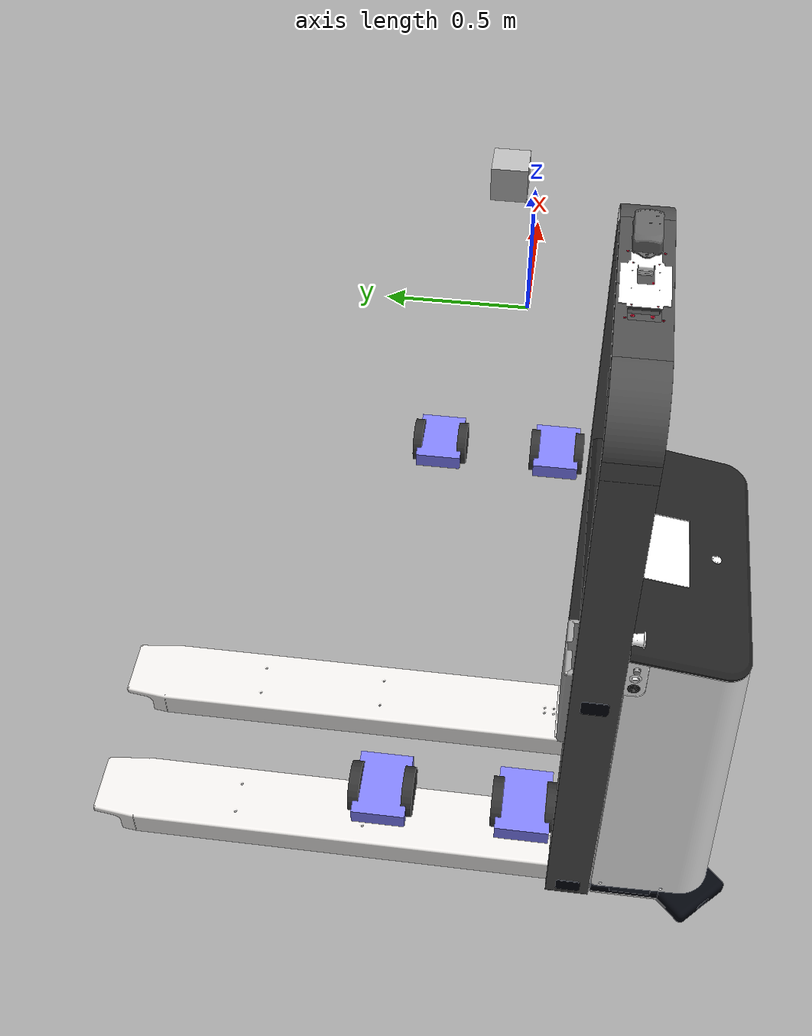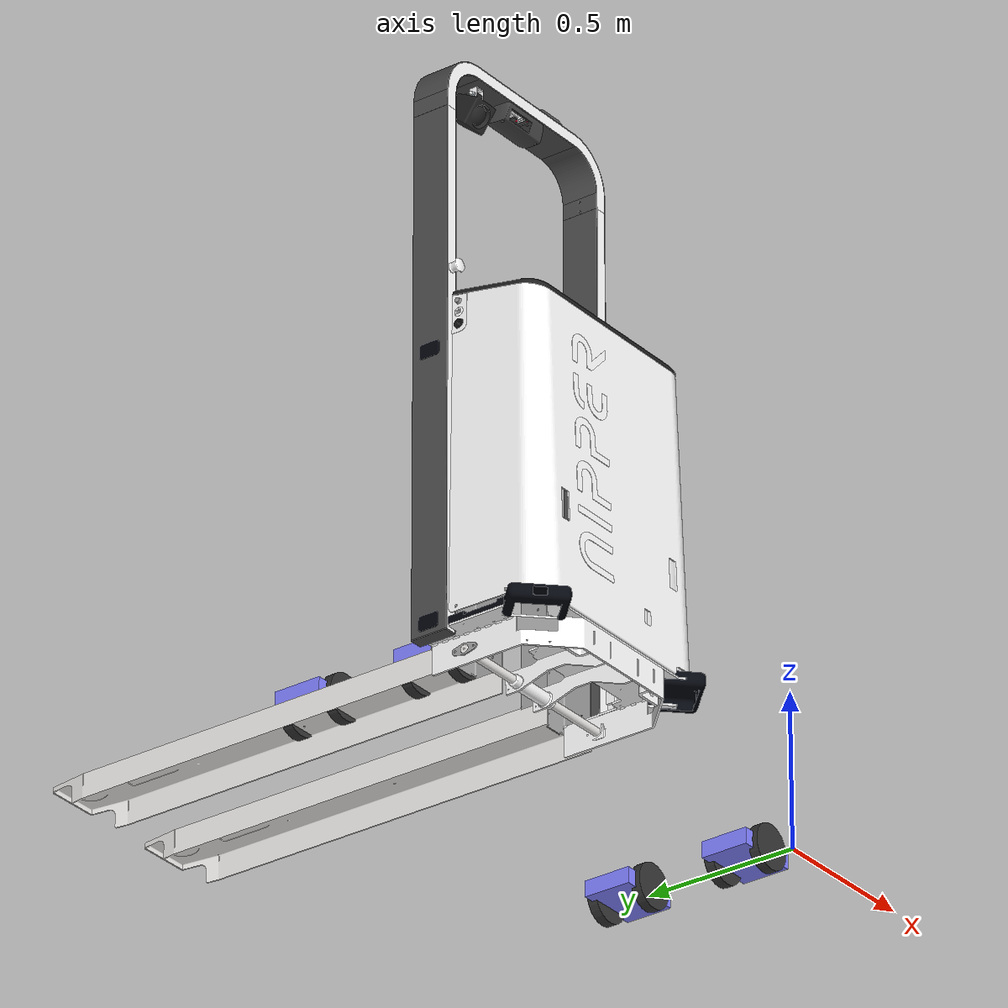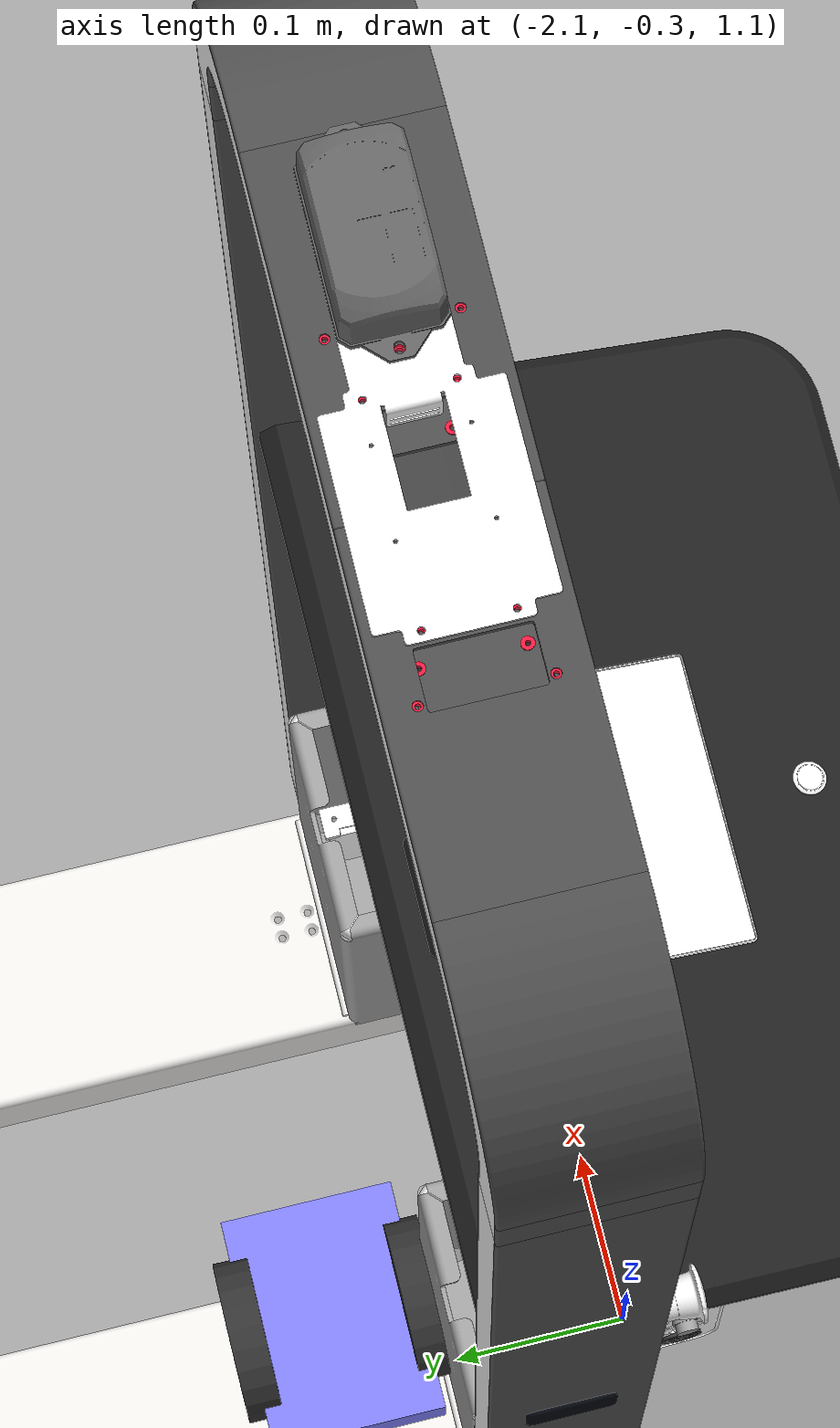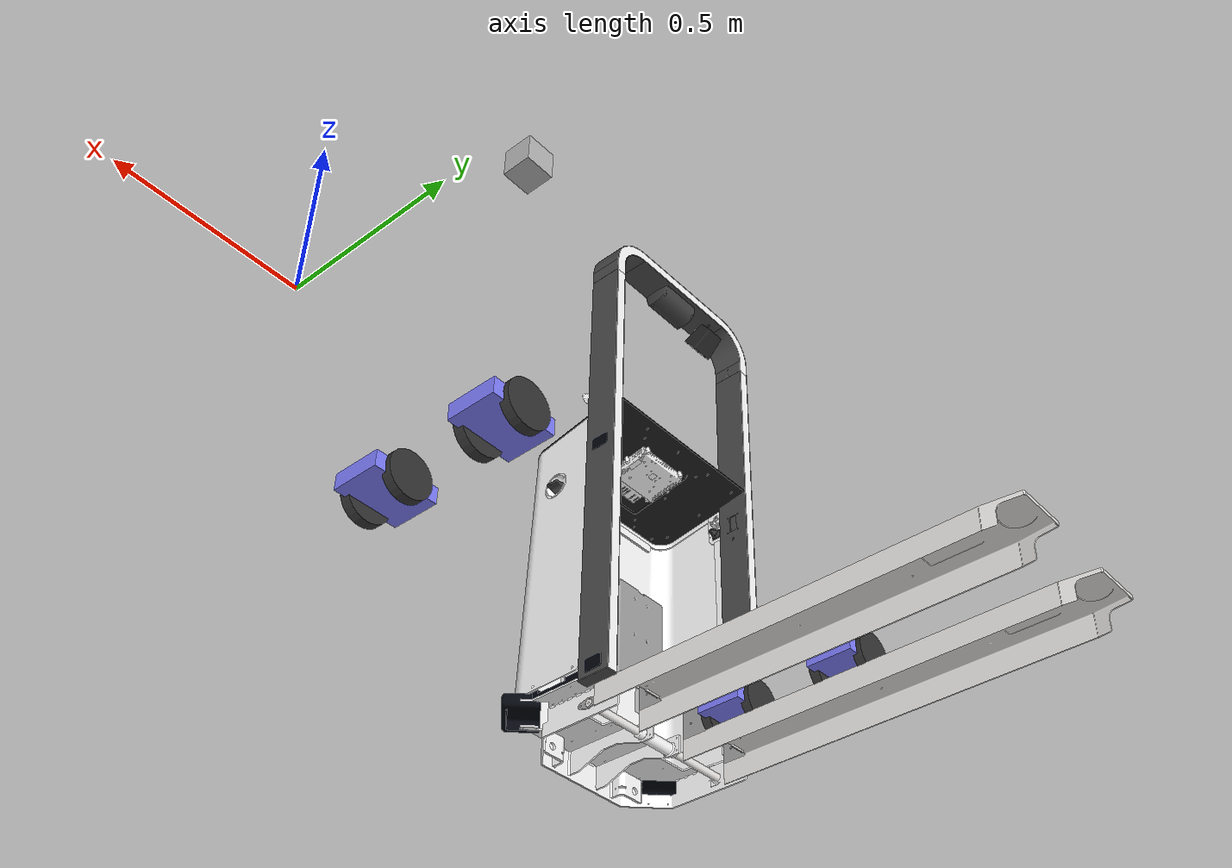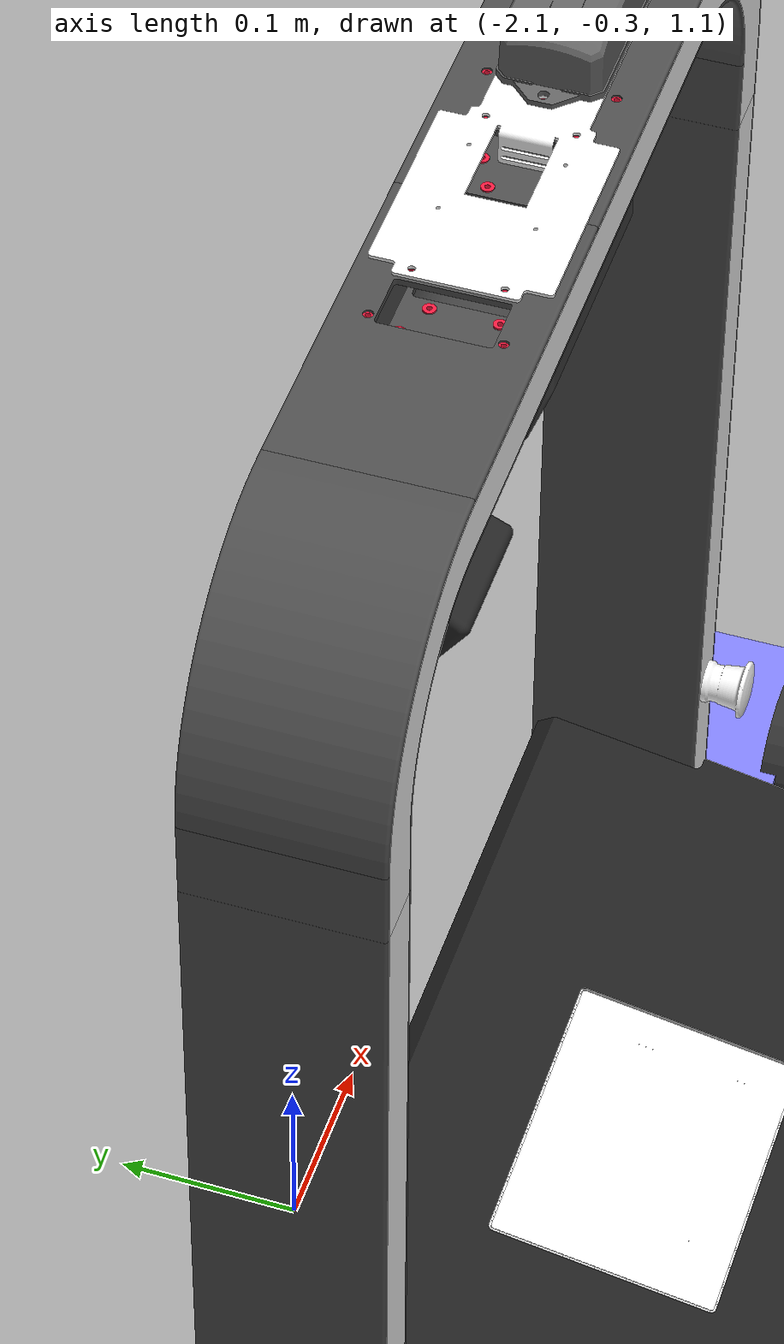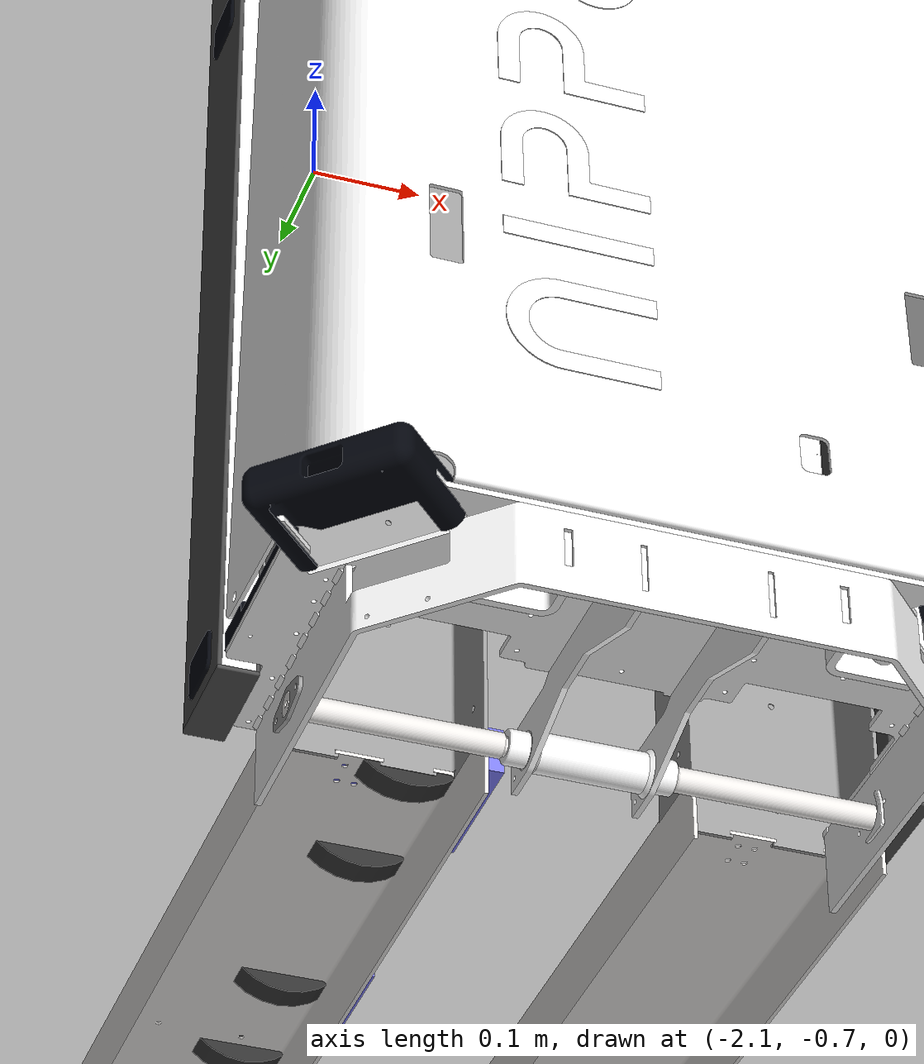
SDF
<?xml version="1.0" ?>
<sdf version="1.8">
    <model name='nipper'>

      <!-- base_link just a nipper model -->

      <link name='base_link'>
      <pose>-1.15 0.05 -0.10 0 -0 0</pose>
      <inertial>
        <inertia>
          <ixx>89.197699999999998</ixx>
          <ixy>-0.20269000000000001</ixy>
          <ixz>0.69273499999999999</ixz>
          <iyy>79.963399999999993</iyy>
          <iyz>8.4993300000000005</iyz>
          <izz>35.5488</izz>
        </inertia>
      </inertial>
      <collision name='5017066_collision'>
        <pose>-0.64529599999999998 -0.692855 0.244675 -4.5809628488036284e-13 -1.5358900000000055 1.5707999999999991</pose>
        <geometry>
          <mesh>
            <scale>1 1 1</scale>
            <uri>file:///home/sarthakshirke/nipper_simulation/src/ros_gz_project_template/ros_gz_example_description/models/nipper/meshes/2117180.stl</uri>
          </mesh>
        </geometry>
      </collision>
      <collision name='5017066_collision_1'>
        <pose>-0.64529599999999998 -0.692855 0.244675 -4.5809628488036284e-13 -1.5358900000000055 1.5707999999999991</pose>
        <geometry>
          <mesh>
            <scale>1 1 1</scale>
            <uri>file:///home/sarthakshirke/nipper_simulation/src/ros_gz_project_template/ros_gz_example_description/models/nipper/meshes/2117180__2.stl</uri>
          </mesh>
        </geometry>
      </collision>
      <collision name='5017066_collision_2'>
        <pose>-0.95300600000000002 -0.40089000000000002 0.73619500000000004 -0.017455799999999997 -0.016995600000000013 -1.55305</pose>
        <geometry>
          <mesh>
            <scale>1 1 1</scale>
            <uri>file:///home/sarthakshirke/nipper_simulation/src/ros_gz_project_template/ros_gz_example_description/models/nipper/meshes/1117620.stl</uri>
          </mesh>
        </geometry>
      </collision>
      <collision name='5017066_collision_3'>
        <pose>-0.64529599999999998 -0.692855 0.244675 -4.5809628488036284e-13 -1.5358900000000055 1.5707999999999991</pose>
        <geometry>
          <mesh>
            <scale>1 1 1</scale>
            <uri>file:///home/sarthakshirke/nipper_simulation/src/ros_gz_project_template/ros_gz_example_description/models/nipper/meshes/2117180__3.stl</uri>
          </mesh>
        </geometry>
      </collision>
      <collision name='5017066_collision_4'>
        <pose>-0.64529599999999998 -0.692855 0.244675 -4.5809628488036284e-13 -1.5358900000000055 1.5707999999999991</pose>
        <geometry>
          <mesh>
            <scale>1 1 1</scale>
            <uri>file:///home/sarthakshirke/nipper_simulation/src/ros_gz_project_template/ros_gz_example_description/models/nipper/meshes/2117180__4.stl</uri>
          </mesh>
        </geometry>
      </collision>
      <collision name='5017066_collision_5'>
        <pose>-0.89912599999999998 -0.394787 0.81249700000000002 -0.017453299999999998 9.1848800000013479e-06 -1.5533399999999999</pose>
        <geometry>
          <mesh>
            <scale>1 1 1</scale>
            <uri>file:///home/sarthakshirke/nipper_simulation/src/ros_gz_project_template/ros_gz_example_description/models/nipper/meshes/3217615.stl</uri>
          </mesh>
        </geometry>
      </collision>
      <collision name='5017066_collision_6'>
        <pose>-0.56348799999999999 -0.70789800000000003 -0.18862400000000001 0 0 0</pose>
        <geometry>
          <mesh>
            <scale>1 1 1</scale>
            <uri>file:///home/sarthakshirke/nipper_simulation/src/ros_gz_project_template/ros_gz_example_description/models/nipper/meshes/3217178.stl</uri>
          </mesh>
        </geometry>
      </collision>
      <collision name='5017066_collision_7'>
        <pose>-0.56348799999999999 -0.68073499999999998 -0.022052499999999999 -3.1415899999999999 7.2469600000003397e-15 -3.1415899999999999</pose>
        <geometry>
          <mesh>
            <scale>1 1 1</scale>
            <uri>file:///home/sarthakshirke/nipper_simulation/src/ros_gz_project_template/ros_gz_example_description/models/nipper/meshes/5914975.stl</uri>
          </mesh>
        </geometry>
      </collision>
      <collision name='5017066_collision_8'>
        <pose>-0.95300600000000002 -0.40089000000000002 0.73619500000000004 -0.017455799999999997 -0.016995600000000013 -1.55305</pose>
        <geometry>
          <mesh>
            <scale>1 1 1</scale>
            <uri>file:///home/sarthakshirke/nipper_simulation/src/ros_gz_project_template/ros_gz_example_description/models/nipper/meshes/1117620__2.stl</uri>
          </mesh>
        </geometry>
      </collision>
      <collision name='5017066_collision_9'>
        <pose>-0.88251100000000005 -0.66118200000000005 -0.21255299999999999 5.9663399999999998e-15 -7.3583199999999992e-15 -0.78539799999999982</pose>
        <geometry>
          <mesh>
            <scale>1 1 1</scale>
            <uri>file:///home/sarthakshirke/nipper_simulation/src/ros_gz_project_template/ros_gz_example_description/models/nipper/meshes/3117013.stl</uri>
          </mesh>
        </geometry>
      </collision>
      <collision name='5017066_collision_10'>
        <pose>-0.64529599999999998 -0.692855 0.244675 -4.5809628488036284e-13 -1.5358900000000055 1.5707999999999991</pose>
        <geometry>
          <mesh>
            <scale>1 1 1</scale>
            <uri>file:///home/sarthakshirke/nipper_simulation/src/ros_gz_project_template/ros_gz_example_description/models/nipper/meshes/2117180__5.stl</uri>
          </mesh>
        </geometry>
      </collision>
      <collision name='5017066_collision_11'>
        <pose>-0.90998800000000002 -0.48823499999999997 -0.17580299999999999 2.0507100000000001e-15 -4.6976300000000021e-15 3.1415899999999999</pose>
        <geometry>
          <mesh>
            <scale>1 1 1</scale>
            <uri>file:///home/sarthakshirke/nipper_simulation/src/ros_gz_project_template/ros_gz_example_description/models/nipper/meshes/3117196.stl</uri>
          </mesh>
        </geometry>
      </collision>
      <collision name='5017066_collision_12'>
        <pose>-0.56348799999999999 -0.70789800000000003 -0.18862400000000001 0 0 0</pose>
        <geometry>
          <mesh>
            <scale>1 1 1</scale>
            <uri>file:///home/sarthakshirke/nipper_simulation/src/ros_gz_project_template/ros_gz_example_description/models/nipper/meshes/3217178__2.stl</uri>
          </mesh>
        </geometry>
      </collision>
      <collision name='5017066_collision_13'>
        <pose>-0.95300600000000002 -0.40089000000000002 0.73619500000000004 -0.017455799999999997 -0.016995600000000013 -1.55305</pose>
        <geometry>
          <mesh>
            <scale>1 1 1</scale>
            <uri>file:///home/sarthakshirke/nipper_simulation/src/ros_gz_project_template/ros_gz_example_description/models/nipper/meshes/1117620__3.stl</uri>
          </mesh>
        </geometry>
      </collision>
      <collision name='5017066_collision_14'>
        <pose>-0.56348799999999999 -0.70789800000000003 -0.18862400000000001 0 0 0</pose>
        <geometry>
          <mesh>
            <scale>1 1 1</scale>
            <uri>file:///home/sarthakshirke/nipper_simulation/src/ros_gz_project_template/ros_gz_example_description/models/nipper/meshes/3217178__3.stl</uri>
          </mesh>
        </geometry>
      </collision>
      <collision name='5017066_collision_15'>
        <pose>-0.24793599999999999 -0.54538799999999998 0.60242099999999998 -0.017453300000000005 6.366435156834882e-16 1.5533399999999999</pose>
        <geometry>
          <mesh>
            <scale>1 1 1</scale>
            <uri>file:///home/sarthakshirke/nipper_simulation/src/ros_gz_project_template/ros_gz_example_description/models/nipper/meshes/3117227.stl</uri>
          </mesh>
        </geometry>
      </collision>
      <collision name='5017066_collision_16'>
        <pose>-0.56348799999999999 -0.70789800000000003 -0.18862400000000001 0 0 0</pose>
        <geometry>
          <mesh>
            <scale>1 1 1</scale>
            <uri>file:///home/sarthakshirke/nipper_simulation/src/ros_gz_project_template/ros_gz_example_description/models/nipper/meshes/3217178__4.stl</uri>
          </mesh>
        </geometry>
      </collision>
      <collision name='5017066_collision_17'>
        <pose>-0.56348799999999999 -0.70789800000000003 -0.18862400000000001 0 0 0</pose>
        <geometry>
          <mesh>
            <scale>1 1 1</scale>
            <uri>file:///home/sarthakshirke/nipper_simulation/src/ros_gz_project_template/ros_gz_example_description/models/nipper/meshes/3217178__5.stl</uri>
          </mesh>
        </geometry>
      </collision>
      <collision name='5017066_collision_18'>
        <pose>-0.64529599999999998 -0.692855 0.244675 -4.5809628488036284e-13 -1.5358900000000055 1.5707999999999991</pose>
        <geometry>
          <mesh>
            <scale>1 1 1</scale>
            <uri>file:///home/sarthakshirke/nipper_simulation/src/ros_gz_project_template/ros_gz_example_description/models/nipper/meshes/2117180__6.stl</uri>
          </mesh>
        </geometry>
      </collision>
      <collision name='5017066_collision_19'>
        <pose>-0.89522699999999999 -0.41772199999999998 0.72642200000000001 1.5533399999999999 9.1848799998087936e-06 -1.5533399999999999</pose>
        <geometry>
          <mesh>
            <scale>1 1 1</scale>
            <uri>file:///home/sarthakshirke/nipper_simulation/src/ros_gz_project_template/ros_gz_example_description/models/nipper/meshes/1117621.stl</uri>
          </mesh>
        </geometry>
      </collision>
      <collision name='5017066_collision_20'>
        <pose>-0.21698799999999999 -0.48823499999999997 -0.17580299999999999 2.0507100000000013e-15 3.20577e-15 -3.1415899999999999</pose>
        <geometry>
          <mesh>
            <scale>1 1 1</scale>
            <uri>file:///home/sarthakshirke/nipper_simulation/src/ros_gz_project_template/ros_gz_example_description/models/nipper/meshes/3117197.stl</uri>
          </mesh>
        </geometry>
      </collision>
      <collision name='5017066_collision_21'>
        <pose>-0.64529599999999998 -0.692855 0.244675 -4.5809628488036284e-13 -1.5358900000000055 1.5707999999999991</pose>
        <geometry>
          <mesh>
            <scale>1 1 1</scale>
            <uri>file:///home/sarthakshirke/nipper_simulation/src/ros_gz_project_template/ros_gz_example_description/models/nipper/meshes/2117180__7.stl</uri>
          </mesh>
        </geometry>
      </collision>
      <collision name='5017066_collision_22'>
        <pose>-0.95300600000000002 -0.40089000000000002 0.73619500000000004 -0.017455799999999997 -0.016995600000000013 -1.55305</pose>
        <geometry>
          <mesh>
            <scale>1 1 1</scale>
            <uri>file:///home/sarthakshirke/nipper_simulation/src/ros_gz_project_template/ros_gz_example_description/models/nipper/meshes/1117620__4.stl</uri>
          </mesh>
        </geometry>
      </collision>
      <collision name='5017066_collision_23'>
        <pose>-0.24411099999999999 -0.66153600000000001 -0.21255299999999999 -7.5797600000000007e-16 1.0149299999999999e-15 0.78539799999999982</pose>
        <geometry>
          <mesh>
            <scale>1 1 1</scale>
            <uri>file:///home/sarthakshirke/nipper_simulation/src/ros_gz_project_template/ros_gz_example_description/models/nipper/meshes/3117163.stl</uri>
          </mesh>
        </geometry>
      </collision>
      <collision name='5017066_collision_24'>
        <pose>-0.56348799999999999 -0.68073499999999998 -0.022052499999999999 -3.1415899999999999 7.2469600000003397e-15 -3.1415899999999999</pose>
        <geometry>
          <mesh>
            <scale>1 1 1</scale>
            <uri>file:///home/sarthakshirke/nipper_simulation/src/ros_gz_project_template/ros_gz_example_description/models/nipper/meshes/5914975__2.stl</uri>
          </mesh>
        </geometry>
      </collision>
      <collision name='5017066_collision_25'>
        <pose>-0.56348799999999999 -0.68073499999999998 -0.022052499999999999 -3.1415899999999999 7.2469600000003397e-15 -3.1415899999999999</pose>
        <geometry>
          <mesh>
            <scale>1 1 1</scale>
            <uri>file:///home/sarthakshirke/nipper_simulation/src/ros_gz_project_template/ros_gz_example_description/models/nipper/meshes/5914975__3.stl</uri>
          </mesh>
        </geometry>
      </collision>
      <collision name='5017066_collision_26'>
        <pose>-0.75273800000000002 0.24715000000000001 -0.495089 3.4087456916415091e-15 -0.0028723100000000012 -1.5708</pose>
        <geometry>
          <mesh>
            <scale>1 1 1</scale>
            <uri>file:///home/sarthakshirke/nipper_simulation/src/ros_gz_project_template/ros_gz_example_description/models/nipper/meshes/3516995_welds.stl</uri>
          </mesh>
        </geometry>
      </collision>
      <collision name='5017066_collision_27'>
        <pose>-0.75273800000000002 0.31506499999999998 -0.23555300000000001 1.4538799999999998e-17 3.5776999999999997e-15 3.1415899999999999</pose>
        <geometry>
          <mesh>
            <scale>1 1 1</scale>
            <uri>file:///home/sarthakshirke/nipper_simulation/src/ros_gz_project_template/ros_gz_example_description/models/nipper/meshes/3716996.stl</uri>
          </mesh>
        </geometry>
      </collision>
      <collision name='5017066_collision_28'>
        <pose>-0.75273800000000002 0.24715000000000001 -0.495089 3.4087456916415091e-15 -0.0028723100000000012 -1.5708</pose>
        <geometry>
          <mesh>
            <scale>1 1 1</scale>
            <uri>file:///home/sarthakshirke/nipper_simulation/src/ros_gz_project_template/ros_gz_example_description/models/nipper/meshes/3516995_welds__2.stl</uri>
          </mesh>
        </geometry>
      </collision>
      <collision name='5017066_collision_29'>
        <pose>-0.75273800000000002 0.24715000000000001 -0.495089 3.4087456916415091e-15 -0.0028723100000000012 -1.5708</pose>
        <geometry>
          <mesh>
            <scale>1 1 1</scale>
            <uri>file:///home/sarthakshirke/nipper_simulation/src/ros_gz_project_template/ros_gz_example_description/models/nipper/meshes/3516995_welds__3.stl</uri>
          </mesh>
        </geometry>
      </collision>
      <collision name='5017066_collision_30'>
        <pose>-0.75273800000000002 0.24715000000000001 -0.495089 3.4087456916415091e-15 -0.0028723100000000012 -1.5708</pose>
        <geometry>
          <mesh>
            <scale>1 1 1</scale>
            <uri>file:///home/sarthakshirke/nipper_simulation/src/ros_gz_project_template/ros_gz_example_description/models/nipper/meshes/3516995_welds__4.stl</uri>
          </mesh>
        </geometry>
      </collision>
      <collision name='5017066_collision_31'>
        <pose>-0.75273800000000002 0.24715000000000001 -0.495089 3.4087456916415091e-15 -0.0028723100000000012 -1.5708</pose>
        <geometry>
          <mesh>
            <scale>1 1 1</scale>
            <uri>file:///home/sarthakshirke/nipper_simulation/src/ros_gz_project_template/ros_gz_example_description/models/nipper/meshes/3516995_welds__5.stl</uri>
          </mesh>
        </geometry>
      </collision>
      <collision name='5017066_collision_32'>
        <pose>-0.75273800000000002 0.24715000000000001 -0.495089 3.4087456916415091e-15 -0.0028723100000000012 -1.5708</pose>
        <geometry>
          <mesh>
            <scale>1 1 1</scale>
            <uri>file:///home/sarthakshirke/nipper_simulation/src/ros_gz_project_template/ros_gz_example_description/models/nipper/meshes/3516995_welds__6.stl</uri>
          </mesh>
        </geometry>
      </collision>
      <collision name='5017066_collision_33'>
        <pose>-0.75273800000000002 -0.29063499999999998 -0.037302500000000002 1.4718600000000004e-17 -2.2860999999999986e-15 -3.1415899999999999</pose>
        <geometry>
          <mesh>
            <scale>1 1 1</scale>
            <uri>file:///home/sarthakshirke/nipper_simulation/src/ros_gz_project_template/ros_gz_example_description/models/nipper/meshes/3716998.stl</uri>
          </mesh>
        </geometry>
      </collision>
      <collision name='5017066_collision_34'>
        <pose>-0.75273800000000002 0.24715000000000001 -0.495089 3.4087456916415091e-15 -0.0028723100000000012 -1.5708</pose>
        <geometry>
          <mesh>
            <scale>1 1 1</scale>
            <uri>file:///home/sarthakshirke/nipper_simulation/src/ros_gz_project_template/ros_gz_example_description/models/nipper/meshes/3516995_welds__7.stl</uri>
          </mesh>
        </geometry>
      </collision>
      <collision name='5017066_collision_35'>
        <pose>-0.75273800000000002 0.24715000000000001 -0.495089 3.4087456916415091e-15 -0.0028723100000000012 -1.5708</pose>
        <geometry>
          <mesh>
            <scale>1 1 1</scale>
            <uri>file:///home/sarthakshirke/nipper_simulation/src/ros_gz_project_template/ros_gz_example_description/models/nipper/meshes/3516995_welds__8.stl</uri>
          </mesh>
        </geometry>
      </collision>
      <collision name='5017066_collision_36'>
        <pose>-0.75273800000000002 0.24715000000000001 -0.495089 3.4087456916415091e-15 -0.0028723100000000012 -1.5708</pose>
        <geometry>
          <mesh>
            <scale>1 1 1</scale>
            <uri>file:///home/sarthakshirke/nipper_simulation/src/ros_gz_project_template/ros_gz_example_description/models/nipper/meshes/3516995_welds__9.stl</uri>
          </mesh>
        </geometry>
      </collision>
      <collision name='5017066_collision_37'>
        <pose>-0.34298800000000002 0.25765100000000002 -0.49383899999999997 6.5950121797445837e-15 -0.0028723100000000012 -1.5708</pose>
        <geometry>
          <mesh>
            <scale>1 1 1</scale>
            <uri>file:///home/sarthakshirke/nipper_simulation/src/ros_gz_project_template/ros_gz_example_description/models/nipper/meshes/3516995_welds__2.stl</uri>
          </mesh>
        </geometry>
      </collision>
      <collision name='5017066_collision_38'>
        <pose>-0.34298800000000002 0.25765100000000002 -0.49383899999999997 6.5950121797445837e-15 -0.0028723100000000012 -1.5708</pose>
        <geometry>
          <mesh>
            <scale>1 1 1</scale>
            <uri>file:///home/sarthakshirke/nipper_simulation/src/ros_gz_project_template/ros_gz_example_description/models/nipper/meshes/3516995_welds__9.stl</uri>
          </mesh>
        </geometry>
      </collision>
      <collision name='5017066_collision_39'>
        <pose>-0.34298800000000002 0.25765100000000002 -0.49383899999999997 6.5950121797445837e-15 -0.0028723100000000012 -1.5708</pose>
        <geometry>
          <mesh>
            <scale>1 1 1</scale>
            <uri>file:///home/sarthakshirke/nipper_simulation/src/ros_gz_project_template/ros_gz_example_description/models/nipper/meshes/3516995_welds__7.stl</uri>
          </mesh>
        </geometry>
      </collision>
      <collision name='5017066_collision_40'>
        <pose>-0.34298800000000002 0.25765100000000002 -0.49383899999999997 6.5950121797445837e-15 -0.0028723100000000012 -1.5708</pose>
        <geometry>
          <mesh>
            <scale>1 1 1</scale>
            <uri>file:///home/sarthakshirke/nipper_simulation/src/ros_gz_project_template/ros_gz_example_description/models/nipper/meshes/3516995_welds__4.stl</uri>
          </mesh>
        </geometry>
      </collision>
      <collision name='5017066_collision_41'>
        <pose>-0.34298800000000002 0.32556600000000002 -0.23430300000000001 9.2984599999999997e-18 6.7640199999999998e-15 3.1415899999999999</pose>
        <geometry>
          <mesh>
            <scale>1 1 1</scale>
            <uri>file:///home/sarthakshirke/nipper_simulation/src/ros_gz_project_template/ros_gz_example_description/models/nipper/meshes/3716996.stl</uri>
          </mesh>
        </geometry>
      </collision>
      <collision name='5017066_collision_42'>
        <pose>-0.34298800000000002 0.25765100000000002 -0.49383899999999997 6.5950121797445837e-15 -0.0028723100000000012 -1.5708</pose>
        <geometry>
          <mesh>
            <scale>1 1 1</scale>
            <uri>file:///home/sarthakshirke/nipper_simulation/src/ros_gz_project_template/ros_gz_example_description/models/nipper/meshes/3516995_welds__6.stl</uri>
          </mesh>
        </geometry>
      </collision>
      <collision name='5017066_collision_43'>
        <pose>-0.34298800000000002 0.25765100000000002 -0.49383899999999997 6.5950121797445837e-15 -0.0028723100000000012 -1.5708</pose>
        <geometry>
          <mesh>
            <scale>1 1 1</scale>
            <uri>file:///home/sarthakshirke/nipper_simulation/src/ros_gz_project_template/ros_gz_example_description/models/nipper/meshes/3516995_welds__5.stl</uri>
          </mesh>
        </geometry>
      </collision>
      <collision name='5017066_collision_44'>
        <pose>-0.34298800000000002 -0.28013399999999999 -0.036052500000000001 9.3906199999999994e-18 9.0151899999999969e-16 -3.1415899999999999</pose>
        <geometry>
          <mesh>
            <scale>1 1 1</scale>
            <uri>file:///home/sarthakshirke/nipper_simulation/src/ros_gz_project_template/ros_gz_example_description/models/nipper/meshes/3716998.stl</uri>
          </mesh>
        </geometry>
      </collision>
      <collision name='5017066_collision_45'>
        <pose>-0.34298800000000002 0.25765100000000002 -0.49383899999999997 6.5950121797445837e-15 -0.0028723100000000012 -1.5708</pose>
        <geometry>
          <mesh>
            <scale>1 1 1</scale>
            <uri>file:///home/sarthakshirke/nipper_simulation/src/ros_gz_project_template/ros_gz_example_description/models/nipper/meshes/3516995_welds.stl</uri>
          </mesh>
        </geometry>
      </collision>
      <collision name='5017066_collision_46'>
        <pose>-0.34298800000000002 0.25765100000000002 -0.49383899999999997 6.5950121797445837e-15 -0.0028723100000000012 -1.5708</pose>
        <geometry>
          <mesh>
            <scale>1 1 1</scale>
            <uri>file:///home/sarthakshirke/nipper_simulation/src/ros_gz_project_template/ros_gz_example_description/models/nipper/meshes/3516995_welds__3.stl</uri>
          </mesh>
        </geometry>
      </collision>
      <collision name='5017066_collision_47'>
        <pose>-0.34298800000000002 0.25765100000000002 -0.49383899999999997 6.5950121797445837e-15 -0.0028723100000000012 -1.5708</pose>
        <geometry>
          <mesh>
            <scale>1 1 1</scale>
            <uri>file:///home/sarthakshirke/nipper_simulation/src/ros_gz_project_template/ros_gz_example_description/models/nipper/meshes/3516995_welds__8.stl</uri>
          </mesh>
        </geometry>
      </collision>
      <collision name='5017066_collision_48'>
        <pose>-0.85148800000000002 -0.314278 0.83496400000000004 1.5708000000000002 -1.3962600000000001 -1.5708</pose>
        <geometry>
          <mesh>
            <scale>1 1 1</scale>
            <uri>file:///home/sarthakshirke/nipper_simulation/src/ros_gz_project_template/ros_gz_example_description/models/nipper/meshes/iso_7049___st_4_2_x_9_5___c___h.stl</uri>
          </mesh>
        </geometry>
      </collision>
      <collision name='5017066_collision_49'>
        <pose>-0.85148800000000002 -0.46027600000000002 0.80922000000000005 1.5708000000000002 -1.3962600000000001 -1.5708</pose>
        <geometry>
          <mesh>
            <scale>1 1 1</scale>
            <uri>file:///home/sarthakshirke/nipper_simulation/src/ros_gz_project_template/ros_gz_example_description/models/nipper/meshes/iso_7049___st_4_2_x_9_5___c___h.stl</uri>
          </mesh>
        </geometry>
      </collision>
      <collision name='5017066_collision_50'>
        <pose>-0.697488 -0.34653099999999998 0.82927700000000004 1.5708000000000002 -1.3962600000000001 -1.5708</pose>
        <geometry>
          <mesh>
            <scale>1 1 1</scale>
            <uri>file:///home/sarthakshirke/nipper_simulation/src/ros_gz_project_template/ros_gz_example_description/models/nipper/meshes/iso_7049___st_4_2_x_9_5___c___h.stl</uri>
          </mesh>
        </geometry>
      </collision>
      <collision name='5017066_collision_51'>
        <pose>-0.50348800000000005 -0.64935900000000002 0.77588000000000001 1.5708000000000002 -1.3962600000000001 -1.5708</pose>
        <geometry>
          <mesh>
            <scale>1 1 1</scale>
            <uri>file:///home/sarthakshirke/nipper_simulation/src/ros_gz_project_template/ros_gz_example_description/models/nipper/meshes/iso_7049___st_4_2_x_9_5___c___h.stl</uri>
          </mesh>
        </geometry>
      </collision>
      <collision name='5017066_collision_52'>
        <pose>-0.53598800000000002 -0.62980800000000003 0.77729599999999999 1.5708000000000002 -1.3962600000000001 -1.5708</pose>
        <geometry>
          <mesh>
            <scale>1 1 1</scale>
            <uri>file:///home/sarthakshirke/nipper_simulation/src/ros_gz_project_template/ros_gz_example_description/models/nipper/meshes/iso_7049___st_4_2_x_9_5___c___h.stl</uri>
          </mesh>
        </geometry>
      </collision>
      <collision name='5017066_collision_53'>
        <pose>-0.42948799999999998 -0.34653099999999998 0.82927700000000004 1.5708000000000002 -1.3962600000000001 -1.5708</pose>
        <geometry>
          <mesh>
            <scale>1 1 1</scale>
            <uri>file:///home/sarthakshirke/nipper_simulation/src/ros_gz_project_template/ros_gz_example_description/models/nipper/meshes/iso_7049___st_4_2_x_9_5___c___h.stl</uri>
          </mesh>
        </geometry>
      </collision>
      <collision name='5017066_collision_54'>
        <pose>-0.56348799999999999 -0.479541 0.80785399999999996 0.17453299999999999 9.4732499999999995e-14 -2.7258400000000002e-13</pose>
        <geometry>
          <mesh>
            <scale>1 1 1</scale>
            <uri>file:///home/sarthakshirke/nipper_simulation/src/ros_gz_project_template/ros_gz_example_description/models/nipper/meshes/3217007.stl</uri>
          </mesh>
        </geometry>
      </collision>
      <collision name='5017066_collision_55'>
        <pose>-0.81648799999999999 -0.64935900000000002 0.77588000000000001 1.5708000000000002 -1.3962600000000001 -1.5708</pose>
        <geometry>
          <mesh>
            <scale>1 1 1</scale>
            <uri>file:///home/sarthakshirke/nipper_simulation/src/ros_gz_project_template/ros_gz_example_description/models/nipper/meshes/iso_7049___st_4_2_x_9_5___c___h.stl</uri>
          </mesh>
        </geometry>
      </collision>
      <collision name='5017066_collision_56'>
        <pose>-0.40548800000000002 -0.64935900000000002 0.77588000000000001 1.5708000000000002 -1.3962600000000001 -1.5708</pose>
        <geometry>
          <mesh>
            <scale>1 1 1</scale>
            <uri>file:///home/sarthakshirke/nipper_simulation/src/ros_gz_project_template/ros_gz_example_description/models/nipper/meshes/iso_7049___st_4_2_x_9_5___c___h.stl</uri>
          </mesh>
        </geometry>
      </collision>
      <collision name='5017066_collision_57'>
        <pose>-0.56348799999999999 -0.45335199999999998 0.82465699999999997 -1.3962600000000001 1.0211199999999999e-13 -2.7143600000000002e-13</pose>
        <geometry>
          <mesh>
            <scale>1 1 1</scale>
            <uri>file:///home/sarthakshirke/nipper_simulation/src/ros_gz_project_template/ros_gz_example_description/models/nipper/meshes/1117246.stl</uri>
          </mesh>
        </geometry>
      </collision>
      <collision name='5017066_collision_58'>
        <pose>-0.27548800000000001 -0.60627399999999998 0.78347699999999998 1.5708000000000002 -1.3962600000000001 -1.5708</pose>
        <geometry>
          <mesh>
            <scale>1 1 1</scale>
            <uri>file:///home/sarthakshirke/nipper_simulation/src/ros_gz_project_template/ros_gz_example_description/models/nipper/meshes/iso_7049___st_4_2_x_9_5___c___h.stl</uri>
          </mesh>
        </geometry>
      </collision>
      <collision name='5017066_collision_59'>
        <pose>-0.27548800000000001 -0.46027600000000002 0.80922000000000005 1.5708000000000002 -1.3962600000000001 -1.5708</pose>
        <geometry>
          <mesh>
            <scale>1 1 1</scale>
            <uri>file:///home/sarthakshirke/nipper_simulation/src/ros_gz_project_template/ros_gz_example_description/models/nipper/meshes/iso_7049___st_4_2_x_9_5___c___h.stl</uri>
          </mesh>
        </geometry>
      </collision>
      <collision name='5017066_collision_60'>
        <pose>-0.56348799999999999 -0.45335199999999998 0.82465699999999997 -1.3962600000000001 1.0211199999999999e-13 -2.7143600000000002e-13</pose>
        <geometry>
          <mesh>
            <scale>1 1 1</scale>
            <uri>file:///home/sarthakshirke/nipper_simulation/src/ros_gz_project_template/ros_gz_example_description/models/nipper/meshes/1117246__2.stl</uri>
          </mesh>
        </geometry>
      </collision>
      <collision name='5017066_collision_61'>
        <pose>-0.697488 -0.48563499999999998 0.80474900000000005 1.5708000000000002 -1.3962600000000001 -1.5708</pose>
        <geometry>
          <mesh>
            <scale>1 1 1</scale>
            <uri>file:///home/sarthakshirke/nipper_simulation/src/ros_gz_project_template/ros_gz_example_description/models/nipper/meshes/iso_7049___st_4_2_x_9_5___c___h.stl</uri>
          </mesh>
        </geometry>
      </collision>
      <collision name='5017066_collision_62'>
        <pose>-0.72148800000000002 -0.314278 0.83496400000000004 1.5708000000000002 -1.3962600000000001 -1.5708</pose>
        <geometry>
          <mesh>
            <scale>1 1 1</scale>
            <uri>file:///home/sarthakshirke/nipper_simulation/src/ros_gz_project_template/ros_gz_example_description/models/nipper/meshes/iso_7049___st_4_2_x_9_5___c___h.stl</uri>
          </mesh>
        </geometry>
      </collision>
      <collision name='5017066_collision_63'>
        <pose>-0.56348799999999999 -0.314278 0.83496400000000004 1.5708000000000002 -1.3962600000000001 -1.5708</pose>
        <geometry>
          <mesh>
            <scale>1 1 1</scale>
            <uri>file:///home/sarthakshirke/nipper_simulation/src/ros_gz_project_template/ros_gz_example_description/models/nipper/meshes/iso_7049___st_4_2_x_9_5___c___h.stl</uri>
          </mesh>
        </geometry>
      </collision>
      <collision name='5017066_collision_64'>
        <pose>-0.42948799999999998 -0.48563499999999998 0.80474900000000005 1.5708000000000002 -1.3962600000000001 -1.5708</pose>
        <geometry>
          <mesh>
            <scale>1 1 1</scale>
            <uri>file:///home/sarthakshirke/nipper_simulation/src/ros_gz_project_template/ros_gz_example_description/models/nipper/meshes/iso_7049___st_4_2_x_9_5___c___h.stl</uri>
          </mesh>
        </geometry>
      </collision>
      <collision name='5017066_collision_65'>
        <pose>-0.56348799999999999 -0.45335199999999998 0.82465699999999997 -1.3962600000000001 1.0211199999999999e-13 -2.7143600000000002e-13</pose>
        <geometry>
          <mesh>
            <scale>1 1 1</scale>
            <uri>file:///home/sarthakshirke/nipper_simulation/src/ros_gz_project_template/ros_gz_example_description/models/nipper/meshes/1117246__3.stl</uri>
          </mesh>
        </geometry>
      </collision>
      <collision name='5017066_collision_66'>
        <pose>-0.42948799999999998 -0.62473900000000004 0.78022100000000005 1.5708000000000002 -1.3962600000000001 -1.5708</pose>
        <geometry>
          <mesh>
            <scale>1 1 1</scale>
            <uri>file:///home/sarthakshirke/nipper_simulation/src/ros_gz_project_template/ros_gz_example_description/models/nipper/meshes/iso_7049___st_4_2_x_9_5___c___h.stl</uri>
          </mesh>
        </geometry>
      </collision>
      <collision name='5017066_collision_67'>
        <pose>-0.85148800000000002 -0.60627399999999998 0.78347699999999998 1.5708000000000002 -1.3962600000000001 -1.5708</pose>
        <geometry>
          <mesh>
            <scale>1 1 1</scale>
            <uri>file:///home/sarthakshirke/nipper_simulation/src/ros_gz_project_template/ros_gz_example_description/models/nipper/meshes/iso_7049___st_4_2_x_9_5___c___h.stl</uri>
          </mesh>
        </geometry>
      </collision>
      <collision name='5017066_collision_68'>
        <pose>-0.56348799999999999 -0.45335199999999998 0.82465699999999997 -1.3962600000000001 1.0211199999999999e-13 -2.7143600000000002e-13</pose>
        <geometry>
          <mesh>
            <scale>1 1 1</scale>
            <uri>file:///home/sarthakshirke/nipper_simulation/src/ros_gz_project_template/ros_gz_example_description/models/nipper/meshes/1117246__4.stl</uri>
          </mesh>
        </geometry>
      </collision>
      <collision name='5017066_collision_69'>
        <pose>-0.697488 -0.62473900000000004 0.78022100000000005 1.5708000000000002 -1.3962600000000001 -1.5708</pose>
        <geometry>
          <mesh>
            <scale>1 1 1</scale>
            <uri>file:///home/sarthakshirke/nipper_simulation/src/ros_gz_project_template/ros_gz_example_description/models/nipper/meshes/iso_7049___st_4_2_x_9_5___c___h.stl</uri>
          </mesh>
        </geometry>
      </collision>
      <collision name='5017066_collision_70'>
        <pose>-0.62348800000000004 -0.64935900000000002 0.77588000000000001 1.5708000000000002 -1.3962600000000001 -1.5708</pose>
        <geometry>
          <mesh>
            <scale>1 1 1</scale>
            <uri>file:///home/sarthakshirke/nipper_simulation/src/ros_gz_project_template/ros_gz_example_description/models/nipper/meshes/iso_7049___st_4_2_x_9_5___c___h.stl</uri>
          </mesh>
        </geometry>
      </collision>
      <collision name='5017066_collision_71'>
        <pose>-0.31048799999999999 -0.64935900000000002 0.77588000000000001 1.5708000000000002 -1.3962600000000001 -1.5708</pose>
        <geometry>
          <mesh>
            <scale>1 1 1</scale>
            <uri>file:///home/sarthakshirke/nipper_simulation/src/ros_gz_project_template/ros_gz_example_description/models/nipper/meshes/iso_7049___st_4_2_x_9_5___c___h.stl</uri>
          </mesh>
        </geometry>
      </collision>
      <collision name='5017066_collision_72'>
        <pose>-0.27548800000000001 -0.314278 0.83496400000000004 1.5708000000000002 -1.3962600000000001 -1.5708</pose>
        <geometry>
          <mesh>
            <scale>1 1 1</scale>
            <uri>file:///home/sarthakshirke/nipper_simulation/src/ros_gz_project_template/ros_gz_example_description/models/nipper/meshes/iso_7049___st_4_2_x_9_5___c___h.stl</uri>
          </mesh>
        </geometry>
      </collision>
      <collision name='5017066_collision_73'>
        <pose>-0.72148800000000002 -0.64935900000000002 0.77588000000000001 1.5708000000000002 -1.3962600000000001 -1.5708</pose>
        <geometry>
          <mesh>
            <scale>1 1 1</scale>
            <uri>file:///home/sarthakshirke/nipper_simulation/src/ros_gz_project_template/ros_gz_example_description/models/nipper/meshes/iso_7049___st_4_2_x_9_5___c___h.stl</uri>
          </mesh>
        </geometry>
      </collision>
      <collision name='5017066_collision_74'>
        <pose>-0.59098799999999996 -0.62980800000000003 0.77729599999999999 1.5708000000000002 -1.3962600000000001 -1.5708</pose>
        <geometry>
          <mesh>
            <scale>1 1 1</scale>
            <uri>file:///home/sarthakshirke/nipper_simulation/src/ros_gz_project_template/ros_gz_example_description/models/nipper/meshes/iso_7049___st_4_2_x_9_5___c___h.stl</uri>
          </mesh>
        </geometry>
      </collision>
      <collision name='5017066_collision_75'>
        <pose>-0.40548800000000002 -0.314278 0.83496400000000004 1.5708000000000002 -1.3962600000000001 -1.5708</pose>
        <geometry>
          <mesh>
            <scale>1 1 1</scale>
            <uri>file:///home/sarthakshirke/nipper_simulation/src/ros_gz_project_template/ros_gz_example_description/models/nipper/meshes/iso_7049___st_4_2_x_9_5___c___h.stl</uri>
          </mesh>
        </geometry>
      </collision>
      <collision name='5017066_collision_76'>
        <pose>-0.38723800000000003 -0.40673500000000001 -0.23955299999999999 -1.5708 -8.2156503822261584e-15 -1.5708</pose>
        <geometry>
          <mesh>
            <scale>1 1 1</scale>
            <uri>file:///home/sarthakshirke/nipper_simulation/src/ros_gz_project_template/ros_gz_example_description/models/nipper/meshes/3213660.stl</uri>
          </mesh>
        </geometry>
      </collision>
      <collision name='5017066_collision_77'>
        <pose>-0.26473799999999997 -0.40673500000000001 -0.23955299999999999 4.6333299999999999e-15 -8.2038400000000036e-15 -1.5708</pose>
        <geometry>
          <mesh>
            <scale>1 1 1</scale>
            <uri>file:///home/sarthakshirke/nipper_simulation/src/ros_gz_project_template/ros_gz_example_description/models/nipper/meshes/3713659.stl</uri>
          </mesh>
        </geometry>
      </collision>
      <collision name='5017066_collision_78'>
        <pose>-0.201988 -0.28023399999999998 -0.20405300000000001 -1.5708 8.5684984735474087e-16 -3.1415899999999999</pose>
        <geometry>
          <mesh>
            <scale>1 1 1</scale>
            <uri>file:///home/sarthakshirke/nipper_simulation/src/ros_gz_project_template/ros_gz_example_description/models/nipper/meshes/5917562.stl</uri>
          </mesh>
        </geometry>
      </collision>
      <collision name='5017066_collision_79'>
        <pose>-0.198988 -0.336034 0.66294699999999995 8.5685000000000001e-16 8.3085000000000047e-19 -1.5708</pose>
        <geometry>
          <mesh>
            <scale>1 1 1</scale>
            <uri>file:///home/sarthakshirke/nipper_simulation/src/ros_gz_project_template/ros_gz_example_description/models/nipper/meshes/3118326.stl</uri>
          </mesh>
        </geometry>
      </collision>
      <collision name='5017066_collision_80'>
        <pose>-0.201988 -0.28023399999999998 -0.20405300000000001 -1.5708 8.5684984735474087e-16 -3.1415899999999999</pose>
        <geometry>
          <mesh>
            <scale>1 1 1</scale>
            <uri>file:///home/sarthakshirke/nipper_simulation/src/ros_gz_project_template/ros_gz_example_description/models/nipper/meshes/5917562__2.stl</uri>
          </mesh>
        </geometry>
      </collision>
      <collision name='5017066_collision_81'>
        <pose>-0.201988 -0.28023399999999998 -0.20405300000000001 -1.5708 8.5684984735474087e-16 -3.1415899999999999</pose>
        <geometry>
          <mesh>
            <scale>1 1 1</scale>
            <uri>file:///home/sarthakshirke/nipper_simulation/src/ros_gz_project_template/ros_gz_example_description/models/nipper/meshes/5917562__3.stl</uri>
          </mesh>
        </geometry>
      </collision>
      <collision name='5017066_collision_82'>
        <pose>-0.201988 -0.28023399999999998 -0.20405300000000001 -1.5708 8.5684984735474087e-16 -3.1415899999999999</pose>
        <geometry>
          <mesh>
            <scale>1 1 1</scale>
            <uri>file:///home/sarthakshirke/nipper_simulation/src/ros_gz_project_template/ros_gz_example_description/models/nipper/meshes/5917562__4.stl</uri>
          </mesh>
        </geometry>
      </collision>
      <collision name='5017066_collision_83'>
        <pose>-0.22273799999999999 -0.35253400000000001 0.90661700000000001 1.5708 4.3407300000000014e-15 4.3407300000000006e-15</pose>
        <geometry>
          <mesh>
            <scale>1 1 1</scale>
            <uri>file:///home/sarthakshirke/nipper_simulation/src/ros_gz_project_template/ros_gz_example_description/models/nipper/meshes/1118327.stl</uri>
          </mesh>
        </geometry>
      </collision>
      <collision name='5017066_collision_84'>
        <pose>-0.201988 -0.28023399999999998 -0.20405300000000001 -1.5708 8.5684984735474087e-16 -3.1415899999999999</pose>
        <geometry>
          <mesh>
            <scale>1 1 1</scale>
            <uri>file:///home/sarthakshirke/nipper_simulation/src/ros_gz_project_template/ros_gz_example_description/models/nipper/meshes/5917562__5.stl</uri>
          </mesh>
        </geometry>
      </collision>
      <collision name='5017066_collision_85'>
        <pose>-0.201988 -0.28023399999999998 -0.20405300000000001 -1.5708 8.5684984735474087e-16 -3.1415899999999999</pose>
        <geometry>
          <mesh>
            <scale>1 1 1</scale>
            <uri>file:///home/sarthakshirke/nipper_simulation/src/ros_gz_project_template/ros_gz_example_description/models/nipper/meshes/5917562__6.stl</uri>
          </mesh>
        </geometry>
      </collision>
      <collision name='5017066_collision_86'>
        <pose>-0.201988 -0.28023399999999998 -0.20405300000000001 -1.5708 8.5684984735474087e-16 -3.1415899999999999</pose>
        <geometry>
          <mesh>
            <scale>1 1 1</scale>
            <uri>file:///home/sarthakshirke/nipper_simulation/src/ros_gz_project_template/ros_gz_example_description/models/nipper/meshes/5917562__7.stl</uri>
          </mesh>
        </geometry>
      </collision>
      <collision name='5017066_collision_87'>
        <pose>-0.201988 -0.28023399999999998 -0.20405300000000001 -1.5708 8.5684984735474087e-16 -3.1415899999999999</pose>
        <geometry>
          <mesh>
            <scale>1 1 1</scale>
            <uri>file:///home/sarthakshirke/nipper_simulation/src/ros_gz_project_template/ros_gz_example_description/models/nipper/meshes/5917562__8.stl</uri>
          </mesh>
        </geometry>
      </collision>
      <collision name='5017066_collision_88'>
        <pose>-0.201988 -0.28023399999999998 -0.20405300000000001 -1.5708 8.5684984735474087e-16 -3.1415899999999999</pose>
        <geometry>
          <mesh>
            <scale>1 1 1</scale>
            <uri>file:///home/sarthakshirke/nipper_simulation/src/ros_gz_project_template/ros_gz_example_description/models/nipper/meshes/5917562__9.stl</uri>
          </mesh>
        </geometry>
      </collision>
      <collision name='5017066_collision_89'>
        <pose>-0.201988 -0.28023399999999998 -0.20405300000000001 -1.5708 8.5684984735474087e-16 -3.1415899999999999</pose>
        <geometry>
          <mesh>
            <scale>1 1 1</scale>
            <uri>file:///home/sarthakshirke/nipper_simulation/src/ros_gz_project_template/ros_gz_example_description/models/nipper/meshes/5917562__10.stl</uri>
          </mesh>
        </geometry>
      </collision>
      <collision name='5017066_collision_90'>
        <pose>-0.201988 -0.28023399999999998 -0.20405300000000001 -1.5708 8.5684984735474087e-16 -3.1415899999999999</pose>
        <geometry>
          <mesh>
            <scale>1 1 1</scale>
            <uri>file:///home/sarthakshirke/nipper_simulation/src/ros_gz_project_template/ros_gz_example_description/models/nipper/meshes/5917562__11.stl</uri>
          </mesh>
        </geometry>
      </collision>
      <collision name='5017066_collision_91'>
        <pose>-0.201988 -0.28023399999999998 -0.20405300000000001 -1.5708 8.5684984735474087e-16 -3.1415899999999999</pose>
        <geometry>
          <mesh>
            <scale>1 1 1</scale>
            <uri>file:///home/sarthakshirke/nipper_simulation/src/ros_gz_project_template/ros_gz_example_description/models/nipper/meshes/5917562__12.stl</uri>
          </mesh>
        </geometry>
      </collision>
      <collision name='5017066_collision_92'>
        <pose>-0.201988 -0.28023399999999998 -0.20405300000000001 -1.5708 8.5684984735474087e-16 -3.1415899999999999</pose>
        <geometry>
          <mesh>
            <scale>1 1 1</scale>
            <uri>file:///home/sarthakshirke/nipper_simulation/src/ros_gz_project_template/ros_gz_example_description/models/nipper/meshes/5917562__13.stl</uri>
          </mesh>
        </geometry>
      </collision>
      <collision name='5017066_collision_93'>
        <pose>-0.201988 -0.28023399999999998 -0.20405300000000001 -1.5708 8.5684984735474087e-16 -3.1415899999999999</pose>
        <geometry>
          <mesh>
            <scale>1 1 1</scale>
            <uri>file:///home/sarthakshirke/nipper_simulation/src/ros_gz_project_template/ros_gz_example_description/models/nipper/meshes/5917562__14.stl</uri>
          </mesh>
        </geometry>
      </collision>
      <collision name='5017066_collision_94'>
        <pose>-0.201988 -0.28023399999999998 -0.20405300000000001 -1.5708 8.5684984735474087e-16 -3.1415899999999999</pose>
        <geometry>
          <mesh>
            <scale>1 1 1</scale>
            <uri>file:///home/sarthakshirke/nipper_simulation/src/ros_gz_project_template/ros_gz_example_description/models/nipper/meshes/5917562__15.stl</uri>
          </mesh>
        </geometry>
      </collision>
      <collision name='5017066_collision_95'>
        <pose>-0.201988 -0.28023399999999998 -0.20405300000000001 -1.5708 8.5684984735474087e-16 -3.1415899999999999</pose>
        <geometry>
          <mesh>
            <scale>1 1 1</scale>
            <uri>file:///home/sarthakshirke/nipper_simulation/src/ros_gz_project_template/ros_gz_example_description/models/nipper/meshes/5917562__16.stl</uri>
          </mesh>
        </geometry>
      </collision>
      <collision name='5017066_collision_96'>
        <pose>-0.201988 -0.28023399999999998 -0.20405300000000001 -1.5708 8.5684984735474087e-16 -3.1415899999999999</pose>
        <geometry>
          <mesh>
            <scale>1 1 1</scale>
            <uri>file:///home/sarthakshirke/nipper_simulation/src/ros_gz_project_template/ros_gz_example_description/models/nipper/meshes/5917562__17.stl</uri>
          </mesh>
        </geometry>
      </collision>
      <collision name='5017066_collision_97'>
        <pose>-0.201988 -0.28023399999999998 -0.20405300000000001 -1.5708 8.5684984735474087e-16 -3.1415899999999999</pose>
        <geometry>
          <mesh>
            <scale>1 1 1</scale>
            <uri>file:///home/sarthakshirke/nipper_simulation/src/ros_gz_project_template/ros_gz_example_description/models/nipper/meshes/5917562__18.stl</uri>
          </mesh>
        </geometry>
      </collision>
      <collision name='5017066_collision_98'>
        <pose>-0.201988 -0.28023399999999998 -0.20405300000000001 -1.5708 8.5684984735474087e-16 -3.1415899999999999</pose>
        <geometry>
          <mesh>
            <scale>1 1 1</scale>
            <uri>file:///home/sarthakshirke/nipper_simulation/src/ros_gz_project_template/ros_gz_example_description/models/nipper/meshes/5917562__19.stl</uri>
          </mesh>
        </geometry>
      </collision>
      <collision name='5017066_collision_99'>
        <pose>-0.201988 -0.28023399999999998 -0.20405300000000001 -1.5708 8.5684984735474087e-16 -3.1415899999999999</pose>
        <geometry>
          <mesh>
            <scale>1 1 1</scale>
            <uri>file:///home/sarthakshirke/nipper_simulation/src/ros_gz_project_template/ros_gz_example_description/models/nipper/meshes/5917562__20.stl</uri>
          </mesh>
        </geometry>
      </collision>
      <collision name='5017066_collision_100'>
        <pose>-0.201988 -0.28023399999999998 -0.20405300000000001 -1.5708 8.5684984735474087e-16 -3.1415899999999999</pose>
        <geometry>
          <mesh>
            <scale>1 1 1</scale>
            <uri>file:///home/sarthakshirke/nipper_simulation/src/ros_gz_project_template/ros_gz_example_description/models/nipper/meshes/5917562__21.stl</uri>
          </mesh>
        </geometry>
      </collision>
      <collision name='5017066_collision_101'>
        <pose>-0.201988 -0.28023399999999998 -0.20405300000000001 -1.5708 8.5684984735474087e-16 -3.1415899999999999</pose>
        <geometry>
          <mesh>
            <scale>1 1 1</scale>
            <uri>file:///home/sarthakshirke/nipper_simulation/src/ros_gz_project_template/ros_gz_example_description/models/nipper/meshes/5917562__22.stl</uri>
          </mesh>
        </geometry>
      </collision>
      <collision name='5017066_collision_102'>
        <pose>-0.201988 -0.28023399999999998 -0.20405300000000001 -1.5708 8.5684984735474087e-16 -3.1415899999999999</pose>
        <geometry>
          <mesh>
            <scale>1 1 1</scale>
            <uri>file:///home/sarthakshirke/nipper_simulation/src/ros_gz_project_template/ros_gz_example_description/models/nipper/meshes/5917562__23.stl</uri>
          </mesh>
        </geometry>
      </collision>
      <collision name='5017066_collision_103'>
        <pose>-0.201988 -0.28023399999999998 -0.20405300000000001 -1.5708 8.5684984735474087e-16 -3.1415899999999999</pose>
        <geometry>
          <mesh>
            <scale>1 1 1</scale>
            <uri>file:///home/sarthakshirke/nipper_simulation/src/ros_gz_project_template/ros_gz_example_description/models/nipper/meshes/5917562__24.stl</uri>
          </mesh>
        </geometry>
      </collision>
      <collision name='5017066_collision_104'>
        <pose>-0.201988 -0.28023399999999998 -0.20405300000000001 -1.5708 8.5684984735474087e-16 -3.1415899999999999</pose>
        <geometry>
          <mesh>
            <scale>1 1 1</scale>
            <uri>file:///home/sarthakshirke/nipper_simulation/src/ros_gz_project_template/ros_gz_example_description/models/nipper/meshes/5917562__25.stl</uri>
          </mesh>
        </geometry>
      </collision>
      <collision name='5017066_collision_105'>
        <pose>-0.201988 -0.28023399999999998 -0.20405300000000001 -1.5708 8.5684984735474087e-16 -3.1415899999999999</pose>
        <geometry>
          <mesh>
            <scale>1 1 1</scale>
            <uri>file:///home/sarthakshirke/nipper_simulation/src/ros_gz_project_template/ros_gz_example_description/models/nipper/meshes/5917562__26.stl</uri>
          </mesh>
        </geometry>
      </collision>
      <collision name='5017066_collision_106'>
        <pose>-0.201988 -0.28023399999999998 -0.20405300000000001 -1.5708 8.5684984735474087e-16 -3.1415899999999999</pose>
        <geometry>
          <mesh>
            <scale>1 1 1</scale>
            <uri>file:///home/sarthakshirke/nipper_simulation/src/ros_gz_project_template/ros_gz_example_description/models/nipper/meshes/5917562__27.stl</uri>
          </mesh>
        </geometry>
      </collision>
      <collision name='5017066_collision_107'>
        <pose>-0.201988 -0.28023399999999998 -0.20405300000000001 -1.5708 8.5684984735474087e-16 -3.1415899999999999</pose>
        <geometry>
          <mesh>
            <scale>1 1 1</scale>
            <uri>file:///home/sarthakshirke/nipper_simulation/src/ros_gz_project_template/ros_gz_example_description/models/nipper/meshes/5917562__28.stl</uri>
          </mesh>
        </geometry>
      </collision>
      <collision name='5017066_collision_108'>
        <pose>-0.201988 -0.28023399999999998 -0.20405300000000001 -1.5708 8.5684984735474087e-16 -3.1415899999999999</pose>
        <geometry>
          <mesh>
            <scale>1 1 1</scale>
            <uri>file:///home/sarthakshirke/nipper_simulation/src/ros_gz_project_template/ros_gz_example_description/models/nipper/meshes/5917562__29.stl</uri>
          </mesh>
        </geometry>
      </collision>
      <collision name='5017066_collision_109'>
        <pose>-0.201988 -0.28023399999999998 -0.20405300000000001 -1.5708 8.5684984735474087e-16 -3.1415899999999999</pose>
        <geometry>
          <mesh>
            <scale>1 1 1</scale>
            <uri>file:///home/sarthakshirke/nipper_simulation/src/ros_gz_project_template/ros_gz_example_description/models/nipper/meshes/5917562__30.stl</uri>
          </mesh>
        </geometry>
      </collision>
      <collision name='5017066_collision_110'>
        <pose>-0.201988 -0.28023399999999998 -0.20405300000000001 -1.5708 8.5684984735474087e-16 -3.1415899999999999</pose>
        <geometry>
          <mesh>
            <scale>1 1 1</scale>
            <uri>file:///home/sarthakshirke/nipper_simulation/src/ros_gz_project_template/ros_gz_example_description/models/nipper/meshes/5917562__31.stl</uri>
          </mesh>
        </geometry>
      </collision>
      <collision name='5017066_collision_111'>
        <pose>-0.201988 -0.28023399999999998 -0.20405300000000001 -1.5708 8.5684984735474087e-16 -3.1415899999999999</pose>
        <geometry>
          <mesh>
            <scale>1 1 1</scale>
            <uri>file:///home/sarthakshirke/nipper_simulation/src/ros_gz_project_template/ros_gz_example_description/models/nipper/meshes/5917562__32.stl</uri>
          </mesh>
        </geometry>
      </collision>
      <collision name='5017066_collision_112'>
        <pose>-0.90423799999999999 -0.35253400000000001 0.90661700000000001 1.5708 4.5856600000000004e-15 4.5856599999999997e-15</pose>
        <geometry>
          <mesh>
            <scale>1 1 1</scale>
            <uri>file:///home/sarthakshirke/nipper_simulation/src/ros_gz_project_template/ros_gz_example_description/models/nipper/meshes/1118327.stl</uri>
          </mesh>
        </geometry>
      </collision>
      <collision name='5017066_collision_113'>
        <pose>-0.56348799999999999 -0.34323399999999998 1.5379499999999999 8.3084999999999999e-19 -2.73597e-16 6.3781200000000006e-11</pose>
        <geometry>
          <mesh>
            <scale>1 1 1</scale>
            <uri>file:///home/sarthakshirke/nipper_simulation/src/ros_gz_project_template/ros_gz_example_description/models/nipper/meshes/3117564.stl</uri>
          </mesh>
        </geometry>
      </collision>
      <collision name='5017066_collision_114'>
        <pose>-0.201988 -0.28023399999999998 -0.20405300000000001 -1.5708 8.5684984735474087e-16 -3.1415899999999999</pose>
        <geometry>
          <mesh>
            <scale>1 1 1</scale>
            <uri>file:///home/sarthakshirke/nipper_simulation/src/ros_gz_project_template/ros_gz_example_description/models/nipper/meshes/5917562__33.stl</uri>
          </mesh>
        </geometry>
      </collision>
      <collision name='5017066_collision_115'>
        <pose>-0.201988 -0.28023399999999998 -0.20405300000000001 -1.5708 8.5684984735474087e-16 -3.1415899999999999</pose>
        <geometry>
          <mesh>
            <scale>1 1 1</scale>
            <uri>file:///home/sarthakshirke/nipper_simulation/src/ros_gz_project_template/ros_gz_example_description/models/nipper/meshes/5917562__34.stl</uri>
          </mesh>
        </geometry>
      </collision>
      <collision name='5017066_collision_116'>
        <pose>-0.201988 -0.28023399999999998 -0.20405300000000001 -1.5708 8.5684984735474087e-16 -3.1415899999999999</pose>
        <geometry>
          <mesh>
            <scale>1 1 1</scale>
            <uri>file:///home/sarthakshirke/nipper_simulation/src/ros_gz_project_template/ros_gz_example_description/models/nipper/meshes/5917562__35.stl</uri>
          </mesh>
        </geometry>
      </collision>
      <collision name='5017066_collision_117'>
        <pose>-0.201988 -0.28023399999999998 -0.20405300000000001 -1.5708 8.5684984735474087e-16 -3.1415899999999999</pose>
        <geometry>
          <mesh>
            <scale>1 1 1</scale>
            <uri>file:///home/sarthakshirke/nipper_simulation/src/ros_gz_project_template/ros_gz_example_description/models/nipper/meshes/5917562__36.stl</uri>
          </mesh>
        </geometry>
      </collision>
      <collision name='5017066_collision_118'>
        <pose>-0.201988 -0.28023399999999998 -0.20405300000000001 -1.5708 8.5684984735474087e-16 -3.1415899999999999</pose>
        <geometry>
          <mesh>
            <scale>1 1 1</scale>
            <uri>file:///home/sarthakshirke/nipper_simulation/src/ros_gz_project_template/ros_gz_example_description/models/nipper/meshes/5917562__37.stl</uri>
          </mesh>
        </geometry>
      </collision>
      <collision name='5017066_collision_119'>
        <pose>-0.201988 -0.28023399999999998 -0.20405300000000001 -1.5708 8.5684984735474087e-16 -3.1415899999999999</pose>
        <geometry>
          <mesh>
            <scale>1 1 1</scale>
            <uri>file:///home/sarthakshirke/nipper_simulation/src/ros_gz_project_template/ros_gz_example_description/models/nipper/meshes/5917562__38.stl</uri>
          </mesh>
        </geometry>
      </collision>
      <collision name='5017066_collision_120'>
        <pose>-0.201988 -0.28023399999999998 -0.20405300000000001 -1.5708 8.5684984735474087e-16 -3.1415899999999999</pose>
        <geometry>
          <mesh>
            <scale>1 1 1</scale>
            <uri>file:///home/sarthakshirke/nipper_simulation/src/ros_gz_project_template/ros_gz_example_description/models/nipper/meshes/5917562__39.stl</uri>
          </mesh>
        </geometry>
      </collision>
      <collision name='5017066_collision_121'>
        <pose>-0.201988 -0.28023399999999998 -0.20405300000000001 -1.5708 8.5684984735474087e-16 -3.1415899999999999</pose>
        <geometry>
          <mesh>
            <scale>1 1 1</scale>
            <uri>file:///home/sarthakshirke/nipper_simulation/src/ros_gz_project_template/ros_gz_example_description/models/nipper/meshes/5917562__40.stl</uri>
          </mesh>
        </geometry>
      </collision>
      <collision name='5017066_collision_122'>
        <pose>-0.201988 -0.28023399999999998 -0.20405300000000001 -1.5708 8.5684984735474087e-16 -3.1415899999999999</pose>
        <geometry>
          <mesh>
            <scale>1 1 1</scale>
            <uri>file:///home/sarthakshirke/nipper_simulation/src/ros_gz_project_template/ros_gz_example_description/models/nipper/meshes/5917562__41.stl</uri>
          </mesh>
        </geometry>
      </collision>
      <collision name='5017066_collision_123'>
        <pose>-0.201988 -0.28023399999999998 -0.20405300000000001 -1.5708 8.5684984735474087e-16 -3.1415899999999999</pose>
        <geometry>
          <mesh>
            <scale>1 1 1</scale>
            <uri>file:///home/sarthakshirke/nipper_simulation/src/ros_gz_project_template/ros_gz_example_description/models/nipper/meshes/5917562__42.stl</uri>
          </mesh>
        </geometry>
      </collision>
      <collision name='5017066_collision_124'>
        <pose>-0.201988 -0.28023399999999998 -0.20405300000000001 -1.5708 8.5684984735474087e-16 -3.1415899999999999</pose>
        <geometry>
          <mesh>
            <scale>1 1 1</scale>
            <uri>file:///home/sarthakshirke/nipper_simulation/src/ros_gz_project_template/ros_gz_example_description/models/nipper/meshes/5917562__43.stl</uri>
          </mesh>
        </geometry>
      </collision>
      <collision name='5017066_collision_125'>
        <pose>-0.201988 -0.28023399999999998 -0.20405300000000001 -1.5708 8.5684984735474087e-16 -3.1415899999999999</pose>
        <geometry>
          <mesh>
            <scale>1 1 1</scale>
            <uri>file:///home/sarthakshirke/nipper_simulation/src/ros_gz_project_template/ros_gz_example_description/models/nipper/meshes/5917562__44.stl</uri>
          </mesh>
        </geometry>
      </collision>
      <collision name='5017066_collision_126'>
        <pose>-0.92798800000000004 -0.33643400000000001 0.66294699999999995 -8.5685000000000011e-16 -1.6616999999999516e-18 1.5708</pose>
        <geometry>
          <mesh>
            <scale>1 1 1</scale>
            <uri>file:///home/sarthakshirke/nipper_simulation/src/ros_gz_project_template/ros_gz_example_description/models/nipper/meshes/3118326.stl</uri>
          </mesh>
        </geometry>
      </collision>
      <collision name='5017066_collision_127'>
        <pose>-0.201988 -0.28023399999999998 -0.20405300000000001 -1.5708 8.5684984735474087e-16 -3.1415899999999999</pose>
        <geometry>
          <mesh>
            <scale>1 1 1</scale>
            <uri>file:///home/sarthakshirke/nipper_simulation/src/ros_gz_project_template/ros_gz_example_description/models/nipper/meshes/5917562__45.stl</uri>
          </mesh>
        </geometry>
      </collision>
      <collision name='5017066_collision_128'>
        <pose>-0.201988 -0.28023399999999998 -0.20405300000000001 -1.5708 8.5684984735474087e-16 -3.1415899999999999</pose>
        <geometry>
          <mesh>
            <scale>1 1 1</scale>
            <uri>file:///home/sarthakshirke/nipper_simulation/src/ros_gz_project_template/ros_gz_example_description/models/nipper/meshes/5917562__46.stl</uri>
          </mesh>
        </geometry>
      </collision>
      <collision name='5017066_collision_129'>
        <pose>-0.201988 -0.28023399999999998 -0.20405300000000001 -1.5708 8.5684984735474087e-16 -3.1415899999999999</pose>
        <geometry>
          <mesh>
            <scale>1 1 1</scale>
            <uri>file:///home/sarthakshirke/nipper_simulation/src/ros_gz_project_template/ros_gz_example_description/models/nipper/meshes/5917562__47.stl</uri>
          </mesh>
        </geometry>
      </collision>
      <collision name='5017066_collision_130'>
        <pose>-0.201988 -0.28023399999999998 -0.20405300000000001 -1.5708 8.5684984735474087e-16 -3.1415899999999999</pose>
        <geometry>
          <mesh>
            <scale>1 1 1</scale>
            <uri>file:///home/sarthakshirke/nipper_simulation/src/ros_gz_project_template/ros_gz_example_description/models/nipper/meshes/5917562__48.stl</uri>
          </mesh>
        </geometry>
      </collision>
      <collision name='5017066_collision_131'>
        <pose>-0.201988 -0.28023399999999998 -0.20405300000000001 -1.5708 8.5684984735474087e-16 -3.1415899999999999</pose>
        <geometry>
          <mesh>
            <scale>1 1 1</scale>
            <uri>file:///home/sarthakshirke/nipper_simulation/src/ros_gz_project_template/ros_gz_example_description/models/nipper/meshes/5917562__49.stl</uri>
          </mesh>
        </geometry>
      </collision>
      <collision name='5017066_collision_132'>
        <pose>-0.92798800000000004 -0.33643400000000001 -0.163053 -8.5685000000000011e-16 -1.6616999999999516e-18 1.5708</pose>
        <geometry>
          <mesh>
            <scale>1 1 1</scale>
            <uri>file:///home/sarthakshirke/nipper_simulation/src/ros_gz_project_template/ros_gz_example_description/models/nipper/meshes/3118326.stl</uri>
          </mesh>
        </geometry>
      </collision>
      <collision name='5017066_collision_133'>
        <pose>-0.201988 -0.28023399999999998 -0.20405300000000001 -1.5708 8.5684984735474087e-16 -3.1415899999999999</pose>
        <geometry>
          <mesh>
            <scale>1 1 1</scale>
            <uri>file:///home/sarthakshirke/nipper_simulation/src/ros_gz_project_template/ros_gz_example_description/models/nipper/meshes/5917562__50.stl</uri>
          </mesh>
        </geometry>
      </collision>
      <collision name='5017066_collision_134'>
        <pose>-0.201988 -0.28023399999999998 -0.20405300000000001 -1.5708 8.5684984735474087e-16 -3.1415899999999999</pose>
        <geometry>
          <mesh>
            <scale>1 1 1</scale>
            <uri>file:///home/sarthakshirke/nipper_simulation/src/ros_gz_project_template/ros_gz_example_description/models/nipper/meshes/5917562__51.stl</uri>
          </mesh>
        </geometry>
      </collision>
      <collision name='5017066_collision_135'>
        <pose>-0.198988 -0.336034 -0.163053 8.5685000000000001e-16 8.3085000000000047e-19 -1.5708</pose>
        <geometry>
          <mesh>
            <scale>1 1 1</scale>
            <uri>file:///home/sarthakshirke/nipper_simulation/src/ros_gz_project_template/ros_gz_example_description/models/nipper/meshes/3118326.stl</uri>
          </mesh>
        </geometry>
      </collision>
      <collision name='5017066_collision_136'>
        <pose>-0.201988 -0.28023399999999998 -0.20405300000000001 -1.5708 8.5684984735474087e-16 -3.1415899999999999</pose>
        <geometry>
          <mesh>
            <scale>1 1 1</scale>
            <uri>file:///home/sarthakshirke/nipper_simulation/src/ros_gz_project_template/ros_gz_example_description/models/nipper/meshes/5917562__52.stl</uri>
          </mesh>
        </geometry>
      </collision>
      <collision name='5017066_collision_137'>
        <pose>-0.201988 -0.28023399999999998 -0.20405300000000001 -1.5708 8.5684984735474087e-16 -3.1415899999999999</pose>
        <geometry>
          <mesh>
            <scale>1 1 1</scale>
            <uri>file:///home/sarthakshirke/nipper_simulation/src/ros_gz_project_template/ros_gz_example_description/models/nipper/meshes/5917562__53.stl</uri>
          </mesh>
        </geometry>
      </collision>
      <collision name='5017066_collision_138'>
        <pose>-0.201988 -0.28023399999999998 -0.20405300000000001 -1.5708 8.5684984735474087e-16 -3.1415899999999999</pose>
        <geometry>
          <mesh>
            <scale>1 1 1</scale>
            <uri>file:///home/sarthakshirke/nipper_simulation/src/ros_gz_project_template/ros_gz_example_description/models/nipper/meshes/5917562__54.stl</uri>
          </mesh>
        </geometry>
      </collision>
      <collision name='5017066_collision_139'>
        <pose>-0.201988 -0.28023399999999998 -0.20405300000000001 -1.5708 8.5684984735474087e-16 -3.1415899999999999</pose>
        <geometry>
          <mesh>
            <scale>1 1 1</scale>
            <uri>file:///home/sarthakshirke/nipper_simulation/src/ros_gz_project_template/ros_gz_example_description/models/nipper/meshes/5917562__55.stl</uri>
          </mesh>
        </geometry>
      </collision>
      <collision name='5017066_collision_140'>
        <pose>-0.201988 -0.28023399999999998 -0.20405300000000001 -1.5708 8.5684984735474087e-16 -3.1415899999999999</pose>
        <geometry>
          <mesh>
            <scale>1 1 1</scale>
            <uri>file:///home/sarthakshirke/nipper_simulation/src/ros_gz_project_template/ros_gz_example_description/models/nipper/meshes/5917562__56.stl</uri>
          </mesh>
        </geometry>
      </collision>
      <collision name='5017066_collision_141'>
        <pose>-0.201988 -0.28023399999999998 -0.20405300000000001 -1.5708 8.5684984735474087e-16 -3.1415899999999999</pose>
        <geometry>
          <mesh>
            <scale>1 1 1</scale>
            <uri>file:///home/sarthakshirke/nipper_simulation/src/ros_gz_project_template/ros_gz_example_description/models/nipper/meshes/5917562__57.stl</uri>
          </mesh>
        </geometry>
      </collision>
      <collision name='5017066_collision_142'>
        <pose>-0.201988 -0.28023399999999998 -0.20405300000000001 -1.5708 8.5684984735474087e-16 -3.1415899999999999</pose>
        <geometry>
          <mesh>
            <scale>1 1 1</scale>
            <uri>file:///home/sarthakshirke/nipper_simulation/src/ros_gz_project_template/ros_gz_example_description/models/nipper/meshes/5917562__58.stl</uri>
          </mesh>
        </geometry>
      </collision>
      <collision name='5017066_collision_143'>
        <pose>-0.201988 -0.28023399999999998 -0.20405300000000001 -1.5708 8.5684984735474087e-16 -3.1415899999999999</pose>
        <geometry>
          <mesh>
            <scale>1 1 1</scale>
            <uri>file:///home/sarthakshirke/nipper_simulation/src/ros_gz_project_template/ros_gz_example_description/models/nipper/meshes/5917562__59.stl</uri>
          </mesh>
        </geometry>
      </collision>
      <collision name='5017066_collision_144'>
        <pose>-0.201988 -0.28023399999999998 -0.20405300000000001 -1.5708 8.5684984735474087e-16 -3.1415899999999999</pose>
        <geometry>
          <mesh>
            <scale>1 1 1</scale>
            <uri>file:///home/sarthakshirke/nipper_simulation/src/ros_gz_project_template/ros_gz_example_description/models/nipper/meshes/5917562__60.stl</uri>
          </mesh>
        </geometry>
      </collision>
      <collision name='5017066_collision_145'>
        <pose>-0.201988 -0.28023399999999998 -0.20405300000000001 -1.5708 8.5684984735474087e-16 -3.1415899999999999</pose>
        <geometry>
          <mesh>
            <scale>1 1 1</scale>
            <uri>file:///home/sarthakshirke/nipper_simulation/src/ros_gz_project_template/ros_gz_example_description/models/nipper/meshes/5917562__61.stl</uri>
          </mesh>
        </geometry>
      </collision>
      <collision name='5017066_collision_146'>
        <pose>-0.201988 -0.28023399999999998 -0.20405300000000001 -1.5708 8.5684984735474087e-16 -3.1415899999999999</pose>
        <geometry>
          <mesh>
            <scale>1 1 1</scale>
            <uri>file:///home/sarthakshirke/nipper_simulation/src/ros_gz_project_template/ros_gz_example_description/models/nipper/meshes/5917562__62.stl</uri>
          </mesh>
        </geometry>
      </collision>
      <collision name='5017066_collision_147'>
        <pose>-0.201988 -0.28023399999999998 -0.20405300000000001 -1.5708 8.5684984735474087e-16 -3.1415899999999999</pose>
        <geometry>
          <mesh>
            <scale>1 1 1</scale>
            <uri>file:///home/sarthakshirke/nipper_simulation/src/ros_gz_project_template/ros_gz_example_description/models/nipper/meshes/5917562__63.stl</uri>
          </mesh>
        </geometry>
      </collision>
      <collision name='5017066_collision_148'>
        <pose>-0.201988 -0.28023399999999998 -0.20405300000000001 -1.5708 8.5684984735474087e-16 -3.1415899999999999</pose>
        <geometry>
          <mesh>
            <scale>1 1 1</scale>
            <uri>file:///home/sarthakshirke/nipper_simulation/src/ros_gz_project_template/ros_gz_example_description/models/nipper/meshes/5917562__64.stl</uri>
          </mesh>
        </geometry>
      </collision>
      <collision name='5017066_collision_149'>
        <pose>-0.201988 -0.28023399999999998 -0.20405300000000001 -1.5708 8.5684984735474087e-16 -3.1415899999999999</pose>
        <geometry>
          <mesh>
            <scale>1 1 1</scale>
            <uri>file:///home/sarthakshirke/nipper_simulation/src/ros_gz_project_template/ros_gz_example_description/models/nipper/meshes/5917562__65.stl</uri>
          </mesh>
        </geometry>
      </collision>
      <collision name='5017066_collision_150'>
        <pose>-0.201988 -0.28023399999999998 -0.20405300000000001 -1.5708 8.5684984735474087e-16 -3.1415899999999999</pose>
        <geometry>
          <mesh>
            <scale>1 1 1</scale>
            <uri>file:///home/sarthakshirke/nipper_simulation/src/ros_gz_project_template/ros_gz_example_description/models/nipper/meshes/5917562__66.stl</uri>
          </mesh>
        </geometry>
      </collision>
      <collision name='5017066_collision_151'>
        <pose>-0.201988 -0.28023399999999998 -0.20405300000000001 -1.5708 8.5684984735474087e-16 -3.1415899999999999</pose>
        <geometry>
          <mesh>
            <scale>1 1 1</scale>
            <uri>file:///home/sarthakshirke/nipper_simulation/src/ros_gz_project_template/ros_gz_example_description/models/nipper/meshes/5917562__67.stl</uri>
          </mesh>
        </geometry>
      </collision>
      <collision name='5017066_collision_152'>
        <pose>-0.201988 -0.28023399999999998 -0.20405300000000001 -1.5708 8.5684984735474087e-16 -3.1415899999999999</pose>
        <geometry>
          <mesh>
            <scale>1 1 1</scale>
            <uri>file:///home/sarthakshirke/nipper_simulation/src/ros_gz_project_template/ros_gz_example_description/models/nipper/meshes/5917562__68.stl</uri>
          </mesh>
        </geometry>
      </collision>
      <collision name='5017066_collision_153'>
        <pose>-0.201988 -0.28023399999999998 -0.20405300000000001 -1.5708 8.5684984735474087e-16 -3.1415899999999999</pose>
        <geometry>
          <mesh>
            <scale>1 1 1</scale>
            <uri>file:///home/sarthakshirke/nipper_simulation/src/ros_gz_project_template/ros_gz_example_description/models/nipper/meshes/5917562__69.stl</uri>
          </mesh>
        </geometry>
      </collision>
      <collision name='5017066_collision_154'>
        <pose>-0.201988 -0.28023399999999998 -0.20405300000000001 -1.5708 8.5684984735474087e-16 -3.1415899999999999</pose>
        <geometry>
          <mesh>
            <scale>1 1 1</scale>
            <uri>file:///home/sarthakshirke/nipper_simulation/src/ros_gz_project_template/ros_gz_example_description/models/nipper/meshes/5917562__70.stl</uri>
          </mesh>
        </geometry>
      </collision>
      <collision name='5017066_collision_155'>
        <pose>-0.201988 -0.28023399999999998 -0.20405300000000001 -1.5708 8.5684984735474087e-16 -3.1415899999999999</pose>
        <geometry>
          <mesh>
            <scale>1 1 1</scale>
            <uri>file:///home/sarthakshirke/nipper_simulation/src/ros_gz_project_template/ros_gz_example_description/models/nipper/meshes/5917562__71.stl</uri>
          </mesh>
        </geometry>
      </collision>
      <collision name='5017066_collision_156'>
        <pose>-0.201988 -0.28023399999999998 -0.20405300000000001 -1.5708 8.5684984735474087e-16 -3.1415899999999999</pose>
        <geometry>
          <mesh>
            <scale>1 1 1</scale>
            <uri>file:///home/sarthakshirke/nipper_simulation/src/ros_gz_project_template/ros_gz_example_description/models/nipper/meshes/5917562__72.stl</uri>
          </mesh>
        </geometry>
      </collision>
      <collision name='5017066_collision_157'>
        <pose>-0.201988 -0.28023399999999998 -0.20405300000000001 -1.5708 8.5684984735474087e-16 -3.1415899999999999</pose>
        <geometry>
          <mesh>
            <scale>1 1 1</scale>
            <uri>file:///home/sarthakshirke/nipper_simulation/src/ros_gz_project_template/ros_gz_example_description/models/nipper/meshes/5917562__73.stl</uri>
          </mesh>
        </geometry>
      </collision>
      <collision name='5017066_collision_158'>
        <pose>-0.383988 -0.33623399999999998 1.60595 -1.5708 -1.0966800000000015e-15 5.4913799999999997e-15</pose>
        <geometry>
          <mesh>
            <scale>1 1 1</scale>
            <uri>file:///home/sarthakshirke/nipper_simulation/src/ros_gz_project_template/ros_gz_example_description/models/nipper/meshes/118496.stl</uri>
          </mesh>
        </geometry>
      </collision>
      <collision name='5017066_collision_159'>
        <pose>-0.201988 -0.28023399999999998 -0.20405300000000001 -1.5708 8.5684984735474087e-16 -3.1415899999999999</pose>
        <geometry>
          <mesh>
            <scale>1 1 1</scale>
            <uri>file:///home/sarthakshirke/nipper_simulation/src/ros_gz_project_template/ros_gz_example_description/models/nipper/meshes/5917562__74.stl</uri>
          </mesh>
        </geometry>
      </collision>
      <collision name='5017066_collision_160'>
        <pose>-0.201988 -0.28023399999999998 -0.20405300000000001 -1.5708 8.5684984735474087e-16 -3.1415899999999999</pose>
        <geometry>
          <mesh>
            <scale>1 1 1</scale>
            <uri>file:///home/sarthakshirke/nipper_simulation/src/ros_gz_project_template/ros_gz_example_description/models/nipper/meshes/5917562__75.stl</uri>
          </mesh>
        </geometry>
      </collision>
      <collision name='5017066_collision_161'>
        <pose>-0.201988 -0.28023399999999998 -0.20405300000000001 -1.5708 8.5684984735474087e-16 -3.1415899999999999</pose>
        <geometry>
          <mesh>
            <scale>1 1 1</scale>
            <uri>file:///home/sarthakshirke/nipper_simulation/src/ros_gz_project_template/ros_gz_example_description/models/nipper/meshes/5917562__76.stl</uri>
          </mesh>
        </geometry>
      </collision>
      <collision name='5017066_collision_162'>
        <pose>-0.201988 -0.28023399999999998 -0.20405300000000001 -1.5708 8.5684984735474087e-16 -3.1415899999999999</pose>
        <geometry>
          <mesh>
            <scale>1 1 1</scale>
            <uri>file:///home/sarthakshirke/nipper_simulation/src/ros_gz_project_template/ros_gz_example_description/models/nipper/meshes/5917562__77.stl</uri>
          </mesh>
        </geometry>
      </collision>
      <collision name='5017066_collision_163'>
        <pose>-0.56348799999999999 -0.33623399999999998 1.60395 0 0 0</pose>
        <geometry>
          <mesh>
            <scale>1 1 1</scale>
            <uri>file:///home/sarthakshirke/nipper_simulation/src/ros_gz_project_template/ros_gz_example_description/models/nipper/meshes/3718322.stl</uri>
          </mesh>
        </geometry>
      </collision>
      <collision name='5017066_collision_164'>
        <pose>-0.201988 -0.28023399999999998 -0.20405300000000001 -1.5708 8.5684984735474087e-16 -3.1415899999999999</pose>
        <geometry>
          <mesh>
            <scale>1 1 1</scale>
            <uri>file:///home/sarthakshirke/nipper_simulation/src/ros_gz_project_template/ros_gz_example_description/models/nipper/meshes/5917562__78.stl</uri>
          </mesh>
        </geometry>
      </collision>
      <collision name='5017066_collision_165'>
        <pose>-0.201988 -0.28023399999999998 -0.20405300000000001 -1.5708 8.5684984735474087e-16 -3.1415899999999999</pose>
        <geometry>
          <mesh>
            <scale>1 1 1</scale>
            <uri>file:///home/sarthakshirke/nipper_simulation/src/ros_gz_project_template/ros_gz_example_description/models/nipper/meshes/5917562__79.stl</uri>
          </mesh>
        </geometry>
      </collision>
      <collision name='5017066_collision_166'>
        <pose>-0.91217899999999996 -0.418018 0.79572900000000002 -0.017453300000000001 0.00015229299999999982 -1.55335</pose>
        <geometry>
          <mesh>
            <scale>1 1 1</scale>
            <uri>file:///home/sarthakshirke/nipper_simulation/src/ros_gz_project_template/ros_gz_example_description/models/nipper/meshes/117729.stl</uri>
          </mesh>
        </geometry>
      </collision>
      <collision name='5017066_collision_167'>
        <pose>-0.73973800000000001 -0.40673500000000001 -0.23955299999999999 -1.5708 -3.3306690738754696e-15 1.5708</pose>
        <geometry>
          <mesh>
            <scale>1 1 1</scale>
            <uri>file:///home/sarthakshirke/nipper_simulation/src/ros_gz_project_template/ros_gz_example_description/models/nipper/meshes/3213660.stl</uri>
          </mesh>
        </geometry>
      </collision>
      <collision name='5017066_collision_168'>
        <pose>-0.86223799999999995 -0.40673500000000001 -0.23955299999999999 -1.8729200000000001e-15 -3.3400000000000014e-15 1.5708</pose>
        <geometry>
          <mesh>
            <scale>1 1 1</scale>
            <uri>file:///home/sarthakshirke/nipper_simulation/src/ros_gz_project_template/ros_gz_example_description/models/nipper/meshes/3713659.stl</uri>
          </mesh>
        </geometry>
      </collision>
      <collision name='5017066_collision_169'>
        <pose>-0.31711499999999998 -0.54418 0.601213 1.5533399999999999 -1.7208456881689926e-15 1.5533399999999999</pose>
        <geometry>
          <mesh>
            <scale>1 1 1</scale>
            <uri>file:///home/sarthakshirke/nipper_simulation/src/ros_gz_project_template/ros_gz_example_description/models/nipper/meshes/1111368.stl</uri>
          </mesh>
        </geometry>
      </collision>
      <collision name='5017066_collision_170'>
        <pose>-0.56348799999999999 -0.59458299999999997 0.80787799999999999 0.17453299999999999 1.4430199999999999e-13 -5.4911800000000004e-13</pose>
        <geometry>
          <mesh>
            <scale>1 1 1</scale>
            <uri>file:///home/sarthakshirke/nipper_simulation/src/ros_gz_project_template/ros_gz_example_description/models/nipper/meshes/117739.stl</uri>
          </mesh>
        </geometry>
      </collision>
      <collision name='5017066_collision_171'>
        <pose>-0.84923800000000005 -0.40673500000000001 -0.23955299999999999 1.123463588665461e-15 -0.10596600000000003 -1.5708000000000002</pose>
        <geometry>
          <mesh>
            <scale>1 1 1</scale>
            <uri>file:///home/sarthakshirke/nipper_simulation/src/ros_gz_project_template/ros_gz_example_description/models/nipper/meshes/3716937.stl</uri>
          </mesh>
        </geometry>
      </collision>
      <collision name='5017066_collision_172'>
        <pose>-0.56348799999999999 -0.47273500000000002 -0.29855300000000001 0 0 0</pose>
        <geometry>
          <mesh>
            <scale>1 1 1</scale>
            <uri>file:///home/sarthakshirke/nipper_simulation/src/ros_gz_project_template/ros_gz_example_description/models/nipper/meshes/3516942_welds.stl</uri>
          </mesh>
        </geometry>
      </collision>
      <collision name='5017066_collision_173'>
        <pose>-0.56348799999999999 -0.47273500000000002 -0.29855300000000001 0 0 0</pose>
        <geometry>
          <mesh>
            <scale>1 1 1</scale>
            <uri>file:///home/sarthakshirke/nipper_simulation/src/ros_gz_project_template/ros_gz_example_description/models/nipper/meshes/3516942_welds__2.stl</uri>
          </mesh>
        </geometry>
      </collision>
      <collision name='5017066_collision_174'>
        <pose>-0.56348799999999999 -0.47273500000000002 -0.29855300000000001 0 0 0</pose>
        <geometry>
          <mesh>
            <scale>1 1 1</scale>
            <uri>file:///home/sarthakshirke/nipper_simulation/src/ros_gz_project_template/ros_gz_example_description/models/nipper/meshes/3516942_welds__3.stl</uri>
          </mesh>
        </geometry>
      </collision>
      <collision name='5017066_collision_175'>
        <pose>-0.56348799999999999 -0.47273500000000002 -0.29855300000000001 0 0 0</pose>
        <geometry>
          <mesh>
            <scale>1 1 1</scale>
            <uri>file:///home/sarthakshirke/nipper_simulation/src/ros_gz_project_template/ros_gz_example_description/models/nipper/meshes/3516942_welds__4.stl</uri>
          </mesh>
        </geometry>
      </collision>
      <collision name='5017066_collision_176'>
        <pose>-0.56348799999999999 -0.47273500000000002 -0.29855300000000001 0 0 0</pose>
        <geometry>
          <mesh>
            <scale>1 1 1</scale>
            <uri>file:///home/sarthakshirke/nipper_simulation/src/ros_gz_project_template/ros_gz_example_description/models/nipper/meshes/3516942_welds__5.stl</uri>
          </mesh>
        </geometry>
      </collision>
      <collision name='5017066_collision_177'>
        <pose>-0.73978699999999997 -0.65473499999999996 -0.23355300000000001 0 0 0</pose>
        <geometry>
          <mesh>
            <scale>1 1 1</scale>
            <uri>file:///home/sarthakshirke/nipper_simulation/src/ros_gz_project_template/ros_gz_example_description/models/nipper/meshes/3716938.stl</uri>
          </mesh>
        </geometry>
      </collision>
      <collision name='5017066_collision_178'>
        <pose>-0.85823799999999995 -0.59276899999999999 -0.194053 -1.570796326794897 1.5707963267948966 0</pose>
        <geometry>
          <mesh>
            <scale>1 1 1</scale>
            <uri>file:///home/sarthakshirke/nipper_simulation/src/ros_gz_project_template/ros_gz_example_description/models/nipper/meshes/3716935.stl</uri>
          </mesh>
        </geometry>
      </collision>
      <collision name='5017066_collision_179'>
        <pose>-0.56348799999999999 -0.47273500000000002 -0.29855300000000001 0 0 0</pose>
        <geometry>
          <mesh>
            <scale>1 1 1</scale>
            <uri>file:///home/sarthakshirke/nipper_simulation/src/ros_gz_project_template/ros_gz_example_description/models/nipper/meshes/3516942_welds__6.stl</uri>
          </mesh>
        </geometry>
      </collision>
      <collision name='5017066_collision_180'>
        <pose>-0.56348799999999999 -0.47273500000000002 -0.29855300000000001 0 0 0</pose>
        <geometry>
          <mesh>
            <scale>1 1 1</scale>
            <uri>file:///home/sarthakshirke/nipper_simulation/src/ros_gz_project_template/ros_gz_example_description/models/nipper/meshes/3516942_welds__7.stl</uri>
          </mesh>
        </geometry>
      </collision>
      <collision name='5017066_collision_181'>
        <pose>-0.56348799999999999 -0.47273500000000002 -0.29855300000000001 0 0 0</pose>
        <geometry>
          <mesh>
            <scale>1 1 1</scale>
            <uri>file:///home/sarthakshirke/nipper_simulation/src/ros_gz_project_template/ros_gz_example_description/models/nipper/meshes/3516942_welds__8.stl</uri>
          </mesh>
        </geometry>
      </collision>
      <collision name='5017066_collision_182'>
        <pose>-0.50573800000000002 -0.702735 -0.194053 3.9442900000000001e-31 -2.8244922171547094e-45 1.5708</pose>
        <geometry>
          <mesh>
            <scale>1 1 1</scale>
            <uri>file:///home/sarthakshirke/nipper_simulation/src/ros_gz_project_template/ros_gz_example_description/models/nipper/meshes/3716939.stl</uri>
          </mesh>
        </geometry>
      </collision>
      <collision name='5017066_collision_183'>
        <pose>-0.56348799999999999 -0.47273500000000002 -0.29855300000000001 0 0 0</pose>
        <geometry>
          <mesh>
            <scale>1 1 1</scale>
            <uri>file:///home/sarthakshirke/nipper_simulation/src/ros_gz_project_template/ros_gz_example_description/models/nipper/meshes/3516942_welds__9.stl</uri>
          </mesh>
        </geometry>
      </collision>
      <collision name='5017066_collision_184'>
        <pose>-0.56348799999999999 -0.47273500000000002 -0.29855300000000001 0 0 0</pose>
        <geometry>
          <mesh>
            <scale>1 1 1</scale>
            <uri>file:///home/sarthakshirke/nipper_simulation/src/ros_gz_project_template/ros_gz_example_description/models/nipper/meshes/3516942_welds__10.stl</uri>
          </mesh>
        </geometry>
      </collision>
      <collision name='5017066_collision_185'>
        <pose>-0.56348799999999999 -0.47273500000000002 -0.29855300000000001 0 0 0</pose>
        <geometry>
          <mesh>
            <scale>1 1 1</scale>
            <uri>file:///home/sarthakshirke/nipper_simulation/src/ros_gz_project_template/ros_gz_example_description/models/nipper/meshes/3516942_welds__11.stl</uri>
          </mesh>
        </geometry>
      </collision>
      <collision name='5017066_collision_186'>
        <pose>-0.91998800000000003 -0.47273500000000002 -0.188053 1.5708 -3.1918900000000015e-15 1.3868100000000001e-15</pose>
        <geometry>
          <mesh>
            <scale>1 1 1</scale>
            <uri>file:///home/sarthakshirke/nipper_simulation/src/ros_gz_project_template/ros_gz_example_description/models/nipper/meshes/3716941.stl</uri>
          </mesh>
        </geometry>
      </collision>
      <collision name='5017066_collision_187'>
        <pose>-0.56348799999999999 -0.47273500000000002 -0.29855300000000001 0 0 0</pose>
        <geometry>
          <mesh>
            <scale>1 1 1</scale>
            <uri>file:///home/sarthakshirke/nipper_simulation/src/ros_gz_project_template/ros_gz_example_description/models/nipper/meshes/3516942_welds__12.stl</uri>
          </mesh>
        </geometry>
      </collision>
      <collision name='5017066_collision_188'>
        <pose>-0.27473799999999998 -0.40673500000000001 -0.23955299999999999 3.5936878767870332e-15 -0.10596600000000003 -1.5708</pose>
        <geometry>
          <mesh>
            <scale>1 1 1</scale>
            <uri>file:///home/sarthakshirke/nipper_simulation/src/ros_gz_project_template/ros_gz_example_description/models/nipper/meshes/3716937.stl</uri>
          </mesh>
        </geometry>
      </collision>
      <collision name='5017066_collision_189'>
        <pose>-0.56348799999999999 -0.47273500000000002 -0.29855300000000001 0 0 0</pose>
        <geometry>
          <mesh>
            <scale>1 1 1</scale>
            <uri>file:///home/sarthakshirke/nipper_simulation/src/ros_gz_project_template/ros_gz_example_description/models/nipper/meshes/3516942_welds__13.stl</uri>
          </mesh>
        </geometry>
      </collision>
      <collision name='5017066_collision_190'>
        <pose>-0.56348799999999999 -0.47273500000000002 -0.29855300000000001 0 0 0</pose>
        <geometry>
          <mesh>
            <scale>1 1 1</scale>
            <uri>file:///home/sarthakshirke/nipper_simulation/src/ros_gz_project_template/ros_gz_example_description/models/nipper/meshes/3516942_welds__14.stl</uri>
          </mesh>
        </geometry>
      </collision>
      <collision name='5017066_collision_191'>
        <pose>-0.56348799999999999 -0.47273500000000002 -0.29855300000000001 0 0 0</pose>
        <geometry>
          <mesh>
            <scale>1 1 1</scale>
            <uri>file:///home/sarthakshirke/nipper_simulation/src/ros_gz_project_template/ros_gz_example_description/models/nipper/meshes/3516942_welds__15.stl</uri>
          </mesh>
        </geometry>
      </collision>
      <collision name='5017066_collision_192'>
        <pose>-0.56348799999999999 -0.47273500000000002 -0.29855300000000001 0 0 0</pose>
        <geometry>
          <mesh>
            <scale>1 1 1</scale>
            <uri>file:///home/sarthakshirke/nipper_simulation/src/ros_gz_project_template/ros_gz_example_description/models/nipper/meshes/3516942_welds__16.stl</uri>
          </mesh>
        </geometry>
      </collision>
      <collision name='5017066_collision_193'>
        <pose>-0.56348799999999999 -0.47273500000000002 -0.29855300000000001 0 0 0</pose>
        <geometry>
          <mesh>
            <scale>1 1 1</scale>
            <uri>file:///home/sarthakshirke/nipper_simulation/src/ros_gz_project_template/ros_gz_example_description/models/nipper/meshes/3516942_welds__17.stl</uri>
          </mesh>
        </geometry>
      </collision>
      <collision name='5017066_collision_194'>
        <pose>-0.56348799999999999 -0.47273500000000002 -0.29855300000000001 0 0 0</pose>
        <geometry>
          <mesh>
            <scale>1 1 1</scale>
            <uri>file:///home/sarthakshirke/nipper_simulation/src/ros_gz_project_template/ros_gz_example_description/models/nipper/meshes/3516942_welds__18.stl</uri>
          </mesh>
        </geometry>
      </collision>
      <collision name='5017066_collision_195'>
        <pose>-0.56348799999999999 -0.47273500000000002 -0.29855300000000001 0 0 0</pose>
        <geometry>
          <mesh>
            <scale>1 1 1</scale>
            <uri>file:///home/sarthakshirke/nipper_simulation/src/ros_gz_project_template/ros_gz_example_description/models/nipper/meshes/3516942_welds__19.stl</uri>
          </mesh>
        </geometry>
      </collision>
      <collision name='5017066_collision_196'>
        <pose>-0.62723799999999996 -0.702735 -0.194053 3.9443000000000035e-31 1.8743600000000018e-30 1.5708</pose>
        <geometry>
          <mesh>
            <scale>1 1 1</scale>
            <uri>file:///home/sarthakshirke/nipper_simulation/src/ros_gz_project_template/ros_gz_example_description/models/nipper/meshes/3716939.stl</uri>
          </mesh>
        </geometry>
      </collision>
      <collision name='5017066_collision_197'>
        <pose>-0.56348799999999999 -0.47273500000000002 -0.29855300000000001 0 0 0</pose>
        <geometry>
          <mesh>
            <scale>1 1 1</scale>
            <uri>file:///home/sarthakshirke/nipper_simulation/src/ros_gz_project_template/ros_gz_example_description/models/nipper/meshes/3516942_welds__20.stl</uri>
          </mesh>
        </geometry>
      </collision>
      <collision name='5017066_collision_198'>
        <pose>-0.38718900000000001 -0.65473499999999996 -0.23355300000000001 0 0 0</pose>
        <geometry>
          <mesh>
            <scale>1 1 1</scale>
            <uri>file:///home/sarthakshirke/nipper_simulation/src/ros_gz_project_template/ros_gz_example_description/models/nipper/meshes/3716994.stl</uri>
          </mesh>
        </geometry>
      </collision>
      <collision name='5017066_collision_199'>
        <pose>-0.56348799999999999 -0.47273500000000002 -0.29855300000000001 0 0 0</pose>
        <geometry>
          <mesh>
            <scale>1 1 1</scale>
            <uri>file:///home/sarthakshirke/nipper_simulation/src/ros_gz_project_template/ros_gz_example_description/models/nipper/meshes/3516942_welds__21.stl</uri>
          </mesh>
        </geometry>
      </collision>
      <collision name='5017066_collision_200'>
        <pose>-0.56348799999999999 -0.47273500000000002 -0.29855300000000001 0 0 0</pose>
        <geometry>
          <mesh>
            <scale>1 1 1</scale>
            <uri>file:///home/sarthakshirke/nipper_simulation/src/ros_gz_project_template/ros_gz_example_description/models/nipper/meshes/3516942_welds__22.stl</uri>
          </mesh>
        </geometry>
      </collision>
      <collision name='5017066_collision_201'>
        <pose>-0.56348799999999999 -0.47273500000000002 -0.29855300000000001 0 0 0</pose>
        <geometry>
          <mesh>
            <scale>1 1 1</scale>
            <uri>file:///home/sarthakshirke/nipper_simulation/src/ros_gz_project_template/ros_gz_example_description/models/nipper/meshes/3516942_welds__23.stl</uri>
          </mesh>
        </geometry>
      </collision>
      <collision name='5017066_collision_202'>
        <pose>-0.56348799999999999 -0.47273500000000002 -0.29855300000000001 0 0 0</pose>
        <geometry>
          <mesh>
            <scale>1 1 1</scale>
            <uri>file:///home/sarthakshirke/nipper_simulation/src/ros_gz_project_template/ros_gz_example_description/models/nipper/meshes/3516942_welds__24.stl</uri>
          </mesh>
        </geometry>
      </collision>
      <collision name='5017066_collision_203'>
        <pose>-0.56348799999999999 -0.47273500000000002 -0.29855300000000001 0 0 0</pose>
        <geometry>
          <mesh>
            <scale>1 1 1</scale>
            <uri>file:///home/sarthakshirke/nipper_simulation/src/ros_gz_project_template/ros_gz_example_description/models/nipper/meshes/3516942_welds__25.stl</uri>
          </mesh>
        </geometry>
      </collision>
      <collision name='5017066_collision_204'>
        <pose>-0.56348799999999999 -0.47273500000000002 -0.29855300000000001 0 0 0</pose>
        <geometry>
          <mesh>
            <scale>1 1 1</scale>
            <uri>file:///home/sarthakshirke/nipper_simulation/src/ros_gz_project_template/ros_gz_example_description/models/nipper/meshes/3516942_welds__26.stl</uri>
          </mesh>
        </geometry>
      </collision>
      <collision name='5017066_collision_205'>
        <pose>-0.56348799999999999 -0.47273500000000002 -0.29855300000000001 0 0 0</pose>
        <geometry>
          <mesh>
            <scale>1 1 1</scale>
            <uri>file:///home/sarthakshirke/nipper_simulation/src/ros_gz_project_template/ros_gz_example_description/models/nipper/meshes/3516942_welds__27.stl</uri>
          </mesh>
        </geometry>
      </collision>
      <collision name='5017066_collision_206'>
        <pose>-0.56348799999999999 -0.47273500000000002 -0.29855300000000001 0 0 0</pose>
        <geometry>
          <mesh>
            <scale>1 1 1</scale>
            <uri>file:///home/sarthakshirke/nipper_simulation/src/ros_gz_project_template/ros_gz_example_description/models/nipper/meshes/3516942_welds__28.stl</uri>
          </mesh>
        </geometry>
      </collision>
      <collision name='5017066_collision_207'>
        <pose>-0.56348799999999999 -0.47273500000000002 -0.29855300000000001 0 0 0</pose>
        <geometry>
          <mesh>
            <scale>1 1 1</scale>
            <uri>file:///home/sarthakshirke/nipper_simulation/src/ros_gz_project_template/ros_gz_example_description/models/nipper/meshes/3516942_welds__29.stl</uri>
          </mesh>
        </geometry>
      </collision>
      <collision name='5017066_collision_208'>
        <pose>-0.56348799999999999 -0.47273500000000002 -0.29855300000000001 0 0 0</pose>
        <geometry>
          <mesh>
            <scale>1 1 1</scale>
            <uri>file:///home/sarthakshirke/nipper_simulation/src/ros_gz_project_template/ros_gz_example_description/models/nipper/meshes/3516942_welds__30.stl</uri>
          </mesh>
        </geometry>
      </collision>
      <collision name='5017066_collision_209'>
        <pose>-0.56348799999999999 -0.47273500000000002 -0.29855300000000001 0 0 0</pose>
        <geometry>
          <mesh>
            <scale>1 1 1</scale>
            <uri>file:///home/sarthakshirke/nipper_simulation/src/ros_gz_project_template/ros_gz_example_description/models/nipper/meshes/3516942_welds__31.stl</uri>
          </mesh>
        </geometry>
      </collision>
      <collision name='5017066_collision_210'>
        <pose>-0.56348799999999999 -0.47273500000000002 -0.29855300000000001 0 0 0</pose>
        <geometry>
          <mesh>
            <scale>1 1 1</scale>
            <uri>file:///home/sarthakshirke/nipper_simulation/src/ros_gz_project_template/ros_gz_example_description/models/nipper/meshes/3516942_welds__32.stl</uri>
          </mesh>
        </geometry>
      </collision>
      <collision name='5017066_collision_211'>
        <pose>-0.56348799999999999 -0.47273500000000002 -0.29855300000000001 0 0 0</pose>
        <geometry>
          <mesh>
            <scale>1 1 1</scale>
            <uri>file:///home/sarthakshirke/nipper_simulation/src/ros_gz_project_template/ros_gz_example_description/models/nipper/meshes/3516942_welds__33.stl</uri>
          </mesh>
        </geometry>
      </collision>
      <collision name='5017066_collision_212'>
        <pose>-0.56348799999999999 -0.47273500000000002 -0.29855300000000001 0 0 0</pose>
        <geometry>
          <mesh>
            <scale>1 1 1</scale>
            <uri>file:///home/sarthakshirke/nipper_simulation/src/ros_gz_project_template/ros_gz_example_description/models/nipper/meshes/3516942_welds__34.stl</uri>
          </mesh>
        </geometry>
      </collision>
      <collision name='5017066_collision_213'>
        <pose>-0.56348799999999999 -0.47273500000000002 -0.29855300000000001 0 0 0</pose>
        <geometry>
          <mesh>
            <scale>1 1 1</scale>
            <uri>file:///home/sarthakshirke/nipper_simulation/src/ros_gz_project_template/ros_gz_example_description/models/nipper/meshes/3516942_welds__35.stl</uri>
          </mesh>
        </geometry>
      </collision>
      <collision name='5017066_collision_214'>
        <pose>-0.56348799999999999 -0.47273500000000002 -0.29855300000000001 0 0 0</pose>
        <geometry>
          <mesh>
            <scale>1 1 1</scale>
            <uri>file:///home/sarthakshirke/nipper_simulation/src/ros_gz_project_template/ros_gz_example_description/models/nipper/meshes/3516942_welds__36.stl</uri>
          </mesh>
        </geometry>
      </collision>
      <collision name='5017066_collision_215'>
        <pose>-0.56348799999999999 -0.47273500000000002 -0.29855300000000001 0 0 0</pose>
        <geometry>
          <mesh>
            <scale>1 1 1</scale>
            <uri>file:///home/sarthakshirke/nipper_simulation/src/ros_gz_project_template/ros_gz_example_description/models/nipper/meshes/3516942_welds__37.stl</uri>
          </mesh>
        </geometry>
      </collision>
      <collision name='5017066_collision_216'>
        <pose>-0.64723799999999998 -0.40673500000000001 -0.23955299999999999 -1.6868499999999998e-15 2.5310900000000026e-16 1.5708</pose>
        <geometry>
          <mesh>
            <scale>1 1 1</scale>
            <uri>file:///home/sarthakshirke/nipper_simulation/src/ros_gz_project_template/ros_gz_example_description/models/nipper/meshes/3216934.stl</uri>
          </mesh>
        </geometry>
      </collision>
      <collision name='5017066_collision_217'>
        <pose>-0.56348799999999999 -0.47273500000000002 -0.29855300000000001 0 0 0</pose>
        <geometry>
          <mesh>
            <scale>1 1 1</scale>
            <uri>file:///home/sarthakshirke/nipper_simulation/src/ros_gz_project_template/ros_gz_example_description/models/nipper/meshes/3516942_welds__38.stl</uri>
          </mesh>
        </geometry>
      </collision>
      <collision name='5017066_collision_218'>
        <pose>-0.75963800000000004 -0.356234 1.5399499999999999 3.1415899999999999 4.7260500000002654e-15 -3.1415899999999999</pose>
        <geometry>
          <mesh>
            <scale>1 1 1</scale>
            <uri>file:///home/sarthakshirke/nipper_simulation/src/ros_gz_project_template/ros_gz_example_description/models/nipper/meshes/din_985___m8.stl</uri>
          </mesh>
        </geometry>
      </collision>
      <collision name='5017066_collision_219'>
        <pose>-0.74348800000000004 -0.37049300000000002 1.4714 2.5307300000000001 -5.4880000512479046e-15 -3.1415899999999999</pose>
        <geometry>
          <mesh>
            <scale>1 1 1</scale>
            <uri>file:///home/sarthakshirke/nipper_simulation/src/ros_gz_project_template/ros_gz_example_description/models/nipper/meshes/1114735.stl</uri>
          </mesh>
        </geometry>
      </collision>
      <collision name='5017066_collision_220'>
        <pose>-0.72733800000000004 -0.356234 1.5399499999999999 3.1415899999999999 4.7260500000002654e-15 -3.1415899999999999</pose>
        <geometry>
          <mesh>
            <scale>1 1 1</scale>
            <uri>file:///home/sarthakshirke/nipper_simulation/src/ros_gz_project_template/ros_gz_example_description/models/nipper/meshes/din_933___m8__x_45.stl</uri>
          </mesh>
        </geometry>
      </collision>
      <collision name='5017066_collision_221'>
        <pose>-0.72893799999999997 -0.356234 1.5399499999999999 2.3868399999999999e-16 -4.7260500000000003e-15 4.4438700000000002e-15</pose>
        <geometry>
          <mesh>
            <scale>1 1 1</scale>
            <uri>file:///home/sarthakshirke/nipper_simulation/src/ros_gz_project_template/ros_gz_example_description/models/nipper/meshes/din_125___a_8_4.stl</uri>
          </mesh>
        </geometry>
      </collision>
      <collision name='5017066_collision_222'>
        <pose>-0.74348800000000004 -0.356234 1.5606500000000001 3.1415899999999999 4.7260500000002654e-15 -3.1415899999999999</pose>
        <geometry>
          <mesh>
            <scale>1 1 1</scale>
            <uri>file:///home/sarthakshirke/nipper_simulation/src/ros_gz_project_template/ros_gz_example_description/models/nipper/meshes/1114736.stl</uri>
          </mesh>
        </geometry>
      </collision>
      <collision name='5017066_collision_223'>
        <pose>-0.75803799999999999 -0.356234 1.5399499999999999 3.1415899999999999 4.7260500000002654e-15 -3.1415899999999999</pose>
        <geometry>
          <mesh>
            <scale>1 1 1</scale>
            <uri>file:///home/sarthakshirke/nipper_simulation/src/ros_gz_project_template/ros_gz_example_description/models/nipper/meshes/din_125___a_8_4.stl</uri>
          </mesh>
        </geometry>
      </collision>
      <visual name='5017066_visual'>
        <pose>-0.64529599999999998 -0.692855 0.244675 -4.5809628488036284e-13 -1.5358900000000055 1.5707999999999991</pose>
        <geometry>
          <mesh>
            <scale>1 1 1</scale>
            <uri>file:///home/sarthakshirke/nipper_simulation/src/ros_gz_project_template/ros_gz_example_description/models/nipper/meshes/2117180.stl</uri>
          </mesh>
        </geometry>
        <material>
          <diffuse>1 1 1 1</diffuse>
          <ambient>1 1 1 1</ambient>
        </material>
      </visual>
      <visual name='5017066_visual_1'>
        <pose>-0.64529599999999998 -0.692855 0.244675 -4.5809628488036284e-13 -1.5358900000000055 1.5707999999999991</pose>
        <geometry>
          <mesh>
            <scale>1 1 1</scale>
            <uri>file:///home/sarthakshirke/nipper_simulation/src/ros_gz_project_template/ros_gz_example_description/models/nipper/meshes/2117180__2.stl</uri>
          </mesh>
        </geometry>
        <material>
          <diffuse>1 1 1 1</diffuse>
          <ambient>1 1 1 1</ambient>
        </material>
      </visual>
      <visual name='5017066_visual_2'>
        <pose>-0.95300600000000002 -0.40089000000000002 0.73619500000000004 -0.017455799999999997 -0.016995600000000013 -1.55305</pose>
        <geometry>
          <mesh>
            <scale>1 1 1</scale>
            <uri>file:///home/sarthakshirke/nipper_simulation/src/ros_gz_project_template/ros_gz_example_description/models/nipper/meshes/1117620.stl</uri>
          </mesh>
        </geometry>
        <material>
          <diffuse>1 1 1 1</diffuse>
          <ambient>1 1 1 1</ambient>
        </material>
      </visual>
      <visual name='5017066_visual_3'>
        <pose>-0.64529599999999998 -0.692855 0.244675 -4.5809628488036284e-13 -1.5358900000000055 1.5707999999999991</pose>
        <geometry>
          <mesh>
            <scale>1 1 1</scale>
            <uri>file:///home/sarthakshirke/nipper_simulation/src/ros_gz_project_template/ros_gz_example_description/models/nipper/meshes/2117180__3.stl</uri>
          </mesh>
        </geometry>
        <material>
          <diffuse>1 1 1 1</diffuse>
          <ambient>1 1 1 1</ambient>
        </material>
      </visual>
      <visual name='5017066_visual_4'>
        <pose>-0.64529599999999998 -0.692855 0.244675 -4.5809628488036284e-13 -1.5358900000000055 1.5707999999999991</pose>
        <geometry>
          <mesh>
            <scale>1 1 1</scale>
            <uri>file:///home/sarthakshirke/nipper_simulation/src/ros_gz_project_template/ros_gz_example_description/models/nipper/meshes/2117180__4.stl</uri>
          </mesh>
        </geometry>
        <material>
          <diffuse>1 1 1 1</diffuse>
          <ambient>1 1 1 1</ambient>
        </material>
      </visual>
      <visual name='5017066_visual_5'>
        <pose>-0.89912599999999998 -0.394787 0.81249700000000002 -0.017453299999999998 9.1848800000013479e-06 -1.5533399999999999</pose>
        <geometry>
          <mesh>
            <scale>1 1 1</scale>
            <uri>file:///home/sarthakshirke/nipper_simulation/src/ros_gz_project_template/ros_gz_example_description/models/nipper/meshes/3217615.stl</uri>
          </mesh>
        </geometry>
        <material>
          <diffuse>1 1 1 1</diffuse>
          <ambient>1 1 1 1</ambient>
        </material>
      </visual>
      <visual name='5017066_visual_6'>
        <pose>-0.56348799999999999 -0.70789800000000003 -0.18862400000000001 0 0 0</pose>
        <geometry>
          <mesh>
            <scale>1 1 1</scale>
            <uri>file:///home/sarthakshirke/nipper_simulation/src/ros_gz_project_template/ros_gz_example_description/models/nipper/meshes/3217178.stl</uri>
          </mesh>
        </geometry>
        <material>
          <diffuse>1 1 1 1</diffuse>
          <ambient>1 1 1 1</ambient>
        </material>
      </visual>
      <visual name='5017066_visual_7'>
        <pose>-0.56348799999999999 -0.68073499999999998 -0.022052499999999999 -3.1415899999999999 7.2469600000003397e-15 -3.1415899999999999</pose>
        <geometry>
          <mesh>
            <scale>1 1 1</scale>
            <uri>file:///home/sarthakshirke/nipper_simulation/src/ros_gz_project_template/ros_gz_example_description/models/nipper/meshes/5914975.stl</uri>
          </mesh>
        </geometry>
        <material>
          <diffuse>0.936275005 0.936275005 0.936275005 1</diffuse>
          <ambient>0.936275005 0.936275005 0.936275005 1</ambient>
        </material>
      </visual>
      <visual name='5017066_visual_8'>
        <pose>-0.95300600000000002 -0.40089000000000002 0.73619500000000004 -0.017455799999999997 -0.016995600000000013 -1.55305</pose>
        <geometry>
          <mesh>
            <scale>1 1 1</scale>
            <uri>file:///home/sarthakshirke/nipper_simulation/src/ros_gz_project_template/ros_gz_example_description/models/nipper/meshes/1117620__2.stl</uri>
          </mesh>
        </geometry>
        <material>
          <diffuse>1 1 1 1</diffuse>
          <ambient>1 1 1 1</ambient>
        </material>
      </visual>
      <visual name='5017066_visual_9'>
        <pose>-0.88251100000000005 -0.66118200000000005 -0.21255299999999999 5.9663399999999998e-15 -7.3583199999999992e-15 -0.78539799999999982</pose>
        <geometry>
          <mesh>
            <scale>1 1 1</scale>
            <uri>file:///home/sarthakshirke/nipper_simulation/src/ros_gz_project_template/ros_gz_example_description/models/nipper/meshes/3117013.stl</uri>
          </mesh>
        </geometry>
        <material>
          <diffuse>0.00980392471 0.0196078755 0.0490196235 1</diffuse>
          <ambient>0.00980392471 0.0196078755 0.0490196235 1</ambient>
        </material>
      </visual>
      <visual name='5017066_visual_10'>
        <pose>-0.64529599999999998 -0.692855 0.244675 -4.5809628488036284e-13 -1.5358900000000055 1.5707999999999991</pose>
        <geometry>
          <mesh>
            <scale>1 1 1</scale>
            <uri>file:///home/sarthakshirke/nipper_simulation/src/ros_gz_project_template/ros_gz_example_description/models/nipper/meshes/2117180__5.stl</uri>
          </mesh>
        </geometry>
        <material>
          <diffuse>1 1 1 1</diffuse>
          <ambient>1 1 1 1</ambient>
        </material>
      </visual>
      <visual name='5017066_visual_11'>
        <pose>-0.90998800000000002 -0.48823499999999997 -0.17580299999999999 2.0507100000000001e-15 -4.6976300000000021e-15 3.1415899999999999</pose>
        <geometry>
          <mesh>
            <scale>1 1 1</scale>
            <uri>file:///home/sarthakshirke/nipper_simulation/src/ros_gz_project_template/ros_gz_example_description/models/nipper/meshes/3117196.stl</uri>
          </mesh>
        </geometry>
        <material>
          <diffuse>0.00980392471 0.0196078755 0.0490196235 1</diffuse>
          <ambient>0.00980392471 0.0196078755 0.0490196235 1</ambient>
        </material>
      </visual>
      <visual name='5017066_visual_12'>
        <pose>-0.56348799999999999 -0.70789800000000003 -0.18862400000000001 0 0 0</pose>
        <geometry>
          <mesh>
            <scale>1 1 1</scale>
            <uri>file:///home/sarthakshirke/nipper_simulation/src/ros_gz_project_template/ros_gz_example_description/models/nipper/meshes/3217178__2.stl</uri>
          </mesh>
        </geometry>
        <material>
          <diffuse>1 1 1 1</diffuse>
          <ambient>1 1 1 1</ambient>
        </material>
      </visual>
      <visual name='5017066_visual_13'>
        <pose>-0.95300600000000002 -0.40089000000000002 0.73619500000000004 -0.017455799999999997 -0.016995600000000013 -1.55305</pose>
        <geometry>
          <mesh>
            <scale>1 1 1</scale>
            <uri>file:///home/sarthakshirke/nipper_simulation/src/ros_gz_project_template/ros_gz_example_description/models/nipper/meshes/1117620__3.stl</uri>
          </mesh>
        </geometry>
        <material>
          <diffuse>1 1 1 1</diffuse>
          <ambient>1 1 1 1</ambient>
        </material>
      </visual>
      <visual name='5017066_visual_14'>
        <pose>-0.56348799999999999 -0.70789800000000003 -0.18862400000000001 0 0 0</pose>
        <geometry>
          <mesh>
            <scale>1 1 1</scale>
            <uri>file:///home/sarthakshirke/nipper_simulation/src/ros_gz_project_template/ros_gz_example_description/models/nipper/meshes/3217178__3.stl</uri>
          </mesh>
        </geometry>
        <material>
          <diffuse>1 1 1 1</diffuse>
          <ambient>1 1 1 1</ambient>
        </material>
      </visual>
      <visual name='5017066_visual_15'>
        <pose>-0.24793599999999999 -0.54538799999999998 0.60242099999999998 -0.017453300000000005 6.366435156834882e-16 1.5533399999999999</pose>
        <geometry>
          <mesh>
            <scale>1 1 1</scale>
            <uri>file:///home/sarthakshirke/nipper_simulation/src/ros_gz_project_template/ros_gz_example_description/models/nipper/meshes/3117227.stl</uri>
          </mesh>
        </geometry>
        <material>
          <diffuse>1 1 1 1</diffuse>
          <ambient>1 1 1 1</ambient>
        </material>
      </visual>
      <visual name='5017066_visual_16'>
        <pose>-0.56348799999999999 -0.70789800000000003 -0.18862400000000001 0 0 0</pose>
        <geometry>
          <mesh>
            <scale>1 1 1</scale>
            <uri>file:///home/sarthakshirke/nipper_simulation/src/ros_gz_project_template/ros_gz_example_description/models/nipper/meshes/3217178__4.stl</uri>
          </mesh>
        </geometry>
        <material>
          <diffuse>1 1 1 1</diffuse>
          <ambient>1 1 1 1</ambient>
        </material>
      </visual>
      <visual name='5017066_visual_17'>
        <pose>-0.56348799999999999 -0.70789800000000003 -0.18862400000000001 0 0 0</pose>
        <geometry>
          <mesh>
            <scale>1 1 1</scale>
            <uri>file:///home/sarthakshirke/nipper_simulation/src/ros_gz_project_template/ros_gz_example_description/models/nipper/meshes/3217178__5.stl</uri>
          </mesh>
        </geometry>
        <material>
          <diffuse>1 1 1 1</diffuse>
          <ambient>1 1 1 1</ambient>
        </material>
      </visual>
      <visual name='5017066_visual_18'>
        <pose>-0.64529599999999998 -0.692855 0.244675 -4.5809628488036284e-13 -1.5358900000000055 1.5707999999999991</pose>
        <geometry>
          <mesh>
            <scale>1 1 1</scale>
            <uri>file:///home/sarthakshirke/nipper_simulation/src/ros_gz_project_template/ros_gz_example_description/models/nipper/meshes/2117180__6.stl</uri>
          </mesh>
        </geometry>
        <material>
          <diffuse>1 1 1 1</diffuse>
          <ambient>1 1 1 1</ambient>
        </material>
      </visual>
      <visual name='5017066_visual_19'>
        <pose>-0.89522699999999999 -0.41772199999999998 0.72642200000000001 1.5533399999999999 9.1848799998087936e-06 -1.5533399999999999</pose>
        <geometry>
          <mesh>
            <scale>1 1 1</scale>
            <uri>file:///home/sarthakshirke/nipper_simulation/src/ros_gz_project_template/ros_gz_example_description/models/nipper/meshes/1117621.stl</uri>
          </mesh>
        </geometry>
        <material>
          <diffuse>0.25 0.25 0.25 1</diffuse>
          <ambient>0.25 0.25 0.25 1</ambient>
        </material>
      </visual>
      <visual name='5017066_visual_20'>
        <pose>-0.21698799999999999 -0.48823499999999997 -0.17580299999999999 2.0507100000000013e-15 3.20577e-15 -3.1415899999999999</pose>
        <geometry>
          <mesh>
            <scale>1 1 1</scale>
            <uri>file:///home/sarthakshirke/nipper_simulation/src/ros_gz_project_template/ros_gz_example_description/models/nipper/meshes/3117197.stl</uri>
          </mesh>
        </geometry>
        <material>
          <diffuse>0.00980392471 0.0196078755 0.0490196235 1</diffuse>
          <ambient>0.00980392471 0.0196078755 0.0490196235 1</ambient>
        </material>
      </visual>
      <visual name='5017066_visual_21'>
        <pose>-0.64529599999999998 -0.692855 0.244675 -4.5809628488036284e-13 -1.5358900000000055 1.5707999999999991</pose>
        <geometry>
          <mesh>
            <scale>1 1 1</scale>
            <uri>file:///home/sarthakshirke/nipper_simulation/src/ros_gz_project_template/ros_gz_example_description/models/nipper/meshes/2117180__7.stl</uri>
          </mesh>
        </geometry>
        <material>
          <diffuse>1 1 1 1</diffuse>
          <ambient>1 1 1 1</ambient>
        </material>
      </visual>
      <visual name='5017066_visual_22'>
        <pose>-0.95300600000000002 -0.40089000000000002 0.73619500000000004 -0.017455799999999997 -0.016995600000000013 -1.55305</pose>
        <geometry>
          <mesh>
            <scale>1 1 1</scale>
            <uri>file:///home/sarthakshirke/nipper_simulation/src/ros_gz_project_template/ros_gz_example_description/models/nipper/meshes/1117620__4.stl</uri>
          </mesh>
        </geometry>
        <material>
          <diffuse>1 1 1 1</diffuse>
          <ambient>1 1 1 1</ambient>
        </material>
      </visual>
      <visual name='5017066_visual_23'>
        <pose>-0.24411099999999999 -0.66153600000000001 -0.21255299999999999 -7.5797600000000007e-16 1.0149299999999999e-15 0.78539799999999982</pose>
        <geometry>
          <mesh>
            <scale>1 1 1</scale>
            <uri>file:///home/sarthakshirke/nipper_simulation/src/ros_gz_project_template/ros_gz_example_description/models/nipper/meshes/3117163.stl</uri>
          </mesh>
        </geometry>
        <material>
          <diffuse>0.00980392471 0.0196078755 0.0490196235 1</diffuse>
          <ambient>0.00980392471 0.0196078755 0.0490196235 1</ambient>
        </material>
      </visual>
      <visual name='5017066_visual_24'>
        <pose>-0.56348799999999999 -0.68073499999999998 -0.022052499999999999 -3.1415899999999999 7.2469600000003397e-15 -3.1415899999999999</pose>
        <geometry>
          <mesh>
            <scale>1 1 1</scale>
            <uri>file:///home/sarthakshirke/nipper_simulation/src/ros_gz_project_template/ros_gz_example_description/models/nipper/meshes/5914975__2.stl</uri>
          </mesh>
        </geometry>
        <material>
          <diffuse>0.936275005 0.936275005 0.936275005 1</diffuse>
          <ambient>0.936275005 0.936275005 0.936275005 1</ambient>
        </material>
      </visual>
      <visual name='5017066_visual_25'>
        <pose>-0.56348799999999999 -0.68073499999999998 -0.022052499999999999 -3.1415899999999999 7.2469600000003397e-15 -3.1415899999999999</pose>
        <geometry>
          <mesh>
            <scale>1 1 1</scale>
            <uri>file:///home/sarthakshirke/nipper_simulation/src/ros_gz_project_template/ros_gz_example_description/models/nipper/meshes/5914975__3.stl</uri>
          </mesh>
        </geometry>
        <material>
          <diffuse>0.936275005 0.936275005 0.936275005 1</diffuse>
          <ambient>0.936275005 0.936275005 0.936275005 1</ambient>
        </material>
      </visual>
      <visual name='5017066_visual_26'>
        <pose>-0.75273800000000002 0.24715000000000001 -0.495089 3.4087456916415091e-15 -0.0028723100000000012 -1.5708</pose>
        <geometry>
          <mesh>
            <scale>1 1 1</scale>
            <uri>file:///home/sarthakshirke/nipper_simulation/src/ros_gz_project_template/ros_gz_example_description/models/nipper/meshes/3516995_welds.stl</uri>
          </mesh>
        </geometry>
        <material>
          <diffuse>0.931372464 0.921568751 0.911765039 1</diffuse>
          <ambient>0.931372464 0.921568751 0.911765039 1</ambient>
        </material>
      </visual>
      <visual name='5017066_visual_27'>
        <pose>-0.75273800000000002 0.31506499999999998 -0.23555300000000001 1.4538799999999998e-17 3.5776999999999997e-15 3.1415899999999999</pose>
        <geometry>
          <mesh>
            <scale>1 1 1</scale>
            <uri>file:///home/sarthakshirke/nipper_simulation/src/ros_gz_project_template/ros_gz_example_description/models/nipper/meshes/3716996.stl</uri>
          </mesh>
        </geometry>
        <material>
          <diffuse>0.931372464 0.921568751 0.911765039 1</diffuse>
          <ambient>0.931372464 0.921568751 0.911765039 1</ambient>
        </material>
      </visual>
      <visual name='5017066_visual_28'>
        <pose>-0.75273800000000002 0.24715000000000001 -0.495089 3.4087456916415091e-15 -0.0028723100000000012 -1.5708</pose>
        <geometry>
          <mesh>
            <scale>1 1 1</scale>
            <uri>file:///home/sarthakshirke/nipper_simulation/src/ros_gz_project_template/ros_gz_example_description/models/nipper/meshes/3516995_welds__2.stl</uri>
          </mesh>
        </geometry>
        <material>
          <diffuse>0.931372464 0.921568751 0.911765039 1</diffuse>
          <ambient>0.931372464 0.921568751 0.911765039 1</ambient>
        </material>
      </visual>
      <visual name='5017066_visual_29'>
        <pose>-0.75273800000000002 0.24715000000000001 -0.495089 3.4087456916415091e-15 -0.0028723100000000012 -1.5708</pose>
        <geometry>
          <mesh>
            <scale>1 1 1</scale>
            <uri>file:///home/sarthakshirke/nipper_simulation/src/ros_gz_project_template/ros_gz_example_description/models/nipper/meshes/3516995_welds__3.stl</uri>
          </mesh>
        </geometry>
        <material>
          <diffuse>0.931372464 0.921568751 0.911765039 1</diffuse>
          <ambient>0.931372464 0.921568751 0.911765039 1</ambient>
        </material>
      </visual>
      <visual name='5017066_visual_30'>
        <pose>-0.75273800000000002 0.24715000000000001 -0.495089 3.4087456916415091e-15 -0.0028723100000000012 -1.5708</pose>
        <geometry>
          <mesh>
            <scale>1 1 1</scale>
            <uri>file:///home/sarthakshirke/nipper_simulation/src/ros_gz_project_template/ros_gz_example_description/models/nipper/meshes/3516995_welds__4.stl</uri>
          </mesh>
        </geometry>
        <material>
          <diffuse>0.931372464 0.921568751 0.911765039 1</diffuse>
          <ambient>0.931372464 0.921568751 0.911765039 1</ambient>
        </material>
      </visual>
      <visual name='5017066_visual_31'>
        <pose>-0.75273800000000002 0.24715000000000001 -0.495089 3.4087456916415091e-15 -0.0028723100000000012 -1.5708</pose>
        <geometry>
          <mesh>
            <scale>1 1 1</scale>
            <uri>file:///home/sarthakshirke/nipper_simulation/src/ros_gz_project_template/ros_gz_example_description/models/nipper/meshes/3516995_welds__5.stl</uri>
          </mesh>
        </geometry>
        <material>
          <diffuse>0.931372464 0.921568751 0.911765039 1</diffuse>
          <ambient>0.931372464 0.921568751 0.911765039 1</ambient>
        </material>
      </visual>
      <visual name='5017066_visual_32'>
        <pose>-0.75273800000000002 0.24715000000000001 -0.495089 3.4087456916415091e-15 -0.0028723100000000012 -1.5708</pose>
        <geometry>
          <mesh>
            <scale>1 1 1</scale>
            <uri>file:///home/sarthakshirke/nipper_simulation/src/ros_gz_project_template/ros_gz_example_description/models/nipper/meshes/3516995_welds__6.stl</uri>
          </mesh>
        </geometry>
        <material>
          <diffuse>0.931372464 0.921568751 0.911765039 1</diffuse>
          <ambient>0.931372464 0.921568751 0.911765039 1</ambient>
        </material>
      </visual>
      <visual name='5017066_visual_33'>
        <pose>-0.75273800000000002 -0.29063499999999998 -0.037302500000000002 1.4718600000000004e-17 -2.2860999999999986e-15 -3.1415899999999999</pose>
        <geometry>
          <mesh>
            <scale>1 1 1</scale>
            <uri>file:///home/sarthakshirke/nipper_simulation/src/ros_gz_project_template/ros_gz_example_description/models/nipper/meshes/3716998.stl</uri>
          </mesh>
        </geometry>
        <material>
          <diffuse>0.627451241 0.627451241 0.627451241 1</diffuse>
          <ambient>0.627451241 0.627451241 0.627451241 1</ambient>
        </material>
      </visual>
      <visual name='5017066_visual_34'>
        <pose>-0.75273800000000002 0.24715000000000001 -0.495089 3.4087456916415091e-15 -0.0028723100000000012 -1.5708</pose>
        <geometry>
          <mesh>
            <scale>1 1 1</scale>
            <uri>file:///home/sarthakshirke/nipper_simulation/src/ros_gz_project_template/ros_gz_example_description/models/nipper/meshes/3516995_welds__7.stl</uri>
          </mesh>
        </geometry>
        <material>
          <diffuse>0.931372464 0.921568751 0.911765039 1</diffuse>
          <ambient>0.931372464 0.921568751 0.911765039 1</ambient>
        </material>
      </visual>
      <visual name='5017066_visual_35'>
        <pose>-0.75273800000000002 0.24715000000000001 -0.495089 3.4087456916415091e-15 -0.0028723100000000012 -1.5708</pose>
        <geometry>
          <mesh>
            <scale>1 1 1</scale>
            <uri>file:///home/sarthakshirke/nipper_simulation/src/ros_gz_project_template/ros_gz_example_description/models/nipper/meshes/3516995_welds__8.stl</uri>
          </mesh>
        </geometry>
        <material>
          <diffuse>0.931372464 0.921568751 0.911765039 1</diffuse>
          <ambient>0.931372464 0.921568751 0.911765039 1</ambient>
        </material>
      </visual>
      <visual name='5017066_visual_36'>
        <pose>-0.75273800000000002 0.24715000000000001 -0.495089 3.4087456916415091e-15 -0.0028723100000000012 -1.5708</pose>
        <geometry>
          <mesh>
            <scale>1 1 1</scale>
            <uri>file:///home/sarthakshirke/nipper_simulation/src/ros_gz_project_template/ros_gz_example_description/models/nipper/meshes/3516995_welds__9.stl</uri>
          </mesh>
        </geometry>
        <material>
          <diffuse>0.931372464 0.921568751 0.911765039 1</diffuse>
          <ambient>0.931372464 0.921568751 0.911765039 1</ambient>
        </material>
      </visual>
      <visual name='5017066_visual_37'>
        <pose>-0.34298800000000002 0.25765100000000002 -0.49383899999999997 6.5950121797445837e-15 -0.0028723100000000012 -1.5708</pose>
        <geometry>
          <mesh>
            <scale>1 1 1</scale>
            <uri>file:///home/sarthakshirke/nipper_simulation/src/ros_gz_project_template/ros_gz_example_description/models/nipper/meshes/3516995_welds__2.stl</uri>
          </mesh>
        </geometry>
        <material>
          <diffuse>0.931372464 0.921568751 0.911765039 1</diffuse>
          <ambient>0.931372464 0.921568751 0.911765039 1</ambient>
        </material>
      </visual>
      <visual name='5017066_visual_38'>
        <pose>-0.34298800000000002 0.25765100000000002 -0.49383899999999997 6.5950121797445837e-15 -0.0028723100000000012 -1.5708</pose>
        <geometry>
          <mesh>
            <scale>1 1 1</scale>
            <uri>file:///home/sarthakshirke/nipper_simulation/src/ros_gz_project_template/ros_gz_example_description/models/nipper/meshes/3516995_welds__9.stl</uri>
          </mesh>
        </geometry>
        <material>
          <diffuse>0.931372464 0.921568751 0.911765039 1</diffuse>
          <ambient>0.931372464 0.921568751 0.911765039 1</ambient>
        </material>
      </visual>
      <visual name='5017066_visual_39'>
        <pose>-0.34298800000000002 0.25765100000000002 -0.49383899999999997 6.5950121797445837e-15 -0.0028723100000000012 -1.5708</pose>
        <geometry>
          <mesh>
            <scale>1 1 1</scale>
            <uri>file:///home/sarthakshirke/nipper_simulation/src/ros_gz_project_template/ros_gz_example_description/models/nipper/meshes/3516995_welds__7.stl</uri>
          </mesh>
        </geometry>
        <material>
          <diffuse>0.931372464 0.921568751 0.911765039 1</diffuse>
          <ambient>0.931372464 0.921568751 0.911765039 1</ambient>
        </material>
      </visual>
      <visual name='5017066_visual_40'>
        <pose>-0.34298800000000002 0.25765100000000002 -0.49383899999999997 6.5950121797445837e-15 -0.0028723100000000012 -1.5708</pose>
        <geometry>
          <mesh>
            <scale>1 1 1</scale>
            <uri>file:///home/sarthakshirke/nipper_simulation/src/ros_gz_project_template/ros_gz_example_description/models/nipper/meshes/3516995_welds__4.stl</uri>
          </mesh>
        </geometry>
        <material>
          <diffuse>0.931372464 0.921568751 0.911765039 1</diffuse>
          <ambient>0.931372464 0.921568751 0.911765039 1</ambient>
        </material>
      </visual>
      <visual name='5017066_visual_41'>
        <pose>-0.34298800000000002 0.32556600000000002 -0.23430300000000001 9.2984599999999997e-18 6.7640199999999998e-15 3.1415899999999999</pose>
        <geometry>
          <mesh>
            <scale>1 1 1</scale>
            <uri>file:///home/sarthakshirke/nipper_simulation/src/ros_gz_project_template/ros_gz_example_description/models/nipper/meshes/3716996.stl</uri>
          </mesh>
        </geometry>
        <material>
          <diffuse>0.931372464 0.921568751 0.911765039 1</diffuse>
          <ambient>0.931372464 0.921568751 0.911765039 1</ambient>
        </material>
      </visual>
      <visual name='5017066_visual_42'>
        <pose>-0.34298800000000002 0.25765100000000002 -0.49383899999999997 6.5950121797445837e-15 -0.0028723100000000012 -1.5708</pose>
        <geometry>
          <mesh>
            <scale>1 1 1</scale>
            <uri>file:///home/sarthakshirke/nipper_simulation/src/ros_gz_project_template/ros_gz_example_description/models/nipper/meshes/3516995_welds__6.stl</uri>
          </mesh>
        </geometry>
        <material>
          <diffuse>0.931372464 0.921568751 0.911765039 1</diffuse>
          <ambient>0.931372464 0.921568751 0.911765039 1</ambient>
        </material>
      </visual>
      <visual name='5017066_visual_43'>
        <pose>-0.34298800000000002 0.25765100000000002 -0.49383899999999997 6.5950121797445837e-15 -0.0028723100000000012 -1.5708</pose>
        <geometry>
          <mesh>
            <scale>1 1 1</scale>
            <uri>file:///home/sarthakshirke/nipper_simulation/src/ros_gz_project_template/ros_gz_example_description/models/nipper/meshes/3516995_welds__5.stl</uri>
          </mesh>
        </geometry>
        <material>
          <diffuse>0.931372464 0.921568751 0.911765039 1</diffuse>
          <ambient>0.931372464 0.921568751 0.911765039 1</ambient>
        </material>
      </visual>
      <visual name='5017066_visual_44'>
        <pose>-0.34298800000000002 -0.28013399999999999 -0.036052500000000001 9.3906199999999994e-18 9.0151899999999969e-16 -3.1415899999999999</pose>
        <geometry>
          <mesh>
            <scale>1 1 1</scale>
            <uri>file:///home/sarthakshirke/nipper_simulation/src/ros_gz_project_template/ros_gz_example_description/models/nipper/meshes/3716998.stl</uri>
          </mesh>
        </geometry>
        <material>
          <diffuse>0.627451241 0.627451241 0.627451241 1</diffuse>
          <ambient>0.627451241 0.627451241 0.627451241 1</ambient>
        </material>
      </visual>
      <visual name='5017066_visual_45'>
        <pose>-0.34298800000000002 0.25765100000000002 -0.49383899999999997 6.5950121797445837e-15 -0.0028723100000000012 -1.5708</pose>
        <geometry>
          <mesh>
            <scale>1 1 1</scale>
            <uri>file:///home/sarthakshirke/nipper_simulation/src/ros_gz_project_template/ros_gz_example_description/models/nipper/meshes/3516995_welds.stl</uri>
          </mesh>
        </geometry>
        <material>
          <diffuse>0.931372464 0.921568751 0.911765039 1</diffuse>
          <ambient>0.931372464 0.921568751 0.911765039 1</ambient>
        </material>
      </visual>
      <visual name='5017066_visual_46'>
        <pose>-0.34298800000000002 0.25765100000000002 -0.49383899999999997 6.5950121797445837e-15 -0.0028723100000000012 -1.5708</pose>
        <geometry>
          <mesh>
            <scale>1 1 1</scale>
            <uri>file:///home/sarthakshirke/nipper_simulation/src/ros_gz_project_template/ros_gz_example_description/models/nipper/meshes/3516995_welds__3.stl</uri>
          </mesh>
        </geometry>
        <material>
          <diffuse>0.931372464 0.921568751 0.911765039 1</diffuse>
          <ambient>0.931372464 0.921568751 0.911765039 1</ambient>
        </material>
      </visual>
      <visual name='5017066_visual_47'>
        <pose>-0.34298800000000002 0.25765100000000002 -0.49383899999999997 6.5950121797445837e-15 -0.0028723100000000012 -1.5708</pose>
        <geometry>
          <mesh>
            <scale>1 1 1</scale>
            <uri>file:///home/sarthakshirke/nipper_simulation/src/ros_gz_project_template/ros_gz_example_description/models/nipper/meshes/3516995_welds__8.stl</uri>
          </mesh>
        </geometry>
        <material>
          <diffuse>0.931372464 0.921568751 0.911765039 1</diffuse>
          <ambient>0.931372464 0.921568751 0.911765039 1</ambient>
        </material>
      </visual>
      <visual name='5017066_visual_48'>
        <pose>-0.85148800000000002 -0.314278 0.83496400000000004 1.5708000000000002 -1.3962600000000001 -1.5708</pose>
        <geometry>
          <mesh>
            <scale>1 1 1</scale>
            <uri>file:///home/sarthakshirke/nipper_simulation/src/ros_gz_project_template/ros_gz_example_description/models/nipper/meshes/iso_7049___st_4_2_x_9_5___c___h.stl</uri>
          </mesh>
        </geometry>
        <material>
          <diffuse>0.509803772 0.509803772 0.549019992 1</diffuse>
          <ambient>0.509803772 0.509803772 0.549019992 1</ambient>
        </material>
      </visual>
      <visual name='5017066_visual_49'>
        <pose>-0.85148800000000002 -0.46027600000000002 0.80922000000000005 1.5708000000000002 -1.3962600000000001 -1.5708</pose>
        <geometry>
          <mesh>
            <scale>1 1 1</scale>
            <uri>file:///home/sarthakshirke/nipper_simulation/src/ros_gz_project_template/ros_gz_example_description/models/nipper/meshes/iso_7049___st_4_2_x_9_5___c___h.stl</uri>
          </mesh>
        </geometry>
        <material>
          <diffuse>0.509803772 0.509803772 0.549019992 1</diffuse>
          <ambient>0.509803772 0.509803772 0.549019992 1</ambient>
        </material>
      </visual>
      <visual name='5017066_visual_50'>
        <pose>-0.697488 -0.34653099999999998 0.82927700000000004 1.5708000000000002 -1.3962600000000001 -1.5708</pose>
        <geometry>
          <mesh>
            <scale>1 1 1</scale>
            <uri>file:///home/sarthakshirke/nipper_simulation/src/ros_gz_project_template/ros_gz_example_description/models/nipper/meshes/iso_7049___st_4_2_x_9_5___c___h.stl</uri>
          </mesh>
        </geometry>
        <material>
          <diffuse>0.509803772 0.509803772 0.549019992 1</diffuse>
          <ambient>0.509803772 0.509803772 0.549019992 1</ambient>
        </material>
      </visual>
      <visual name='5017066_visual_51'>
        <pose>-0.50348800000000005 -0.64935900000000002 0.77588000000000001 1.5708000000000002 -1.3962600000000001 -1.5708</pose>
        <geometry>
          <mesh>
            <scale>1 1 1</scale>
            <uri>file:///home/sarthakshirke/nipper_simulation/src/ros_gz_project_template/ros_gz_example_description/models/nipper/meshes/iso_7049___st_4_2_x_9_5___c___h.stl</uri>
          </mesh>
        </geometry>
        <material>
          <diffuse>0.509803772 0.509803772 0.549019992 1</diffuse>
          <ambient>0.509803772 0.509803772 0.549019992 1</ambient>
        </material>
      </visual>
      <visual name='5017066_visual_52'>
        <pose>-0.53598800000000002 -0.62980800000000003 0.77729599999999999 1.5708000000000002 -1.3962600000000001 -1.5708</pose>
        <geometry>
          <mesh>
            <scale>1 1 1</scale>
            <uri>file:///home/sarthakshirke/nipper_simulation/src/ros_gz_project_template/ros_gz_example_description/models/nipper/meshes/iso_7049___st_4_2_x_9_5___c___h.stl</uri>
          </mesh>
        </geometry>
        <material>
          <diffuse>0.509803772 0.509803772 0.549019992 1</diffuse>
          <ambient>0.509803772 0.509803772 0.549019992 1</ambient>
        </material>
      </visual>
      <visual name='5017066_visual_53'>
        <pose>-0.42948799999999998 -0.34653099999999998 0.82927700000000004 1.5708000000000002 -1.3962600000000001 -1.5708</pose>
        <geometry>
          <mesh>
            <scale>1 1 1</scale>
            <uri>file:///home/sarthakshirke/nipper_simulation/src/ros_gz_project_template/ros_gz_example_description/models/nipper/meshes/iso_7049___st_4_2_x_9_5___c___h.stl</uri>
          </mesh>
        </geometry>
        <material>
          <diffuse>0.509803772 0.509803772 0.549019992 1</diffuse>
          <ambient>0.509803772 0.509803772 0.549019992 1</ambient>
        </material>
      </visual>
      <visual name='5017066_visual_54'>
        <pose>-0.56348799999999999 -0.479541 0.80785399999999996 0.17453299999999999 9.4732499999999995e-14 -2.7258400000000002e-13</pose>
        <geometry>
          <mesh>
            <scale>1 1 1</scale>
            <uri>file:///home/sarthakshirke/nipper_simulation/src/ros_gz_project_template/ros_gz_example_description/models/nipper/meshes/3217007.stl</uri>
          </mesh>
        </geometry>
        <material>
          <diffuse>0.122549005 0.122549005 0.122549005 1</diffuse>
          <ambient>0.122549005 0.122549005 0.122549005 1</ambient>
        </material>
      </visual>
      <visual name='5017066_visual_55'>
        <pose>-0.81648799999999999 -0.64935900000000002 0.77588000000000001 1.5708000000000002 -1.3962600000000001 -1.5708</pose>
        <geometry>
          <mesh>
            <scale>1 1 1</scale>
            <uri>file:///home/sarthakshirke/nipper_simulation/src/ros_gz_project_template/ros_gz_example_description/models/nipper/meshes/iso_7049___st_4_2_x_9_5___c___h.stl</uri>
          </mesh>
        </geometry>
        <material>
          <diffuse>0.509803772 0.509803772 0.549019992 1</diffuse>
          <ambient>0.509803772 0.509803772 0.549019992 1</ambient>
        </material>
      </visual>
      <visual name='5017066_visual_56'>
        <pose>-0.40548800000000002 -0.64935900000000002 0.77588000000000001 1.5708000000000002 -1.3962600000000001 -1.5708</pose>
        <geometry>
          <mesh>
            <scale>1 1 1</scale>
            <uri>file:///home/sarthakshirke/nipper_simulation/src/ros_gz_project_template/ros_gz_example_description/models/nipper/meshes/iso_7049___st_4_2_x_9_5___c___h.stl</uri>
          </mesh>
        </geometry>
        <material>
          <diffuse>0.509803772 0.509803772 0.549019992 1</diffuse>
          <ambient>0.509803772 0.509803772 0.549019992 1</ambient>
        </material>
      </visual>
      <visual name='5017066_visual_57'>
        <pose>-0.56348799999999999 -0.45335199999999998 0.82465699999999997 -1.3962600000000001 1.0211199999999999e-13 -2.7143600000000002e-13</pose>
        <geometry>
          <mesh>
            <scale>1 1 1</scale>
            <uri>file:///home/sarthakshirke/nipper_simulation/src/ros_gz_project_template/ros_gz_example_description/models/nipper/meshes/1117246.stl</uri>
          </mesh>
        </geometry>
        <material>
          <diffuse>1 1 1 1</diffuse>
          <ambient>1 1 1 1</ambient>
        </material>
      </visual>
      <visual name='5017066_visual_58'>
        <pose>-0.27548800000000001 -0.60627399999999998 0.78347699999999998 1.5708000000000002 -1.3962600000000001 -1.5708</pose>
        <geometry>
          <mesh>
            <scale>1 1 1</scale>
            <uri>file:///home/sarthakshirke/nipper_simulation/src/ros_gz_project_template/ros_gz_example_description/models/nipper/meshes/iso_7049___st_4_2_x_9_5___c___h.stl</uri>
          </mesh>
        </geometry>
        <material>
          <diffuse>0.509803772 0.509803772 0.549019992 1</diffuse>
          <ambient>0.509803772 0.509803772 0.549019992 1</ambient>
        </material>
      </visual>
      <visual name='5017066_visual_59'>
        <pose>-0.27548800000000001 -0.46027600000000002 0.80922000000000005 1.5708000000000002 -1.3962600000000001 -1.5708</pose>
        <geometry>
          <mesh>
            <scale>1 1 1</scale>
            <uri>file:///home/sarthakshirke/nipper_simulation/src/ros_gz_project_template/ros_gz_example_description/models/nipper/meshes/iso_7049___st_4_2_x_9_5___c___h.stl</uri>
          </mesh>
        </geometry>
        <material>
          <diffuse>0.509803772 0.509803772 0.549019992 1</diffuse>
          <ambient>0.509803772 0.509803772 0.549019992 1</ambient>
        </material>
      </visual>
      <visual name='5017066_visual_60'>
        <pose>-0.56348799999999999 -0.45335199999999998 0.82465699999999997 -1.3962600000000001 1.0211199999999999e-13 -2.7143600000000002e-13</pose>
        <geometry>
          <mesh>
            <scale>1 1 1</scale>
            <uri>file:///home/sarthakshirke/nipper_simulation/src/ros_gz_project_template/ros_gz_example_description/models/nipper/meshes/1117246__2.stl</uri>
          </mesh>
        </geometry>
        <material>
          <diffuse>1 1 1 1</diffuse>
          <ambient>1 1 1 1</ambient>
        </material>
      </visual>
      <visual name='5017066_visual_61'>
        <pose>-0.697488 -0.48563499999999998 0.80474900000000005 1.5708000000000002 -1.3962600000000001 -1.5708</pose>
        <geometry>
          <mesh>
            <scale>1 1 1</scale>
            <uri>file:///home/sarthakshirke/nipper_simulation/src/ros_gz_project_template/ros_gz_example_description/models/nipper/meshes/iso_7049___st_4_2_x_9_5___c___h.stl</uri>
          </mesh>
        </geometry>
        <material>
          <diffuse>0.509803772 0.509803772 0.549019992 1</diffuse>
          <ambient>0.509803772 0.509803772 0.549019992 1</ambient>
        </material>
      </visual>
      <visual name='5017066_visual_62'>
        <pose>-0.72148800000000002 -0.314278 0.83496400000000004 1.5708000000000002 -1.3962600000000001 -1.5708</pose>
        <geometry>
          <mesh>
            <scale>1 1 1</scale>
            <uri>file:///home/sarthakshirke/nipper_simulation/src/ros_gz_project_template/ros_gz_example_description/models/nipper/meshes/iso_7049___st_4_2_x_9_5___c___h.stl</uri>
          </mesh>
        </geometry>
        <material>
          <diffuse>0.509803772 0.509803772 0.549019992 1</diffuse>
          <ambient>0.509803772 0.509803772 0.549019992 1</ambient>
        </material>
      </visual>
      <visual name='5017066_visual_63'>
        <pose>-0.56348799999999999 -0.314278 0.83496400000000004 1.5708000000000002 -1.3962600000000001 -1.5708</pose>
        <geometry>
          <mesh>
            <scale>1 1 1</scale>
            <uri>file:///home/sarthakshirke/nipper_simulation/src/ros_gz_project_template/ros_gz_example_description/models/nipper/meshes/iso_7049___st_4_2_x_9_5___c___h.stl</uri>
          </mesh>
        </geometry>
        <material>
          <diffuse>0.509803772 0.509803772 0.549019992 1</diffuse>
          <ambient>0.509803772 0.509803772 0.549019992 1</ambient>
        </material>
      </visual>
      <visual name='5017066_visual_64'>
        <pose>-0.42948799999999998 -0.48563499999999998 0.80474900000000005 1.5708000000000002 -1.3962600000000001 -1.5708</pose>
        <geometry>
          <mesh>
            <scale>1 1 1</scale>
            <uri>file:///home/sarthakshirke/nipper_simulation/src/ros_gz_project_template/ros_gz_example_description/models/nipper/meshes/iso_7049___st_4_2_x_9_5___c___h.stl</uri>
          </mesh>
        </geometry>
        <material>
          <diffuse>0.509803772 0.509803772 0.549019992 1</diffuse>
          <ambient>0.509803772 0.509803772 0.549019992 1</ambient>
        </material>
      </visual>
      <visual name='5017066_visual_65'>
        <pose>-0.56348799999999999 -0.45335199999999998 0.82465699999999997 -1.3962600000000001 1.0211199999999999e-13 -2.7143600000000002e-13</pose>
        <geometry>
          <mesh>
            <scale>1 1 1</scale>
            <uri>file:///home/sarthakshirke/nipper_simulation/src/ros_gz_project_template/ros_gz_example_description/models/nipper/meshes/1117246__3.stl</uri>
          </mesh>
        </geometry>
        <material>
          <diffuse>1 1 1 1</diffuse>
          <ambient>1 1 1 1</ambient>
        </material>
      </visual>
      <visual name='5017066_visual_66'>
        <pose>-0.42948799999999998 -0.62473900000000004 0.78022100000000005 1.5708000000000002 -1.3962600000000001 -1.5708</pose>
        <geometry>
          <mesh>
            <scale>1 1 1</scale>
            <uri>file:///home/sarthakshirke/nipper_simulation/src/ros_gz_project_template/ros_gz_example_description/models/nipper/meshes/iso_7049___st_4_2_x_9_5___c___h.stl</uri>
          </mesh>
        </geometry>
        <material>
          <diffuse>0.509803772 0.509803772 0.549019992 1</diffuse>
          <ambient>0.509803772 0.509803772 0.549019992 1</ambient>
        </material>
      </visual>
      <visual name='5017066_visual_67'>
        <pose>-0.85148800000000002 -0.60627399999999998 0.78347699999999998 1.5708000000000002 -1.3962600000000001 -1.5708</pose>
        <geometry>
          <mesh>
            <scale>1 1 1</scale>
            <uri>file:///home/sarthakshirke/nipper_simulation/src/ros_gz_project_template/ros_gz_example_description/models/nipper/meshes/iso_7049___st_4_2_x_9_5___c___h.stl</uri>
          </mesh>
        </geometry>
        <material>
          <diffuse>0.509803772 0.509803772 0.549019992 1</diffuse>
          <ambient>0.509803772 0.509803772 0.549019992 1</ambient>
        </material>
      </visual>
      <visual name='5017066_visual_68'>
        <pose>-0.56348799999999999 -0.45335199999999998 0.82465699999999997 -1.3962600000000001 1.0211199999999999e-13 -2.7143600000000002e-13</pose>
        <geometry>
          <mesh>
            <scale>1 1 1</scale>
            <uri>file:///home/sarthakshirke/nipper_simulation/src/ros_gz_project_template/ros_gz_example_description/models/nipper/meshes/1117246__4.stl</uri>
          </mesh>
        </geometry>
        <material>
          <diffuse>1 1 1 1</diffuse>
          <ambient>1 1 1 1</ambient>
        </material>
      </visual>
      <visual name='5017066_visual_69'>
        <pose>-0.697488 -0.62473900000000004 0.78022100000000005 1.5708000000000002 -1.3962600000000001 -1.5708</pose>
        <geometry>
          <mesh>
            <scale>1 1 1</scale>
            <uri>file:///home/sarthakshirke/nipper_simulation/src/ros_gz_project_template/ros_gz_example_description/models/nipper/meshes/iso_7049___st_4_2_x_9_5___c___h.stl</uri>
          </mesh>
        </geometry>
        <material>
          <diffuse>0.509803772 0.509803772 0.549019992 1</diffuse>
          <ambient>0.509803772 0.509803772 0.549019992 1</ambient>
        </material>
      </visual>
      <visual name='5017066_visual_70'>
        <pose>-0.62348800000000004 -0.64935900000000002 0.77588000000000001 1.5708000000000002 -1.3962600000000001 -1.5708</pose>
        <geometry>
          <mesh>
            <scale>1 1 1</scale>
            <uri>file:///home/sarthakshirke/nipper_simulation/src/ros_gz_project_template/ros_gz_example_description/models/nipper/meshes/iso_7049___st_4_2_x_9_5___c___h.stl</uri>
          </mesh>
        </geometry>
        <material>
          <diffuse>0.509803772 0.509803772 0.549019992 1</diffuse>
          <ambient>0.509803772 0.509803772 0.549019992 1</ambient>
        </material>
      </visual>
      <visual name='5017066_visual_71'>
        <pose>-0.31048799999999999 -0.64935900000000002 0.77588000000000001 1.5708000000000002 -1.3962600000000001 -1.5708</pose>
        <geometry>
          <mesh>
            <scale>1 1 1</scale>
            <uri>file:///home/sarthakshirke/nipper_simulation/src/ros_gz_project_template/ros_gz_example_description/models/nipper/meshes/iso_7049___st_4_2_x_9_5___c___h.stl</uri>
          </mesh>
        </geometry>
        <material>
          <diffuse>0.509803772 0.509803772 0.549019992 1</diffuse>
          <ambient>0.509803772 0.509803772 0.549019992 1</ambient>
        </material>
      </visual>
      <visual name='5017066_visual_72'>
        <pose>-0.27548800000000001 -0.314278 0.83496400000000004 1.5708000000000002 -1.3962600000000001 -1.5708</pose>
        <geometry>
          <mesh>
            <scale>1 1 1</scale>
            <uri>file:///home/sarthakshirke/nipper_simulation/src/ros_gz_project_template/ros_gz_example_description/models/nipper/meshes/iso_7049___st_4_2_x_9_5___c___h.stl</uri>
          </mesh>
        </geometry>
        <material>
          <diffuse>0.509803772 0.509803772 0.549019992 1</diffuse>
          <ambient>0.509803772 0.509803772 0.549019992 1</ambient>
        </material>
      </visual>
      <visual name='5017066_visual_73'>
        <pose>-0.72148800000000002 -0.64935900000000002 0.77588000000000001 1.5708000000000002 -1.3962600000000001 -1.5708</pose>
        <geometry>
          <mesh>
            <scale>1 1 1</scale>
            <uri>file:///home/sarthakshirke/nipper_simulation/src/ros_gz_project_template/ros_gz_example_description/models/nipper/meshes/iso_7049___st_4_2_x_9_5___c___h.stl</uri>
          </mesh>
        </geometry>
        <material>
          <diffuse>0.509803772 0.509803772 0.549019992 1</diffuse>
          <ambient>0.509803772 0.509803772 0.549019992 1</ambient>
        </material>
      </visual>
      <visual name='5017066_visual_74'>
        <pose>-0.59098799999999996 -0.62980800000000003 0.77729599999999999 1.5708000000000002 -1.3962600000000001 -1.5708</pose>
        <geometry>
          <mesh>
            <scale>1 1 1</scale>
            <uri>file:///home/sarthakshirke/nipper_simulation/src/ros_gz_project_template/ros_gz_example_description/models/nipper/meshes/iso_7049___st_4_2_x_9_5___c___h.stl</uri>
          </mesh>
        </geometry>
        <material>
          <diffuse>0.509803772 0.509803772 0.549019992 1</diffuse>
          <ambient>0.509803772 0.509803772 0.549019992 1</ambient>
        </material>
      </visual>
      <visual name='5017066_visual_75'>
        <pose>-0.40548800000000002 -0.314278 0.83496400000000004 1.5708000000000002 -1.3962600000000001 -1.5708</pose>
        <geometry>
          <mesh>
            <scale>1 1 1</scale>
            <uri>file:///home/sarthakshirke/nipper_simulation/src/ros_gz_project_template/ros_gz_example_description/models/nipper/meshes/iso_7049___st_4_2_x_9_5___c___h.stl</uri>
          </mesh>
        </geometry>
        <material>
          <diffuse>0.509803772 0.509803772 0.549019992 1</diffuse>
          <ambient>0.509803772 0.509803772 0.549019992 1</ambient>
        </material>
      </visual>
      <visual name='5017066_visual_76'>
        <pose>-0.38723800000000003 -0.40673500000000001 -0.23955299999999999 -1.5708 -8.2156503822261584e-15 -1.5708</pose>
        <geometry>
          <mesh>
            <scale>1 1 1</scale>
            <uri>file:///home/sarthakshirke/nipper_simulation/src/ros_gz_project_template/ros_gz_example_description/models/nipper/meshes/3213660.stl</uri>
          </mesh>
        </geometry>
        <material>
          <diffuse>0.931372464 0.921568751 0.911765039 1</diffuse>
          <ambient>0.931372464 0.921568751 0.911765039 1</ambient>
        </material>
      </visual>
      <visual name='5017066_visual_77'>
        <pose>-0.26473799999999997 -0.40673500000000001 -0.23955299999999999 4.6333299999999999e-15 -8.2038400000000036e-15 -1.5708</pose>
        <geometry>
          <mesh>
            <scale>1 1 1</scale>
            <uri>file:///home/sarthakshirke/nipper_simulation/src/ros_gz_project_template/ros_gz_example_description/models/nipper/meshes/3713659.stl</uri>
          </mesh>
        </geometry>
        <material>
          <diffuse>0.627451241 0.627451241 0.627451241 1</diffuse>
          <ambient>0.627451241 0.627451241 0.627451241 1</ambient>
        </material>
      </visual>
      <visual name='5017066_visual_78'>
        <pose>-0.201988 -0.28023399999999998 -0.20405300000000001 -1.5708 8.5684984735474087e-16 -3.1415899999999999</pose>
        <geometry>
          <mesh>
            <scale>1 1 1</scale>
            <uri>file:///home/sarthakshirke/nipper_simulation/src/ros_gz_project_template/ros_gz_example_description/models/nipper/meshes/5917562.stl</uri>
          </mesh>
        </geometry>
        <material>
          <diffuse>1 0.102941126 0.25 1</diffuse>
          <ambient>1 0.102941126 0.25 1</ambient>
        </material>
      </visual>
      <visual name='5017066_visual_79'>
        <pose>-0.198988 -0.336034 0.66294699999999995 8.5685000000000001e-16 8.3085000000000047e-19 -1.5708</pose>
        <geometry>
          <mesh>
            <scale>1 1 1</scale>
            <uri>file:///home/sarthakshirke/nipper_simulation/src/ros_gz_project_template/ros_gz_example_description/models/nipper/meshes/3118326.stl</uri>
          </mesh>
        </geometry>
        <material>
          <diffuse>0.00980392471 0.0196078755 0.0490196235 1</diffuse>
          <ambient>0.00980392471 0.0196078755 0.0490196235 1</ambient>
        </material>
      </visual>
      <visual name='5017066_visual_80'>
        <pose>-0.201988 -0.28023399999999998 -0.20405300000000001 -1.5708 8.5684984735474087e-16 -3.1415899999999999</pose>
        <geometry>
          <mesh>
            <scale>1 1 1</scale>
            <uri>file:///home/sarthakshirke/nipper_simulation/src/ros_gz_project_template/ros_gz_example_description/models/nipper/meshes/5917562__2.stl</uri>
          </mesh>
        </geometry>
        <material>
          <diffuse>1 0.990196228 1 1</diffuse>
          <ambient>1 0.990196228 1 1</ambient>
        </material>
      </visual>
      <visual name='5017066_visual_81'>
        <pose>-0.201988 -0.28023399999999998 -0.20405300000000001 -1.5708 8.5684984735474087e-16 -3.1415899999999999</pose>
        <geometry>
          <mesh>
            <scale>1 1 1</scale>
            <uri>file:///home/sarthakshirke/nipper_simulation/src/ros_gz_project_template/ros_gz_example_description/models/nipper/meshes/5917562__3.stl</uri>
          </mesh>
        </geometry>
        <material>
          <diffuse>1 0.102941126 0.25 1</diffuse>
          <ambient>1 0.102941126 0.25 1</ambient>
        </material>
      </visual>
      <visual name='5017066_visual_82'>
        <pose>-0.201988 -0.28023399999999998 -0.20405300000000001 -1.5708 8.5684984735474087e-16 -3.1415899999999999</pose>
        <geometry>
          <mesh>
            <scale>1 1 1</scale>
            <uri>file:///home/sarthakshirke/nipper_simulation/src/ros_gz_project_template/ros_gz_example_description/models/nipper/meshes/5917562__4.stl</uri>
          </mesh>
        </geometry>
        <material>
          <diffuse>0.303921252 0.303921252 0.303921252 1</diffuse>
          <ambient>0.303921252 0.303921252 0.303921252 1</ambient>
        </material>
      </visual>
      <visual name='5017066_visual_83'>
        <pose>-0.22273799999999999 -0.35253400000000001 0.90661700000000001 1.5708 4.3407300000000014e-15 4.3407300000000006e-15</pose>
        <geometry>
          <mesh>
            <scale>1 1 1</scale>
            <uri>file:///home/sarthakshirke/nipper_simulation/src/ros_gz_project_template/ros_gz_example_description/models/nipper/meshes/1118327.stl</uri>
          </mesh>
        </geometry>
        <material>
          <diffuse>1 1 1 1</diffuse>
          <ambient>1 1 1 1</ambient>
        </material>
      </visual>
      <visual name='5017066_visual_84'>
        <pose>-0.201988 -0.28023399999999998 -0.20405300000000001 -1.5708 8.5684984735474087e-16 -3.1415899999999999</pose>
        <geometry>
          <mesh>
            <scale>1 1 1</scale>
            <uri>file:///home/sarthakshirke/nipper_simulation/src/ros_gz_project_template/ros_gz_example_description/models/nipper/meshes/5917562__5.stl</uri>
          </mesh>
        </geometry>
        <material>
          <diffuse>0.303921252 0.303921252 0.303921252 1</diffuse>
          <ambient>0.303921252 0.303921252 0.303921252 1</ambient>
        </material>
      </visual>
      <visual name='5017066_visual_85'>
        <pose>-0.201988 -0.28023399999999998 -0.20405300000000001 -1.5708 8.5684984735474087e-16 -3.1415899999999999</pose>
        <geometry>
          <mesh>
            <scale>1 1 1</scale>
            <uri>file:///home/sarthakshirke/nipper_simulation/src/ros_gz_project_template/ros_gz_example_description/models/nipper/meshes/5917562__6.stl</uri>
          </mesh>
        </geometry>
        <material>
          <diffuse>0.303921252 0.303921252 0.303921252 1</diffuse>
          <ambient>0.303921252 0.303921252 0.303921252 1</ambient>
        </material>
      </visual>
      <visual name='5017066_visual_86'>
        <pose>-0.201988 -0.28023399999999998 -0.20405300000000001 -1.5708 8.5684984735474087e-16 -3.1415899999999999</pose>
        <geometry>
          <mesh>
            <scale>1 1 1</scale>
            <uri>file:///home/sarthakshirke/nipper_simulation/src/ros_gz_project_template/ros_gz_example_description/models/nipper/meshes/5917562__7.stl</uri>
          </mesh>
        </geometry>
        <material>
          <diffuse>0.303921252 0.303921252 0.303921252 1</diffuse>
          <ambient>0.303921252 0.303921252 0.303921252 1</ambient>
        </material>
      </visual>
      <visual name='5017066_visual_87'>
        <pose>-0.201988 -0.28023399999999998 -0.20405300000000001 -1.5708 8.5684984735474087e-16 -3.1415899999999999</pose>
        <geometry>
          <mesh>
            <scale>1 1 1</scale>
            <uri>file:///home/sarthakshirke/nipper_simulation/src/ros_gz_project_template/ros_gz_example_description/models/nipper/meshes/5917562__8.stl</uri>
          </mesh>
        </geometry>
        <material>
          <diffuse>0.303921252 0.303921252 0.303921252 1</diffuse>
          <ambient>0.303921252 0.303921252 0.303921252 1</ambient>
        </material>
      </visual>
      <visual name='5017066_visual_88'>
        <pose>-0.201988 -0.28023399999999998 -0.20405300000000001 -1.5708 8.5684984735474087e-16 -3.1415899999999999</pose>
        <geometry>
          <mesh>
            <scale>1 1 1</scale>
            <uri>file:///home/sarthakshirke/nipper_simulation/src/ros_gz_project_template/ros_gz_example_description/models/nipper/meshes/5917562__9.stl</uri>
          </mesh>
        </geometry>
        <material>
          <diffuse>0.303921252 0.303921252 0.303921252 1</diffuse>
          <ambient>0.303921252 0.303921252 0.303921252 1</ambient>
        </material>
      </visual>
      <visual name='5017066_visual_89'>
        <pose>-0.201988 -0.28023399999999998 -0.20405300000000001 -1.5708 8.5684984735474087e-16 -3.1415899999999999</pose>
        <geometry>
          <mesh>
            <scale>1 1 1</scale>
            <uri>file:///home/sarthakshirke/nipper_simulation/src/ros_gz_project_template/ros_gz_example_description/models/nipper/meshes/5917562__10.stl</uri>
          </mesh>
        </geometry>
        <material>
          <diffuse>1 0.102941126 0.25 1</diffuse>
          <ambient>1 0.102941126 0.25 1</ambient>
        </material>
      </visual>
      <visual name='5017066_visual_90'>
        <pose>-0.201988 -0.28023399999999998 -0.20405300000000001 -1.5708 8.5684984735474087e-16 -3.1415899999999999</pose>
        <geometry>
          <mesh>
            <scale>1 1 1</scale>
            <uri>file:///home/sarthakshirke/nipper_simulation/src/ros_gz_project_template/ros_gz_example_description/models/nipper/meshes/5917562__11.stl</uri>
          </mesh>
        </geometry>
        <material>
          <diffuse>1 1 1 1</diffuse>
          <ambient>1 1 1 1</ambient>
        </material>
      </visual>
      <visual name='5017066_visual_91'>
        <pose>-0.201988 -0.28023399999999998 -0.20405300000000001 -1.5708 8.5684984735474087e-16 -3.1415899999999999</pose>
        <geometry>
          <mesh>
            <scale>1 1 1</scale>
            <uri>file:///home/sarthakshirke/nipper_simulation/src/ros_gz_project_template/ros_gz_example_description/models/nipper/meshes/5917562__12.stl</uri>
          </mesh>
        </geometry>
        <material>
          <diffuse>0.303921252 0.303921252 0.303921252 1</diffuse>
          <ambient>0.303921252 0.303921252 0.303921252 1</ambient>
        </material>
      </visual>
      <visual name='5017066_visual_92'>
        <pose>-0.201988 -0.28023399999999998 -0.20405300000000001 -1.5708 8.5684984735474087e-16 -3.1415899999999999</pose>
        <geometry>
          <mesh>
            <scale>1 1 1</scale>
            <uri>file:///home/sarthakshirke/nipper_simulation/src/ros_gz_project_template/ros_gz_example_description/models/nipper/meshes/5917562__13.stl</uri>
          </mesh>
        </geometry>
        <material>
          <diffuse>0.303921252 0.303921252 0.303921252 1</diffuse>
          <ambient>0.303921252 0.303921252 0.303921252 1</ambient>
        </material>
      </visual>
      <visual name='5017066_visual_93'>
        <pose>-0.201988 -0.28023399999999998 -0.20405300000000001 -1.5708 8.5684984735474087e-16 -3.1415899999999999</pose>
        <geometry>
          <mesh>
            <scale>1 1 1</scale>
            <uri>file:///home/sarthakshirke/nipper_simulation/src/ros_gz_project_template/ros_gz_example_description/models/nipper/meshes/5917562__14.stl</uri>
          </mesh>
        </geometry>
        <material>
          <diffuse>0.303921252 0.303921252 0.303921252 1</diffuse>
          <ambient>0.303921252 0.303921252 0.303921252 1</ambient>
        </material>
      </visual>
      <visual name='5017066_visual_94'>
        <pose>-0.201988 -0.28023399999999998 -0.20405300000000001 -1.5708 8.5684984735474087e-16 -3.1415899999999999</pose>
        <geometry>
          <mesh>
            <scale>1 1 1</scale>
            <uri>file:///home/sarthakshirke/nipper_simulation/src/ros_gz_project_template/ros_gz_example_description/models/nipper/meshes/5917562__15.stl</uri>
          </mesh>
        </geometry>
        <material>
          <diffuse>0.303921252 0.303921252 0.303921252 1</diffuse>
          <ambient>0.303921252 0.303921252 0.303921252 1</ambient>
        </material>
      </visual>
      <visual name='5017066_visual_95'>
        <pose>-0.201988 -0.28023399999999998 -0.20405300000000001 -1.5708 8.5684984735474087e-16 -3.1415899999999999</pose>
        <geometry>
          <mesh>
            <scale>1 1 1</scale>
            <uri>file:///home/sarthakshirke/nipper_simulation/src/ros_gz_project_template/ros_gz_example_description/models/nipper/meshes/5917562__16.stl</uri>
          </mesh>
        </geometry>
        <material>
          <diffuse>0.303921252 0.303921252 0.303921252 1</diffuse>
          <ambient>0.303921252 0.303921252 0.303921252 1</ambient>
        </material>
      </visual>
      <visual name='5017066_visual_96'>
        <pose>-0.201988 -0.28023399999999998 -0.20405300000000001 -1.5708 8.5684984735474087e-16 -3.1415899999999999</pose>
        <geometry>
          <mesh>
            <scale>1 1 1</scale>
            <uri>file:///home/sarthakshirke/nipper_simulation/src/ros_gz_project_template/ros_gz_example_description/models/nipper/meshes/5917562__17.stl</uri>
          </mesh>
        </geometry>
        <material>
          <diffuse>1 0.102941126 0.25 1</diffuse>
          <ambient>1 0.102941126 0.25 1</ambient>
        </material>
      </visual>
      <visual name='5017066_visual_97'>
        <pose>-0.201988 -0.28023399999999998 -0.20405300000000001 -1.5708 8.5684984735474087e-16 -3.1415899999999999</pose>
        <geometry>
          <mesh>
            <scale>1 1 1</scale>
            <uri>file:///home/sarthakshirke/nipper_simulation/src/ros_gz_project_template/ros_gz_example_description/models/nipper/meshes/5917562__18.stl</uri>
          </mesh>
        </geometry>
        <material>
          <diffuse>0.303921252 0.303921252 0.303921252 1</diffuse>
          <ambient>0.303921252 0.303921252 0.303921252 1</ambient>
        </material>
      </visual>
      <visual name='5017066_visual_98'>
        <pose>-0.201988 -0.28023399999999998 -0.20405300000000001 -1.5708 8.5684984735474087e-16 -3.1415899999999999</pose>
        <geometry>
          <mesh>
            <scale>1 1 1</scale>
            <uri>file:///home/sarthakshirke/nipper_simulation/src/ros_gz_project_template/ros_gz_example_description/models/nipper/meshes/5917562__19.stl</uri>
          </mesh>
        </geometry>
        <material>
          <diffuse>0.303921252 0.303921252 0.303921252 1</diffuse>
          <ambient>0.303921252 0.303921252 0.303921252 1</ambient>
        </material>
      </visual>
      <visual name='5017066_visual_99'>
        <pose>-0.201988 -0.28023399999999998 -0.20405300000000001 -1.5708 8.5684984735474087e-16 -3.1415899999999999</pose>
        <geometry>
          <mesh>
            <scale>1 1 1</scale>
            <uri>file:///home/sarthakshirke/nipper_simulation/src/ros_gz_project_template/ros_gz_example_description/models/nipper/meshes/5917562__20.stl</uri>
          </mesh>
        </geometry>
        <material>
          <diffuse>1 0.102941126 0.25 1</diffuse>
          <ambient>1 0.102941126 0.25 1</ambient>
        </material>
      </visual>
      <visual name='5017066_visual_100'>
        <pose>-0.201988 -0.28023399999999998 -0.20405300000000001 -1.5708 8.5684984735474087e-16 -3.1415899999999999</pose>
        <geometry>
          <mesh>
            <scale>1 1 1</scale>
            <uri>file:///home/sarthakshirke/nipper_simulation/src/ros_gz_project_template/ros_gz_example_description/models/nipper/meshes/5917562__21.stl</uri>
          </mesh>
        </geometry>
        <material>
          <diffuse>0.303921252 0.303921252 0.303921252 1</diffuse>
          <ambient>0.303921252 0.303921252 0.303921252 1</ambient>
        </material>
      </visual>
      <visual name='5017066_visual_101'>
        <pose>-0.201988 -0.28023399999999998 -0.20405300000000001 -1.5708 8.5684984735474087e-16 -3.1415899999999999</pose>
        <geometry>
          <mesh>
            <scale>1 1 1</scale>
            <uri>file:///home/sarthakshirke/nipper_simulation/src/ros_gz_project_template/ros_gz_example_description/models/nipper/meshes/5917562__22.stl</uri>
          </mesh>
        </geometry>
        <material>
          <diffuse>0.303921252 0.303921252 0.303921252 1</diffuse>
          <ambient>0.303921252 0.303921252 0.303921252 1</ambient>
        </material>
      </visual>
      <visual name='5017066_visual_102'>
        <pose>-0.201988 -0.28023399999999998 -0.20405300000000001 -1.5708 8.5684984735474087e-16 -3.1415899999999999</pose>
        <geometry>
          <mesh>
            <scale>1 1 1</scale>
            <uri>file:///home/sarthakshirke/nipper_simulation/src/ros_gz_project_template/ros_gz_example_description/models/nipper/meshes/5917562__23.stl</uri>
          </mesh>
        </geometry>
        <material>
          <diffuse>0.303921252 0.303921252 0.303921252 1</diffuse>
          <ambient>0.303921252 0.303921252 0.303921252 1</ambient>
        </material>
      </visual>
      <visual name='5017066_visual_103'>
        <pose>-0.201988 -0.28023399999999998 -0.20405300000000001 -1.5708 8.5684984735474087e-16 -3.1415899999999999</pose>
        <geometry>
          <mesh>
            <scale>1 1 1</scale>
            <uri>file:///home/sarthakshirke/nipper_simulation/src/ros_gz_project_template/ros_gz_example_description/models/nipper/meshes/5917562__24.stl</uri>
          </mesh>
        </geometry>
        <material>
          <diffuse>0.303921252 0.303921252 0.303921252 1</diffuse>
          <ambient>0.303921252 0.303921252 0.303921252 1</ambient>
        </material>
      </visual>
      <visual name='5017066_visual_104'>
        <pose>-0.201988 -0.28023399999999998 -0.20405300000000001 -1.5708 8.5684984735474087e-16 -3.1415899999999999</pose>
        <geometry>
          <mesh>
            <scale>1 1 1</scale>
            <uri>file:///home/sarthakshirke/nipper_simulation/src/ros_gz_project_template/ros_gz_example_description/models/nipper/meshes/5917562__25.stl</uri>
          </mesh>
        </geometry>
        <material>
          <diffuse>1 1 1 1</diffuse>
          <ambient>1 1 1 1</ambient>
        </material>
      </visual>
      <visual name='5017066_visual_105'>
        <pose>-0.201988 -0.28023399999999998 -0.20405300000000001 -1.5708 8.5684984735474087e-16 -3.1415899999999999</pose>
        <geometry>
          <mesh>
            <scale>1 1 1</scale>
            <uri>file:///home/sarthakshirke/nipper_simulation/src/ros_gz_project_template/ros_gz_example_description/models/nipper/meshes/5917562__26.stl</uri>
          </mesh>
        </geometry>
        <material>
          <diffuse>1 0.102941126 0.25 1</diffuse>
          <ambient>1 0.102941126 0.25 1</ambient>
        </material>
      </visual>
      <visual name='5017066_visual_106'>
        <pose>-0.201988 -0.28023399999999998 -0.20405300000000001 -1.5708 8.5684984735474087e-16 -3.1415899999999999</pose>
        <geometry>
          <mesh>
            <scale>1 1 1</scale>
            <uri>file:///home/sarthakshirke/nipper_simulation/src/ros_gz_project_template/ros_gz_example_description/models/nipper/meshes/5917562__27.stl</uri>
          </mesh>
        </geometry>
        <material>
          <diffuse>0.303921252 0.303921252 0.303921252 1</diffuse>
          <ambient>0.303921252 0.303921252 0.303921252 1</ambient>
        </material>
      </visual>
      <visual name='5017066_visual_107'>
        <pose>-0.201988 -0.28023399999999998 -0.20405300000000001 -1.5708 8.5684984735474087e-16 -3.1415899999999999</pose>
        <geometry>
          <mesh>
            <scale>1 1 1</scale>
            <uri>file:///home/sarthakshirke/nipper_simulation/src/ros_gz_project_template/ros_gz_example_description/models/nipper/meshes/5917562__28.stl</uri>
          </mesh>
        </geometry>
        <material>
          <diffuse>1 0.102941126 0.25 1</diffuse>
          <ambient>1 0.102941126 0.25 1</ambient>
        </material>
      </visual>
      <visual name='5017066_visual_108'>
        <pose>-0.201988 -0.28023399999999998 -0.20405300000000001 -1.5708 8.5684984735474087e-16 -3.1415899999999999</pose>
        <geometry>
          <mesh>
            <scale>1 1 1</scale>
            <uri>file:///home/sarthakshirke/nipper_simulation/src/ros_gz_project_template/ros_gz_example_description/models/nipper/meshes/5917562__29.stl</uri>
          </mesh>
        </geometry>
        <material>
          <diffuse>0.303921252 0.303921252 0.303921252 1</diffuse>
          <ambient>0.303921252 0.303921252 0.303921252 1</ambient>
        </material>
      </visual>
      <visual name='5017066_visual_109'>
        <pose>-0.201988 -0.28023399999999998 -0.20405300000000001 -1.5708 8.5684984735474087e-16 -3.1415899999999999</pose>
        <geometry>
          <mesh>
            <scale>1 1 1</scale>
            <uri>file:///home/sarthakshirke/nipper_simulation/src/ros_gz_project_template/ros_gz_example_description/models/nipper/meshes/5917562__30.stl</uri>
          </mesh>
        </geometry>
        <material>
          <diffuse>0.303921252 0.303921252 0.303921252 1</diffuse>
          <ambient>0.303921252 0.303921252 0.303921252 1</ambient>
        </material>
      </visual>
      <visual name='5017066_visual_110'>
        <pose>-0.201988 -0.28023399999999998 -0.20405300000000001 -1.5708 8.5684984735474087e-16 -3.1415899999999999</pose>
        <geometry>
          <mesh>
            <scale>1 1 1</scale>
            <uri>file:///home/sarthakshirke/nipper_simulation/src/ros_gz_project_template/ros_gz_example_description/models/nipper/meshes/5917562__31.stl</uri>
          </mesh>
        </geometry>
        <material>
          <diffuse>0.303921252 0.303921252 0.303921252 1</diffuse>
          <ambient>0.303921252 0.303921252 0.303921252 1</ambient>
        </material>
      </visual>
      <visual name='5017066_visual_111'>
        <pose>-0.201988 -0.28023399999999998 -0.20405300000000001 -1.5708 8.5684984735474087e-16 -3.1415899999999999</pose>
        <geometry>
          <mesh>
            <scale>1 1 1</scale>
            <uri>file:///home/sarthakshirke/nipper_simulation/src/ros_gz_project_template/ros_gz_example_description/models/nipper/meshes/5917562__32.stl</uri>
          </mesh>
        </geometry>
        <material>
          <diffuse>0.303921252 0.303921252 0.303921252 1</diffuse>
          <ambient>0.303921252 0.303921252 0.303921252 1</ambient>
        </material>
      </visual>
      <visual name='5017066_visual_112'>
        <pose>-0.90423799999999999 -0.35253400000000001 0.90661700000000001 1.5708 4.5856600000000004e-15 4.5856599999999997e-15</pose>
        <geometry>
          <mesh>
            <scale>1 1 1</scale>
            <uri>file:///home/sarthakshirke/nipper_simulation/src/ros_gz_project_template/ros_gz_example_description/models/nipper/meshes/1118327.stl</uri>
          </mesh>
        </geometry>
        <material>
          <diffuse>1 1 1 1</diffuse>
          <ambient>1 1 1 1</ambient>
        </material>
      </visual>
      <visual name='5017066_visual_113'>
        <pose>-0.56348799999999999 -0.34323399999999998 1.5379499999999999 8.3084999999999999e-19 -2.73597e-16 6.3781200000000006e-11</pose>
        <geometry>
          <mesh>
            <scale>1 1 1</scale>
            <uri>file:///home/sarthakshirke/nipper_simulation/src/ros_gz_project_template/ros_gz_example_description/models/nipper/meshes/3117564.stl</uri>
          </mesh>
        </geometry>
        <material>
          <diffuse>0.25 0.25 0.25 1</diffuse>
          <ambient>0.25 0.25 0.25 1</ambient>
        </material>
      </visual>
      <visual name='5017066_visual_114'>
        <pose>-0.201988 -0.28023399999999998 -0.20405300000000001 -1.5708 8.5684984735474087e-16 -3.1415899999999999</pose>
        <geometry>
          <mesh>
            <scale>1 1 1</scale>
            <uri>file:///home/sarthakshirke/nipper_simulation/src/ros_gz_project_template/ros_gz_example_description/models/nipper/meshes/5917562__33.stl</uri>
          </mesh>
        </geometry>
        <material>
          <diffuse>1 0.102941126 0.25 1</diffuse>
          <ambient>1 0.102941126 0.25 1</ambient>
        </material>
      </visual>
      <visual name='5017066_visual_115'>
        <pose>-0.201988 -0.28023399999999998 -0.20405300000000001 -1.5708 8.5684984735474087e-16 -3.1415899999999999</pose>
        <geometry>
          <mesh>
            <scale>1 1 1</scale>
            <uri>file:///home/sarthakshirke/nipper_simulation/src/ros_gz_project_template/ros_gz_example_description/models/nipper/meshes/5917562__34.stl</uri>
          </mesh>
        </geometry>
        <material>
          <diffuse>0.303921252 0.303921252 0.303921252 1</diffuse>
          <ambient>0.303921252 0.303921252 0.303921252 1</ambient>
        </material>
      </visual>
      <visual name='5017066_visual_116'>
        <pose>-0.201988 -0.28023399999999998 -0.20405300000000001 -1.5708 8.5684984735474087e-16 -3.1415899999999999</pose>
        <geometry>
          <mesh>
            <scale>1 1 1</scale>
            <uri>file:///home/sarthakshirke/nipper_simulation/src/ros_gz_project_template/ros_gz_example_description/models/nipper/meshes/5917562__35.stl</uri>
          </mesh>
        </geometry>
        <material>
          <diffuse>1 0.990196228 1 1</diffuse>
          <ambient>1 0.990196228 1 1</ambient>
        </material>
      </visual>
      <visual name='5017066_visual_117'>
        <pose>-0.201988 -0.28023399999999998 -0.20405300000000001 -1.5708 8.5684984735474087e-16 -3.1415899999999999</pose>
        <geometry>
          <mesh>
            <scale>1 1 1</scale>
            <uri>file:///home/sarthakshirke/nipper_simulation/src/ros_gz_project_template/ros_gz_example_description/models/nipper/meshes/5917562__36.stl</uri>
          </mesh>
        </geometry>
        <material>
          <diffuse>0.303921252 0.303921252 0.303921252 1</diffuse>
          <ambient>0.303921252 0.303921252 0.303921252 1</ambient>
        </material>
      </visual>
      <visual name='5017066_visual_118'>
        <pose>-0.201988 -0.28023399999999998 -0.20405300000000001 -1.5708 8.5684984735474087e-16 -3.1415899999999999</pose>
        <geometry>
          <mesh>
            <scale>1 1 1</scale>
            <uri>file:///home/sarthakshirke/nipper_simulation/src/ros_gz_project_template/ros_gz_example_description/models/nipper/meshes/5917562__37.stl</uri>
          </mesh>
        </geometry>
        <material>
          <diffuse>0.303921252 0.303921252 0.303921252 1</diffuse>
          <ambient>0.303921252 0.303921252 0.303921252 1</ambient>
        </material>
      </visual>
      <visual name='5017066_visual_119'>
        <pose>-0.201988 -0.28023399999999998 -0.20405300000000001 -1.5708 8.5684984735474087e-16 -3.1415899999999999</pose>
        <geometry>
          <mesh>
            <scale>1 1 1</scale>
            <uri>file:///home/sarthakshirke/nipper_simulation/src/ros_gz_project_template/ros_gz_example_description/models/nipper/meshes/5917562__38.stl</uri>
          </mesh>
        </geometry>
        <material>
          <diffuse>0.303921252 0.303921252 0.303921252 1</diffuse>
          <ambient>0.303921252 0.303921252 0.303921252 1</ambient>
        </material>
      </visual>
      <visual name='5017066_visual_120'>
        <pose>-0.201988 -0.28023399999999998 -0.20405300000000001 -1.5708 8.5684984735474087e-16 -3.1415899999999999</pose>
        <geometry>
          <mesh>
            <scale>1 1 1</scale>
            <uri>file:///home/sarthakshirke/nipper_simulation/src/ros_gz_project_template/ros_gz_example_description/models/nipper/meshes/5917562__39.stl</uri>
          </mesh>
        </geometry>
        <material>
          <diffuse>1 0.102941126 0.25 1</diffuse>
          <ambient>1 0.102941126 0.25 1</ambient>
        </material>
      </visual>
      <visual name='5017066_visual_121'>
        <pose>-0.201988 -0.28023399999999998 -0.20405300000000001 -1.5708 8.5684984735474087e-16 -3.1415899999999999</pose>
        <geometry>
          <mesh>
            <scale>1 1 1</scale>
            <uri>file:///home/sarthakshirke/nipper_simulation/src/ros_gz_project_template/ros_gz_example_description/models/nipper/meshes/5917562__40.stl</uri>
          </mesh>
        </geometry>
        <material>
          <diffuse>0.303921252 0.303921252 0.303921252 1</diffuse>
          <ambient>0.303921252 0.303921252 0.303921252 1</ambient>
        </material>
      </visual>
      <visual name='5017066_visual_122'>
        <pose>-0.201988 -0.28023399999999998 -0.20405300000000001 -1.5708 8.5684984735474087e-16 -3.1415899999999999</pose>
        <geometry>
          <mesh>
            <scale>1 1 1</scale>
            <uri>file:///home/sarthakshirke/nipper_simulation/src/ros_gz_project_template/ros_gz_example_description/models/nipper/meshes/5917562__41.stl</uri>
          </mesh>
        </geometry>
        <material>
          <diffuse>0.303921252 0.303921252 0.303921252 1</diffuse>
          <ambient>0.303921252 0.303921252 0.303921252 1</ambient>
        </material>
      </visual>
      <visual name='5017066_visual_123'>
        <pose>-0.201988 -0.28023399999999998 -0.20405300000000001 -1.5708 8.5684984735474087e-16 -3.1415899999999999</pose>
        <geometry>
          <mesh>
            <scale>1 1 1</scale>
            <uri>file:///home/sarthakshirke/nipper_simulation/src/ros_gz_project_template/ros_gz_example_description/models/nipper/meshes/5917562__42.stl</uri>
          </mesh>
        </geometry>
        <material>
          <diffuse>0.303921252 0.303921252 0.303921252 1</diffuse>
          <ambient>0.303921252 0.303921252 0.303921252 1</ambient>
        </material>
      </visual>
      <visual name='5017066_visual_124'>
        <pose>-0.201988 -0.28023399999999998 -0.20405300000000001 -1.5708 8.5684984735474087e-16 -3.1415899999999999</pose>
        <geometry>
          <mesh>
            <scale>1 1 1</scale>
            <uri>file:///home/sarthakshirke/nipper_simulation/src/ros_gz_project_template/ros_gz_example_description/models/nipper/meshes/5917562__43.stl</uri>
          </mesh>
        </geometry>
        <material>
          <diffuse>0.303921252 0.303921252 0.303921252 1</diffuse>
          <ambient>0.303921252 0.303921252 0.303921252 1</ambient>
        </material>
      </visual>
      <visual name='5017066_visual_125'>
        <pose>-0.201988 -0.28023399999999998 -0.20405300000000001 -1.5708 8.5684984735474087e-16 -3.1415899999999999</pose>
        <geometry>
          <mesh>
            <scale>1 1 1</scale>
            <uri>file:///home/sarthakshirke/nipper_simulation/src/ros_gz_project_template/ros_gz_example_description/models/nipper/meshes/5917562__44.stl</uri>
          </mesh>
        </geometry>
        <material>
          <diffuse>1 0.102941126 0.25 1</diffuse>
          <ambient>1 0.102941126 0.25 1</ambient>
        </material>
      </visual>
      <visual name='5017066_visual_126'>
        <pose>-0.92798800000000004 -0.33643400000000001 0.66294699999999995 -8.5685000000000011e-16 -1.6616999999999516e-18 1.5708</pose>
        <geometry>
          <mesh>
            <scale>1 1 1</scale>
            <uri>file:///home/sarthakshirke/nipper_simulation/src/ros_gz_project_template/ros_gz_example_description/models/nipper/meshes/3118326.stl</uri>
          </mesh>
        </geometry>
        <material>
          <diffuse>0.00980392471 0.0196078755 0.0490196235 1</diffuse>
          <ambient>0.00980392471 0.0196078755 0.0490196235 1</ambient>
        </material>
      </visual>
      <visual name='5017066_visual_127'>
        <pose>-0.201988 -0.28023399999999998 -0.20405300000000001 -1.5708 8.5684984735474087e-16 -3.1415899999999999</pose>
        <geometry>
          <mesh>
            <scale>1 1 1</scale>
            <uri>file:///home/sarthakshirke/nipper_simulation/src/ros_gz_project_template/ros_gz_example_description/models/nipper/meshes/5917562__45.stl</uri>
          </mesh>
        </geometry>
        <material>
          <diffuse>1 0.102941126 0.25 1</diffuse>
          <ambient>1 0.102941126 0.25 1</ambient>
        </material>
      </visual>
      <visual name='5017066_visual_128'>
        <pose>-0.201988 -0.28023399999999998 -0.20405300000000001 -1.5708 8.5684984735474087e-16 -3.1415899999999999</pose>
        <geometry>
          <mesh>
            <scale>1 1 1</scale>
            <uri>file:///home/sarthakshirke/nipper_simulation/src/ros_gz_project_template/ros_gz_example_description/models/nipper/meshes/5917562__46.stl</uri>
          </mesh>
        </geometry>
        <material>
          <diffuse>0.303921252 0.303921252 0.303921252 1</diffuse>
          <ambient>0.303921252 0.303921252 0.303921252 1</ambient>
        </material>
      </visual>
      <visual name='5017066_visual_129'>
        <pose>-0.201988 -0.28023399999999998 -0.20405300000000001 -1.5708 8.5684984735474087e-16 -3.1415899999999999</pose>
        <geometry>
          <mesh>
            <scale>1 1 1</scale>
            <uri>file:///home/sarthakshirke/nipper_simulation/src/ros_gz_project_template/ros_gz_example_description/models/nipper/meshes/5917562__47.stl</uri>
          </mesh>
        </geometry>
        <material>
          <diffuse>1 0.102941126 0.25 1</diffuse>
          <ambient>1 0.102941126 0.25 1</ambient>
        </material>
      </visual>
      <visual name='5017066_visual_130'>
        <pose>-0.201988 -0.28023399999999998 -0.20405300000000001 -1.5708 8.5684984735474087e-16 -3.1415899999999999</pose>
        <geometry>
          <mesh>
            <scale>1 1 1</scale>
            <uri>file:///home/sarthakshirke/nipper_simulation/src/ros_gz_project_template/ros_gz_example_description/models/nipper/meshes/5917562__48.stl</uri>
          </mesh>
        </geometry>
        <material>
          <diffuse>1 0.990196228 1 1</diffuse>
          <ambient>1 0.990196228 1 1</ambient>
        </material>
      </visual>
      <visual name='5017066_visual_131'>
        <pose>-0.201988 -0.28023399999999998 -0.20405300000000001 -1.5708 8.5684984735474087e-16 -3.1415899999999999</pose>
        <geometry>
          <mesh>
            <scale>1 1 1</scale>
            <uri>file:///home/sarthakshirke/nipper_simulation/src/ros_gz_project_template/ros_gz_example_description/models/nipper/meshes/5917562__49.stl</uri>
          </mesh>
        </geometry>
        <material>
          <diffuse>0.303921252 0.303921252 0.303921252 1</diffuse>
          <ambient>0.303921252 0.303921252 0.303921252 1</ambient>
        </material>
      </visual>
      <visual name='5017066_visual_132'>
        <pose>-0.92798800000000004 -0.33643400000000001 -0.163053 -8.5685000000000011e-16 -1.6616999999999516e-18 1.5708</pose>
        <geometry>
          <mesh>
            <scale>1 1 1</scale>
            <uri>file:///home/sarthakshirke/nipper_simulation/src/ros_gz_project_template/ros_gz_example_description/models/nipper/meshes/3118326.stl</uri>
          </mesh>
        </geometry>
        <material>
          <diffuse>0.00980392471 0.0196078755 0.0490196235 1</diffuse>
          <ambient>0.00980392471 0.0196078755 0.0490196235 1</ambient>
        </material>
      </visual>
      <visual name='5017066_visual_133'>
        <pose>-0.201988 -0.28023399999999998 -0.20405300000000001 -1.5708 8.5684984735474087e-16 -3.1415899999999999</pose>
        <geometry>
          <mesh>
            <scale>1 1 1</scale>
            <uri>file:///home/sarthakshirke/nipper_simulation/src/ros_gz_project_template/ros_gz_example_description/models/nipper/meshes/5917562__50.stl</uri>
          </mesh>
        </geometry>
        <material>
          <diffuse>1 0.102941126 0.25 1</diffuse>
          <ambient>1 0.102941126 0.25 1</ambient>
        </material>
      </visual>
      <visual name='5017066_visual_134'>
        <pose>-0.201988 -0.28023399999999998 -0.20405300000000001 -1.5708 8.5684984735474087e-16 -3.1415899999999999</pose>
        <geometry>
          <mesh>
            <scale>1 1 1</scale>
            <uri>file:///home/sarthakshirke/nipper_simulation/src/ros_gz_project_template/ros_gz_example_description/models/nipper/meshes/5917562__51.stl</uri>
          </mesh>
        </geometry>
        <material>
          <diffuse>1 1 1 1</diffuse>
          <ambient>1 1 1 1</ambient>
        </material>
      </visual>
      <visual name='5017066_visual_135'>
        <pose>-0.198988 -0.336034 -0.163053 8.5685000000000001e-16 8.3085000000000047e-19 -1.5708</pose>
        <geometry>
          <mesh>
            <scale>1 1 1</scale>
            <uri>file:///home/sarthakshirke/nipper_simulation/src/ros_gz_project_template/ros_gz_example_description/models/nipper/meshes/3118326.stl</uri>
          </mesh>
        </geometry>
        <material>
          <diffuse>0.00980392471 0.0196078755 0.0490196235 1</diffuse>
          <ambient>0.00980392471 0.0196078755 0.0490196235 1</ambient>
        </material>
      </visual>
      <visual name='5017066_visual_136'>
        <pose>-0.201988 -0.28023399999999998 -0.20405300000000001 -1.5708 8.5684984735474087e-16 -3.1415899999999999</pose>
        <geometry>
          <mesh>
            <scale>1 1 1</scale>
            <uri>file:///home/sarthakshirke/nipper_simulation/src/ros_gz_project_template/ros_gz_example_description/models/nipper/meshes/5917562__52.stl</uri>
          </mesh>
        </geometry>
        <material>
          <diffuse>0.303921252 0.303921252 0.303921252 1</diffuse>
          <ambient>0.303921252 0.303921252 0.303921252 1</ambient>
        </material>
      </visual>
      <visual name='5017066_visual_137'>
        <pose>-0.201988 -0.28023399999999998 -0.20405300000000001 -1.5708 8.5684984735474087e-16 -3.1415899999999999</pose>
        <geometry>
          <mesh>
            <scale>1 1 1</scale>
            <uri>file:///home/sarthakshirke/nipper_simulation/src/ros_gz_project_template/ros_gz_example_description/models/nipper/meshes/5917562__53.stl</uri>
          </mesh>
        </geometry>
        <material>
          <diffuse>0.303921252 0.303921252 0.303921252 1</diffuse>
          <ambient>0.303921252 0.303921252 0.303921252 1</ambient>
        </material>
      </visual>
      <visual name='5017066_visual_138'>
        <pose>-0.201988 -0.28023399999999998 -0.20405300000000001 -1.5708 8.5684984735474087e-16 -3.1415899999999999</pose>
        <geometry>
          <mesh>
            <scale>1 1 1</scale>
            <uri>file:///home/sarthakshirke/nipper_simulation/src/ros_gz_project_template/ros_gz_example_description/models/nipper/meshes/5917562__54.stl</uri>
          </mesh>
        </geometry>
        <material>
          <diffuse>1 0.102941126 0.25 1</diffuse>
          <ambient>1 0.102941126 0.25 1</ambient>
        </material>
      </visual>
      <visual name='5017066_visual_139'>
        <pose>-0.201988 -0.28023399999999998 -0.20405300000000001 -1.5708 8.5684984735474087e-16 -3.1415899999999999</pose>
        <geometry>
          <mesh>
            <scale>1 1 1</scale>
            <uri>file:///home/sarthakshirke/nipper_simulation/src/ros_gz_project_template/ros_gz_example_description/models/nipper/meshes/5917562__55.stl</uri>
          </mesh>
        </geometry>
        <material>
          <diffuse>1 0.102941126 0.25 1</diffuse>
          <ambient>1 0.102941126 0.25 1</ambient>
        </material>
      </visual>
      <visual name='5017066_visual_140'>
        <pose>-0.201988 -0.28023399999999998 -0.20405300000000001 -1.5708 8.5684984735474087e-16 -3.1415899999999999</pose>
        <geometry>
          <mesh>
            <scale>1 1 1</scale>
            <uri>file:///home/sarthakshirke/nipper_simulation/src/ros_gz_project_template/ros_gz_example_description/models/nipper/meshes/5917562__56.stl</uri>
          </mesh>
        </geometry>
        <material>
          <diffuse>0.303921252 0.303921252 0.303921252 1</diffuse>
          <ambient>0.303921252 0.303921252 0.303921252 1</ambient>
        </material>
      </visual>
      <visual name='5017066_visual_141'>
        <pose>-0.201988 -0.28023399999999998 -0.20405300000000001 -1.5708 8.5684984735474087e-16 -3.1415899999999999</pose>
        <geometry>
          <mesh>
            <scale>1 1 1</scale>
            <uri>file:///home/sarthakshirke/nipper_simulation/src/ros_gz_project_template/ros_gz_example_description/models/nipper/meshes/5917562__57.stl</uri>
          </mesh>
        </geometry>
        <material>
          <diffuse>0.303921252 0.303921252 0.303921252 1</diffuse>
          <ambient>0.303921252 0.303921252 0.303921252 1</ambient>
        </material>
      </visual>
      <visual name='5017066_visual_142'>
        <pose>-0.201988 -0.28023399999999998 -0.20405300000000001 -1.5708 8.5684984735474087e-16 -3.1415899999999999</pose>
        <geometry>
          <mesh>
            <scale>1 1 1</scale>
            <uri>file:///home/sarthakshirke/nipper_simulation/src/ros_gz_project_template/ros_gz_example_description/models/nipper/meshes/5917562__58.stl</uri>
          </mesh>
        </geometry>
        <material>
          <diffuse>0.303921252 0.303921252 0.303921252 1</diffuse>
          <ambient>0.303921252 0.303921252 0.303921252 1</ambient>
        </material>
      </visual>
      <visual name='5017066_visual_143'>
        <pose>-0.201988 -0.28023399999999998 -0.20405300000000001 -1.5708 8.5684984735474087e-16 -3.1415899999999999</pose>
        <geometry>
          <mesh>
            <scale>1 1 1</scale>
            <uri>file:///home/sarthakshirke/nipper_simulation/src/ros_gz_project_template/ros_gz_example_description/models/nipper/meshes/5917562__59.stl</uri>
          </mesh>
        </geometry>
        <material>
          <diffuse>1 1 1 1</diffuse>
          <ambient>1 1 1 1</ambient>
        </material>
      </visual>
      <visual name='5017066_visual_144'>
        <pose>-0.201988 -0.28023399999999998 -0.20405300000000001 -1.5708 8.5684984735474087e-16 -3.1415899999999999</pose>
        <geometry>
          <mesh>
            <scale>1 1 1</scale>
            <uri>file:///home/sarthakshirke/nipper_simulation/src/ros_gz_project_template/ros_gz_example_description/models/nipper/meshes/5917562__60.stl</uri>
          </mesh>
        </geometry>
        <material>
          <diffuse>0.303921252 0.303921252 0.303921252 1</diffuse>
          <ambient>0.303921252 0.303921252 0.303921252 1</ambient>
        </material>
      </visual>
      <visual name='5017066_visual_145'>
        <pose>-0.201988 -0.28023399999999998 -0.20405300000000001 -1.5708 8.5684984735474087e-16 -3.1415899999999999</pose>
        <geometry>
          <mesh>
            <scale>1 1 1</scale>
            <uri>file:///home/sarthakshirke/nipper_simulation/src/ros_gz_project_template/ros_gz_example_description/models/nipper/meshes/5917562__61.stl</uri>
          </mesh>
        </geometry>
        <material>
          <diffuse>0.303921252 0.303921252 0.303921252 1</diffuse>
          <ambient>0.303921252 0.303921252 0.303921252 1</ambient>
        </material>
      </visual>
      <visual name='5017066_visual_146'>
        <pose>-0.201988 -0.28023399999999998 -0.20405300000000001 -1.5708 8.5684984735474087e-16 -3.1415899999999999</pose>
        <geometry>
          <mesh>
            <scale>1 1 1</scale>
            <uri>file:///home/sarthakshirke/nipper_simulation/src/ros_gz_project_template/ros_gz_example_description/models/nipper/meshes/5917562__62.stl</uri>
          </mesh>
        </geometry>
        <material>
          <diffuse>0.303921252 0.303921252 0.303921252 1</diffuse>
          <ambient>0.303921252 0.303921252 0.303921252 1</ambient>
        </material>
      </visual>
      <visual name='5017066_visual_147'>
        <pose>-0.201988 -0.28023399999999998 -0.20405300000000001 -1.5708 8.5684984735474087e-16 -3.1415899999999999</pose>
        <geometry>
          <mesh>
            <scale>1 1 1</scale>
            <uri>file:///home/sarthakshirke/nipper_simulation/src/ros_gz_project_template/ros_gz_example_description/models/nipper/meshes/5917562__63.stl</uri>
          </mesh>
        </geometry>
        <material>
          <diffuse>1 0.102941126 0.25 1</diffuse>
          <ambient>1 0.102941126 0.25 1</ambient>
        </material>
      </visual>
      <visual name='5017066_visual_148'>
        <pose>-0.201988 -0.28023399999999998 -0.20405300000000001 -1.5708 8.5684984735474087e-16 -3.1415899999999999</pose>
        <geometry>
          <mesh>
            <scale>1 1 1</scale>
            <uri>file:///home/sarthakshirke/nipper_simulation/src/ros_gz_project_template/ros_gz_example_description/models/nipper/meshes/5917562__64.stl</uri>
          </mesh>
        </geometry>
        <material>
          <diffuse>1 0.102941126 0.25 1</diffuse>
          <ambient>1 0.102941126 0.25 1</ambient>
        </material>
      </visual>
      <visual name='5017066_visual_149'>
        <pose>-0.201988 -0.28023399999999998 -0.20405300000000001 -1.5708 8.5684984735474087e-16 -3.1415899999999999</pose>
        <geometry>
          <mesh>
            <scale>1 1 1</scale>
            <uri>file:///home/sarthakshirke/nipper_simulation/src/ros_gz_project_template/ros_gz_example_description/models/nipper/meshes/5917562__65.stl</uri>
          </mesh>
        </geometry>
        <material>
          <diffuse>0.303921252 0.303921252 0.303921252 1</diffuse>
          <ambient>0.303921252 0.303921252 0.303921252 1</ambient>
        </material>
      </visual>
      <visual name='5017066_visual_150'>
        <pose>-0.201988 -0.28023399999999998 -0.20405300000000001 -1.5708 8.5684984735474087e-16 -3.1415899999999999</pose>
        <geometry>
          <mesh>
            <scale>1 1 1</scale>
            <uri>file:///home/sarthakshirke/nipper_simulation/src/ros_gz_project_template/ros_gz_example_description/models/nipper/meshes/5917562__66.stl</uri>
          </mesh>
        </geometry>
        <material>
          <diffuse>1 1 1 1</diffuse>
          <ambient>1 1 1 1</ambient>
        </material>
      </visual>
      <visual name='5017066_visual_151'>
        <pose>-0.201988 -0.28023399999999998 -0.20405300000000001 -1.5708 8.5684984735474087e-16 -3.1415899999999999</pose>
        <geometry>
          <mesh>
            <scale>1 1 1</scale>
            <uri>file:///home/sarthakshirke/nipper_simulation/src/ros_gz_project_template/ros_gz_example_description/models/nipper/meshes/5917562__67.stl</uri>
          </mesh>
        </geometry>
        <material>
          <diffuse>0.303921252 0.303921252 0.303921252 1</diffuse>
          <ambient>0.303921252 0.303921252 0.303921252 1</ambient>
        </material>
      </visual>
      <visual name='5017066_visual_152'>
        <pose>-0.201988 -0.28023399999999998 -0.20405300000000001 -1.5708 8.5684984735474087e-16 -3.1415899999999999</pose>
        <geometry>
          <mesh>
            <scale>1 1 1</scale>
            <uri>file:///home/sarthakshirke/nipper_simulation/src/ros_gz_project_template/ros_gz_example_description/models/nipper/meshes/5917562__68.stl</uri>
          </mesh>
        </geometry>
        <material>
          <diffuse>0.303921252 0.303921252 0.303921252 1</diffuse>
          <ambient>0.303921252 0.303921252 0.303921252 1</ambient>
        </material>
      </visual>
      <visual name='5017066_visual_153'>
        <pose>-0.201988 -0.28023399999999998 -0.20405300000000001 -1.5708 8.5684984735474087e-16 -3.1415899999999999</pose>
        <geometry>
          <mesh>
            <scale>1 1 1</scale>
            <uri>file:///home/sarthakshirke/nipper_simulation/src/ros_gz_project_template/ros_gz_example_description/models/nipper/meshes/5917562__69.stl</uri>
          </mesh>
        </geometry>
        <material>
          <diffuse>0.303921252 0.303921252 0.303921252 1</diffuse>
          <ambient>0.303921252 0.303921252 0.303921252 1</ambient>
        </material>
      </visual>
      <visual name='5017066_visual_154'>
        <pose>-0.201988 -0.28023399999999998 -0.20405300000000001 -1.5708 8.5684984735474087e-16 -3.1415899999999999</pose>
        <geometry>
          <mesh>
            <scale>1 1 1</scale>
            <uri>file:///home/sarthakshirke/nipper_simulation/src/ros_gz_project_template/ros_gz_example_description/models/nipper/meshes/5917562__70.stl</uri>
          </mesh>
        </geometry>
        <material>
          <diffuse>0.303921252 0.303921252 0.303921252 1</diffuse>
          <ambient>0.303921252 0.303921252 0.303921252 1</ambient>
        </material>
      </visual>
      <visual name='5017066_visual_155'>
        <pose>-0.201988 -0.28023399999999998 -0.20405300000000001 -1.5708 8.5684984735474087e-16 -3.1415899999999999</pose>
        <geometry>
          <mesh>
            <scale>1 1 1</scale>
            <uri>file:///home/sarthakshirke/nipper_simulation/src/ros_gz_project_template/ros_gz_example_description/models/nipper/meshes/5917562__71.stl</uri>
          </mesh>
        </geometry>
        <material>
          <diffuse>0.303921252 0.303921252 0.303921252 1</diffuse>
          <ambient>0.303921252 0.303921252 0.303921252 1</ambient>
        </material>
      </visual>
      <visual name='5017066_visual_156'>
        <pose>-0.201988 -0.28023399999999998 -0.20405300000000001 -1.5708 8.5684984735474087e-16 -3.1415899999999999</pose>
        <geometry>
          <mesh>
            <scale>1 1 1</scale>
            <uri>file:///home/sarthakshirke/nipper_simulation/src/ros_gz_project_template/ros_gz_example_description/models/nipper/meshes/5917562__72.stl</uri>
          </mesh>
        </geometry>
        <material>
          <diffuse>0.303921252 0.303921252 0.303921252 1</diffuse>
          <ambient>0.303921252 0.303921252 0.303921252 1</ambient>
        </material>
      </visual>
      <visual name='5017066_visual_157'>
        <pose>-0.201988 -0.28023399999999998 -0.20405300000000001 -1.5708 8.5684984735474087e-16 -3.1415899999999999</pose>
        <geometry>
          <mesh>
            <scale>1 1 1</scale>
            <uri>file:///home/sarthakshirke/nipper_simulation/src/ros_gz_project_template/ros_gz_example_description/models/nipper/meshes/5917562__73.stl</uri>
          </mesh>
        </geometry>
        <material>
          <diffuse>0.303921252 0.303921252 0.303921252 1</diffuse>
          <ambient>0.303921252 0.303921252 0.303921252 1</ambient>
        </material>
      </visual>
      <visual name='5017066_visual_158'>
        <pose>-0.383988 -0.33623399999999998 1.60595 -1.5708 -1.0966800000000015e-15 5.4913799999999997e-15</pose>
        <geometry>
          <mesh>
            <scale>1 1 1</scale>
            <uri>file:///home/sarthakshirke/nipper_simulation/src/ros_gz_project_template/ros_gz_example_description/models/nipper/meshes/118496.stl</uri>
          </mesh>
        </geometry>
        <material>
          <diffuse>0.392156243 0.392156243 0.392156243 1</diffuse>
          <ambient>0.392156243 0.392156243 0.392156243 1</ambient>
        </material>
      </visual>
      <visual name='5017066_visual_159'>
        <pose>-0.201988 -0.28023399999999998 -0.20405300000000001 -1.5708 8.5684984735474087e-16 -3.1415899999999999</pose>
        <geometry>
          <mesh>
            <scale>1 1 1</scale>
            <uri>file:///home/sarthakshirke/nipper_simulation/src/ros_gz_project_template/ros_gz_example_description/models/nipper/meshes/5917562__74.stl</uri>
          </mesh>
        </geometry>
        <material>
          <diffuse>0.303921252 0.303921252 0.303921252 1</diffuse>
          <ambient>0.303921252 0.303921252 0.303921252 1</ambient>
        </material>
      </visual>
      <visual name='5017066_visual_160'>
        <pose>-0.201988 -0.28023399999999998 -0.20405300000000001 -1.5708 8.5684984735474087e-16 -3.1415899999999999</pose>
        <geometry>
          <mesh>
            <scale>1 1 1</scale>
            <uri>file:///home/sarthakshirke/nipper_simulation/src/ros_gz_project_template/ros_gz_example_description/models/nipper/meshes/5917562__75.stl</uri>
          </mesh>
        </geometry>
        <material>
          <diffuse>1 1 1 1</diffuse>
          <ambient>1 1 1 1</ambient>
        </material>
      </visual>
      <visual name='5017066_visual_161'>
        <pose>-0.201988 -0.28023399999999998 -0.20405300000000001 -1.5708 8.5684984735474087e-16 -3.1415899999999999</pose>
        <geometry>
          <mesh>
            <scale>1 1 1</scale>
            <uri>file:///home/sarthakshirke/nipper_simulation/src/ros_gz_project_template/ros_gz_example_description/models/nipper/meshes/5917562__76.stl</uri>
          </mesh>
        </geometry>
        <material>
          <diffuse>1 0.102941126 0.25 1</diffuse>
          <ambient>1 0.102941126 0.25 1</ambient>
        </material>
      </visual>
      <visual name='5017066_visual_162'>
        <pose>-0.201988 -0.28023399999999998 -0.20405300000000001 -1.5708 8.5684984735474087e-16 -3.1415899999999999</pose>
        <geometry>
          <mesh>
            <scale>1 1 1</scale>
            <uri>file:///home/sarthakshirke/nipper_simulation/src/ros_gz_project_template/ros_gz_example_description/models/nipper/meshes/5917562__77.stl</uri>
          </mesh>
        </geometry>
        <material>
          <diffuse>1 0.990196228 1 1</diffuse>
          <ambient>1 0.990196228 1 1</ambient>
        </material>
      </visual>
      <visual name='5017066_visual_163'>
        <pose>-0.56348799999999999 -0.33623399999999998 1.60395 0 0 0</pose>
        <geometry>
          <mesh>
            <scale>1 1 1</scale>
            <uri>file:///home/sarthakshirke/nipper_simulation/src/ros_gz_project_template/ros_gz_example_description/models/nipper/meshes/3718322.stl</uri>
          </mesh>
        </geometry>
        <material>
          <diffuse>1 1 1 1</diffuse>
          <ambient>1 1 1 1</ambient>
        </material>
      </visual>
      <visual name='5017066_visual_164'>
        <pose>-0.201988 -0.28023399999999998 -0.20405300000000001 -1.5708 8.5684984735474087e-16 -3.1415899999999999</pose>
        <geometry>
          <mesh>
            <scale>1 1 1</scale>
            <uri>file:///home/sarthakshirke/nipper_simulation/src/ros_gz_project_template/ros_gz_example_description/models/nipper/meshes/5917562__78.stl</uri>
          </mesh>
        </geometry>
        <material>
          <diffuse>1 0.102941126 0.25 1</diffuse>
          <ambient>1 0.102941126 0.25 1</ambient>
        </material>
      </visual>
      <visual name='5017066_visual_165'>
        <pose>-0.201988 -0.28023399999999998 -0.20405300000000001 -1.5708 8.5684984735474087e-16 -3.1415899999999999</pose>
        <geometry>
          <mesh>
            <scale>1 1 1</scale>
            <uri>file:///home/sarthakshirke/nipper_simulation/src/ros_gz_project_template/ros_gz_example_description/models/nipper/meshes/5917562__79.stl</uri>
          </mesh>
        </geometry>
        <material>
          <diffuse>1 0.102941126 0.25 1</diffuse>
          <ambient>1 0.102941126 0.25 1</ambient>
        </material>
      </visual>
      <visual name='5017066_visual_166'>
        <pose>-0.91217899999999996 -0.418018 0.79572900000000002 -0.017453300000000001 0.00015229299999999982 -1.55335</pose>
        <geometry>
          <mesh>
            <scale>1 1 1</scale>
            <uri>file:///home/sarthakshirke/nipper_simulation/src/ros_gz_project_template/ros_gz_example_description/models/nipper/meshes/117729.stl</uri>
          </mesh>
        </geometry>
        <material>
          <diffuse>0.627451241 0.627451241 0.627451241 1</diffuse>
          <ambient>0.627451241 0.627451241 0.627451241 1</ambient>
        </material>
      </visual>
      <visual name='5017066_visual_167'>
        <pose>-0.73973800000000001 -0.40673500000000001 -0.23955299999999999 -1.5708 -3.3306690738754696e-15 1.5708</pose>
        <geometry>
          <mesh>
            <scale>1 1 1</scale>
            <uri>file:///home/sarthakshirke/nipper_simulation/src/ros_gz_project_template/ros_gz_example_description/models/nipper/meshes/3213660.stl</uri>
          </mesh>
        </geometry>
        <material>
          <diffuse>0.931372464 0.921568751 0.911765039 1</diffuse>
          <ambient>0.931372464 0.921568751 0.911765039 1</ambient>
        </material>
      </visual>
      <visual name='5017066_visual_168'>
        <pose>-0.86223799999999995 -0.40673500000000001 -0.23955299999999999 -1.8729200000000001e-15 -3.3400000000000014e-15 1.5708</pose>
        <geometry>
          <mesh>
            <scale>1 1 1</scale>
            <uri>file:///home/sarthakshirke/nipper_simulation/src/ros_gz_project_template/ros_gz_example_description/models/nipper/meshes/3713659.stl</uri>
          </mesh>
        </geometry>
        <material>
          <diffuse>0.627451241 0.627451241 0.627451241 1</diffuse>
          <ambient>0.627451241 0.627451241 0.627451241 1</ambient>
        </material>
      </visual>
      <visual name='5017066_visual_169'>
        <pose>-0.31711499999999998 -0.54418 0.601213 1.5533399999999999 -1.7208456881689926e-15 1.5533399999999999</pose>
        <geometry>
          <mesh>
            <scale>1 1 1</scale>
            <uri>file:///home/sarthakshirke/nipper_simulation/src/ros_gz_project_template/ros_gz_example_description/models/nipper/meshes/1111368.stl</uri>
          </mesh>
        </geometry>
        <material>
          <diffuse>0.25 0.25 0.25 1</diffuse>
          <ambient>0.25 0.25 0.25 1</ambient>
        </material>
      </visual>
      <visual name='5017066_visual_170'>
        <pose>-0.56348799999999999 -0.59458299999999997 0.80787799999999999 0.17453299999999999 1.4430199999999999e-13 -5.4911800000000004e-13</pose>
        <geometry>
          <mesh>
            <scale>1 1 1</scale>
            <uri>file:///home/sarthakshirke/nipper_simulation/src/ros_gz_project_template/ros_gz_example_description/models/nipper/meshes/117739.stl</uri>
          </mesh>
        </geometry>
        <material>
          <diffuse>0.936275005 0.936275005 0.936275005 1</diffuse>
          <ambient>0.936275005 0.936275005 0.936275005 1</ambient>
        </material>
      </visual>
      <visual name='5017066_visual_171'>
        <pose>-0.84923800000000005 -0.40673500000000001 -0.23955299999999999 1.123463588665461e-15 -0.10596600000000003 -1.5708000000000002</pose>
        <geometry>
          <mesh>
            <scale>1 1 1</scale>
            <uri>file:///home/sarthakshirke/nipper_simulation/src/ros_gz_project_template/ros_gz_example_description/models/nipper/meshes/3716937.stl</uri>
          </mesh>
        </geometry>
        <material>
          <diffuse>1 1 1 1</diffuse>
          <ambient>1 1 1 1</ambient>
        </material>
      </visual>
      <visual name='5017066_visual_172'>
        <pose>-0.56348799999999999 -0.47273500000000002 -0.29855300000000001 0 0 0</pose>
        <geometry>
          <mesh>
            <scale>1 1 1</scale>
            <uri>file:///home/sarthakshirke/nipper_simulation/src/ros_gz_project_template/ros_gz_example_description/models/nipper/meshes/3516942_welds.stl</uri>
          </mesh>
        </geometry>
        <material>
          <diffuse>1 1 1 1</diffuse>
          <ambient>1 1 1 1</ambient>
        </material>
      </visual>
      <visual name='5017066_visual_173'>
        <pose>-0.56348799999999999 -0.47273500000000002 -0.29855300000000001 0 0 0</pose>
        <geometry>
          <mesh>
            <scale>1 1 1</scale>
            <uri>file:///home/sarthakshirke/nipper_simulation/src/ros_gz_project_template/ros_gz_example_description/models/nipper/meshes/3516942_welds__2.stl</uri>
          </mesh>
        </geometry>
        <material>
          <diffuse>1 1 1 1</diffuse>
          <ambient>1 1 1 1</ambient>
        </material>
      </visual>
      <visual name='5017066_visual_174'>
        <pose>-0.56348799999999999 -0.47273500000000002 -0.29855300000000001 0 0 0</pose>
        <geometry>
          <mesh>
            <scale>1 1 1</scale>
            <uri>file:///home/sarthakshirke/nipper_simulation/src/ros_gz_project_template/ros_gz_example_description/models/nipper/meshes/3516942_welds__3.stl</uri>
          </mesh>
        </geometry>
        <material>
          <diffuse>1 1 1 1</diffuse>
          <ambient>1 1 1 1</ambient>
        </material>
      </visual>
      <visual name='5017066_visual_175'>
        <pose>-0.56348799999999999 -0.47273500000000002 -0.29855300000000001 0 0 0</pose>
        <geometry>
          <mesh>
            <scale>1 1 1</scale>
            <uri>file:///home/sarthakshirke/nipper_simulation/src/ros_gz_project_template/ros_gz_example_description/models/nipper/meshes/3516942_welds__4.stl</uri>
          </mesh>
        </geometry>
        <material>
          <diffuse>1 1 1 1</diffuse>
          <ambient>1 1 1 1</ambient>
        </material>
      </visual>
      <visual name='5017066_visual_176'>
        <pose>-0.56348799999999999 -0.47273500000000002 -0.29855300000000001 0 0 0</pose>
        <geometry>
          <mesh>
            <scale>1 1 1</scale>
            <uri>file:///home/sarthakshirke/nipper_simulation/src/ros_gz_project_template/ros_gz_example_description/models/nipper/meshes/3516942_welds__5.stl</uri>
          </mesh>
        </geometry>
        <material>
          <diffuse>1 1 1 1</diffuse>
          <ambient>1 1 1 1</ambient>
        </material>
      </visual>
      <visual name='5017066_visual_177'>
        <pose>-0.73978699999999997 -0.65473499999999996 -0.23355300000000001 0 0 0</pose>
        <geometry>
          <mesh>
            <scale>1 1 1</scale>
            <uri>file:///home/sarthakshirke/nipper_simulation/src/ros_gz_project_template/ros_gz_example_description/models/nipper/meshes/3716938.stl</uri>
          </mesh>
        </geometry>
        <material>
          <diffuse>1 1 1 1</diffuse>
          <ambient>1 1 1 1</ambient>
        </material>
      </visual>
      <visual name='5017066_visual_178'>
        <pose>-0.85823799999999995 -0.59276899999999999 -0.194053 -1.570796326794897 1.5707963267948966 0</pose>
        <geometry>
          <mesh>
            <scale>1 1 1</scale>
            <uri>file:///home/sarthakshirke/nipper_simulation/src/ros_gz_project_template/ros_gz_example_description/models/nipper/meshes/3716935.stl</uri>
          </mesh>
        </geometry>
        <material>
          <diffuse>1 1 1 1</diffuse>
          <ambient>1 1 1 1</ambient>
        </material>
      </visual>
      <visual name='5017066_visual_179'>
        <pose>-0.56348799999999999 -0.47273500000000002 -0.29855300000000001 0 0 0</pose>
        <geometry>
          <mesh>
            <scale>1 1 1</scale>
            <uri>file:///home/sarthakshirke/nipper_simulation/src/ros_gz_project_template/ros_gz_example_description/models/nipper/meshes/3516942_welds__6.stl</uri>
          </mesh>
        </geometry>
        <material>
          <diffuse>1 1 1 1</diffuse>
          <ambient>1 1 1 1</ambient>
        </material>
      </visual>
      <visual name='5017066_visual_180'>
        <pose>-0.56348799999999999 -0.47273500000000002 -0.29855300000000001 0 0 0</pose>
        <geometry>
          <mesh>
            <scale>1 1 1</scale>
            <uri>file:///home/sarthakshirke/nipper_simulation/src/ros_gz_project_template/ros_gz_example_description/models/nipper/meshes/3516942_welds__7.stl</uri>
          </mesh>
        </geometry>
        <material>
          <diffuse>1 1 1 1</diffuse>
          <ambient>1 1 1 1</ambient>
        </material>
      </visual>
      <visual name='5017066_visual_181'>
        <pose>-0.56348799999999999 -0.47273500000000002 -0.29855300000000001 0 0 0</pose>
        <geometry>
          <mesh>
            <scale>1 1 1</scale>
            <uri>file:///home/sarthakshirke/nipper_simulation/src/ros_gz_project_template/ros_gz_example_description/models/nipper/meshes/3516942_welds__8.stl</uri>
          </mesh>
        </geometry>
        <material>
          <diffuse>1 1 1 1</diffuse>
          <ambient>1 1 1 1</ambient>
        </material>
      </visual>
      <visual name='5017066_visual_182'>
        <pose>-0.50573800000000002 -0.702735 -0.194053 3.9442900000000001e-31 -2.8244922171547094e-45 1.5708</pose>
        <geometry>
          <mesh>
            <scale>1 1 1</scale>
            <uri>file:///home/sarthakshirke/nipper_simulation/src/ros_gz_project_template/ros_gz_example_description/models/nipper/meshes/3716939.stl</uri>
          </mesh>
        </geometry>
        <material>
          <diffuse>1 1 1 1</diffuse>
          <ambient>1 1 1 1</ambient>
        </material>
      </visual>
      <visual name='5017066_visual_183'>
        <pose>-0.56348799999999999 -0.47273500000000002 -0.29855300000000001 0 0 0</pose>
        <geometry>
          <mesh>
            <scale>1 1 1</scale>
            <uri>file:///home/sarthakshirke/nipper_simulation/src/ros_gz_project_template/ros_gz_example_description/models/nipper/meshes/3516942_welds__9.stl</uri>
          </mesh>
        </geometry>
        <material>
          <diffuse>1 1 1 1</diffuse>
          <ambient>1 1 1 1</ambient>
        </material>
      </visual>
      <visual name='5017066_visual_184'>
        <pose>-0.56348799999999999 -0.47273500000000002 -0.29855300000000001 0 0 0</pose>
        <geometry>
          <mesh>
            <scale>1 1 1</scale>
            <uri>file:///home/sarthakshirke/nipper_simulation/src/ros_gz_project_template/ros_gz_example_description/models/nipper/meshes/3516942_welds__10.stl</uri>
          </mesh>
        </geometry>
        <material>
          <diffuse>1 1 1 1</diffuse>
          <ambient>1 1 1 1</ambient>
        </material>
      </visual>
      <visual name='5017066_visual_185'>
        <pose>-0.56348799999999999 -0.47273500000000002 -0.29855300000000001 0 0 0</pose>
        <geometry>
          <mesh>
            <scale>1 1 1</scale>
            <uri>file:///home/sarthakshirke/nipper_simulation/src/ros_gz_project_template/ros_gz_example_description/models/nipper/meshes/3516942_welds__11.stl</uri>
          </mesh>
        </geometry>
        <material>
          <diffuse>1 1 1 1</diffuse>
          <ambient>1 1 1 1</ambient>
        </material>
      </visual>
      <visual name='5017066_visual_186'>
        <pose>-0.91998800000000003 -0.47273500000000002 -0.188053 1.5708 -3.1918900000000015e-15 1.3868100000000001e-15</pose>
        <geometry>
          <mesh>
            <scale>1 1 1</scale>
            <uri>file:///home/sarthakshirke/nipper_simulation/src/ros_gz_project_template/ros_gz_example_description/models/nipper/meshes/3716941.stl</uri>
          </mesh>
        </geometry>
        <material>
          <diffuse>1 1 1 1</diffuse>
          <ambient>1 1 1 1</ambient>
        </material>
      </visual>
      <visual name='5017066_visual_187'>
        <pose>-0.56348799999999999 -0.47273500000000002 -0.29855300000000001 0 0 0</pose>
        <geometry>
          <mesh>
            <scale>1 1 1</scale>
            <uri>file:///home/sarthakshirke/nipper_simulation/src/ros_gz_project_template/ros_gz_example_description/models/nipper/meshes/3516942_welds__12.stl</uri>
          </mesh>
        </geometry>
        <material>
          <diffuse>1 1 1 1</diffuse>
          <ambient>1 1 1 1</ambient>
        </material>
      </visual>
      <visual name='5017066_visual_188'>
        <pose>-0.27473799999999998 -0.40673500000000001 -0.23955299999999999 3.5936878767870332e-15 -0.10596600000000003 -1.5708</pose>
        <geometry>
          <mesh>
            <scale>1 1 1</scale>
            <uri>file:///home/sarthakshirke/nipper_simulation/src/ros_gz_project_template/ros_gz_example_description/models/nipper/meshes/3716937.stl</uri>
          </mesh>
        </geometry>
        <material>
          <diffuse>1 1 1 1</diffuse>
          <ambient>1 1 1 1</ambient>
        </material>
      </visual>
      <visual name='5017066_visual_189'>
        <pose>-0.56348799999999999 -0.47273500000000002 -0.29855300000000001 0 0 0</pose>
        <geometry>
          <mesh>
            <scale>1 1 1</scale>
            <uri>file:///home/sarthakshirke/nipper_simulation/src/ros_gz_project_template/ros_gz_example_description/models/nipper/meshes/3516942_welds__13.stl</uri>
          </mesh>
        </geometry>
        <material>
          <diffuse>1 1 1 1</diffuse>
          <ambient>1 1 1 1</ambient>
        </material>
      </visual>
      <visual name='5017066_visual_190'>
        <pose>-0.56348799999999999 -0.47273500000000002 -0.29855300000000001 0 0 0</pose>
        <geometry>
          <mesh>
            <scale>1 1 1</scale>
            <uri>file:///home/sarthakshirke/nipper_simulation/src/ros_gz_project_template/ros_gz_example_description/models/nipper/meshes/3516942_welds__14.stl</uri>
          </mesh>
        </geometry>
        <material>
          <diffuse>1 1 1 1</diffuse>
          <ambient>1 1 1 1</ambient>
        </material>
      </visual>
      <visual name='5017066_visual_191'>
        <pose>-0.56348799999999999 -0.47273500000000002 -0.29855300000000001 0 0 0</pose>
        <geometry>
          <mesh>
            <scale>1 1 1</scale>
            <uri>file:///home/sarthakshirke/nipper_simulation/src/ros_gz_project_template/ros_gz_example_description/models/nipper/meshes/3516942_welds__15.stl</uri>
          </mesh>
        </geometry>
        <material>
          <diffuse>1 1 1 1</diffuse>
          <ambient>1 1 1 1</ambient>
        </material>
      </visual>
      <visual name='5017066_visual_192'>
        <pose>-0.56348799999999999 -0.47273500000000002 -0.29855300000000001 0 0 0</pose>
        <geometry>
          <mesh>
            <scale>1 1 1</scale>
            <uri>file:///home/sarthakshirke/nipper_simulation/src/ros_gz_project_template/ros_gz_example_description/models/nipper/meshes/3516942_welds__16.stl</uri>
          </mesh>
        </geometry>
        <material>
          <diffuse>1 1 1 1</diffuse>
          <ambient>1 1 1 1</ambient>
        </material>
      </visual>
      <visual name='5017066_visual_193'>
        <pose>-0.56348799999999999 -0.47273500000000002 -0.29855300000000001 0 0 0</pose>
        <geometry>
          <mesh>
            <scale>1 1 1</scale>
            <uri>file:///home/sarthakshirke/nipper_simulation/src/ros_gz_project_template/ros_gz_example_description/models/nipper/meshes/3516942_welds__17.stl</uri>
          </mesh>
        </geometry>
        <material>
          <diffuse>1 1 1 1</diffuse>
          <ambient>1 1 1 1</ambient>
        </material>
      </visual>
      <visual name='5017066_visual_194'>
        <pose>-0.56348799999999999 -0.47273500000000002 -0.29855300000000001 0 0 0</pose>
        <geometry>
          <mesh>
            <scale>1 1 1</scale>
            <uri>file:///home/sarthakshirke/nipper_simulation/src/ros_gz_project_template/ros_gz_example_description/models/nipper/meshes/3516942_welds__18.stl</uri>
          </mesh>
        </geometry>
        <material>
          <diffuse>1 1 1 1</diffuse>
          <ambient>1 1 1 1</ambient>
        </material>
      </visual>
      <visual name='5017066_visual_195'>
        <pose>-0.56348799999999999 -0.47273500000000002 -0.29855300000000001 0 0 0</pose>
        <geometry>
          <mesh>
            <scale>1 1 1</scale>
            <uri>file:///home/sarthakshirke/nipper_simulation/src/ros_gz_project_template/ros_gz_example_description/models/nipper/meshes/3516942_welds__19.stl</uri>
          </mesh>
        </geometry>
        <material>
          <diffuse>1 1 1 1</diffuse>
          <ambient>1 1 1 1</ambient>
        </material>
      </visual>
      <visual name='5017066_visual_196'>
        <pose>-0.62723799999999996 -0.702735 -0.194053 3.9443000000000035e-31 1.8743600000000018e-30 1.5708</pose>
        <geometry>
          <mesh>
            <scale>1 1 1</scale>
            <uri>file:///home/sarthakshirke/nipper_simulation/src/ros_gz_project_template/ros_gz_example_description/models/nipper/meshes/3716939.stl</uri>
          </mesh>
        </geometry>
        <material>
          <diffuse>1 1 1 1</diffuse>
          <ambient>1 1 1 1</ambient>
        </material>
      </visual>
      <visual name='5017066_visual_197'>
        <pose>-0.56348799999999999 -0.47273500000000002 -0.29855300000000001 0 0 0</pose>
        <geometry>
          <mesh>
            <scale>1 1 1</scale>
            <uri>file:///home/sarthakshirke/nipper_simulation/src/ros_gz_project_template/ros_gz_example_description/models/nipper/meshes/3516942_welds__20.stl</uri>
          </mesh>
        </geometry>
        <material>
          <diffuse>1 1 1 1</diffuse>
          <ambient>1 1 1 1</ambient>
        </material>
      </visual>
      <visual name='5017066_visual_198'>
        <pose>-0.38718900000000001 -0.65473499999999996 -0.23355300000000001 0 0 0</pose>
        <geometry>
          <mesh>
            <scale>1 1 1</scale>
            <uri>file:///home/sarthakshirke/nipper_simulation/src/ros_gz_project_template/ros_gz_example_description/models/nipper/meshes/3716994.stl</uri>
          </mesh>
        </geometry>
        <material>
          <diffuse>1 1 1 1</diffuse>
          <ambient>1 1 1 1</ambient>
        </material>
      </visual>
      <visual name='5017066_visual_199'>
        <pose>-0.56348799999999999 -0.47273500000000002 -0.29855300000000001 0 0 0</pose>
        <geometry>
          <mesh>
            <scale>1 1 1</scale>
            <uri>file:///home/sarthakshirke/nipper_simulation/src/ros_gz_project_template/ros_gz_example_description/models/nipper/meshes/3516942_welds__21.stl</uri>
          </mesh>
        </geometry>
        <material>
          <diffuse>1 1 1 1</diffuse>
          <ambient>1 1 1 1</ambient>
        </material>
      </visual>
      <visual name='5017066_visual_200'>
        <pose>-0.56348799999999999 -0.47273500000000002 -0.29855300000000001 0 0 0</pose>
        <geometry>
          <mesh>
            <scale>1 1 1</scale>
            <uri>file:///home/sarthakshirke/nipper_simulation/src/ros_gz_project_template/ros_gz_example_description/models/nipper/meshes/3516942_welds__22.stl</uri>
          </mesh>
        </geometry>
        <material>
          <diffuse>1 1 1 1</diffuse>
          <ambient>1 1 1 1</ambient>
        </material>
      </visual>
      <visual name='5017066_visual_201'>
        <pose>-0.56348799999999999 -0.47273500000000002 -0.29855300000000001 0 0 0</pose>
        <geometry>
          <mesh>
            <scale>1 1 1</scale>
            <uri>file:///home/sarthakshirke/nipper_simulation/src/ros_gz_project_template/ros_gz_example_description/models/nipper/meshes/3516942_welds__23.stl</uri>
          </mesh>
        </geometry>
        <material>
          <diffuse>1 1 1 1</diffuse>
          <ambient>1 1 1 1</ambient>
        </material>
      </visual>
      <visual name='5017066_visual_202'>
        <pose>-0.56348799999999999 -0.47273500000000002 -0.29855300000000001 0 0 0</pose>
        <geometry>
          <mesh>
            <scale>1 1 1</scale>
            <uri>file:///home/sarthakshirke/nipper_simulation/src/ros_gz_project_template/ros_gz_example_description/models/nipper/meshes/3516942_welds__24.stl</uri>
          </mesh>
        </geometry>
        <material>
          <diffuse>1 1 1 1</diffuse>
          <ambient>1 1 1 1</ambient>
        </material>
      </visual>
      <visual name='5017066_visual_203'>
        <pose>-0.56348799999999999 -0.47273500000000002 -0.29855300000000001 0 0 0</pose>
        <geometry>
          <mesh>
            <scale>1 1 1</scale>
            <uri>file:///home/sarthakshirke/nipper_simulation/src/ros_gz_project_template/ros_gz_example_description/models/nipper/meshes/3516942_welds__25.stl</uri>
          </mesh>
        </geometry>
        <material>
          <diffuse>1 1 1 1</diffuse>
          <ambient>1 1 1 1</ambient>
        </material>
      </visual>
      <visual name='5017066_visual_204'>
        <pose>-0.56348799999999999 -0.47273500000000002 -0.29855300000000001 0 0 0</pose>
        <geometry>
          <mesh>
            <scale>1 1 1</scale>
            <uri>file:///home/sarthakshirke/nipper_simulation/src/ros_gz_project_template/ros_gz_example_description/models/nipper/meshes/3516942_welds__26.stl</uri>
          </mesh>
        </geometry>
        <material>
          <diffuse>1 1 1 1</diffuse>
          <ambient>1 1 1 1</ambient>
        </material>
      </visual>
      <visual name='5017066_visual_205'>
        <pose>-0.56348799999999999 -0.47273500000000002 -0.29855300000000001 0 0 0</pose>
        <geometry>
          <mesh>
            <scale>1 1 1</scale>
            <uri>file:///home/sarthakshirke/nipper_simulation/src/ros_gz_project_template/ros_gz_example_description/models/nipper/meshes/3516942_welds__27.stl</uri>
          </mesh>
        </geometry>
        <material>
          <diffuse>1 1 1 1</diffuse>
          <ambient>1 1 1 1</ambient>
        </material>
      </visual>
      <visual name='5017066_visual_206'>
        <pose>-0.56348799999999999 -0.47273500000000002 -0.29855300000000001 0 0 0</pose>
        <geometry>
          <mesh>
            <scale>1 1 1</scale>
            <uri>file:///home/sarthakshirke/nipper_simulation/src/ros_gz_project_template/ros_gz_example_description/models/nipper/meshes/3516942_welds__28.stl</uri>
          </mesh>
        </geometry>
        <material>
          <diffuse>1 1 1 1</diffuse>
          <ambient>1 1 1 1</ambient>
        </material>
      </visual>
      <visual name='5017066_visual_207'>
        <pose>-0.56348799999999999 -0.47273500000000002 -0.29855300000000001 0 0 0</pose>
        <geometry>
          <mesh>
            <scale>1 1 1</scale>
            <uri>file:///home/sarthakshirke/nipper_simulation/src/ros_gz_project_template/ros_gz_example_description/models/nipper/meshes/3516942_welds__29.stl</uri>
          </mesh>
        </geometry>
        <material>
          <diffuse>1 1 1 1</diffuse>
          <ambient>1 1 1 1</ambient>
        </material>
      </visual>
      <visual name='5017066_visual_208'>
        <pose>-0.56348799999999999 -0.47273500000000002 -0.29855300000000001 0 0 0</pose>
        <geometry>
          <mesh>
            <scale>1 1 1</scale>
            <uri>file:///home/sarthakshirke/nipper_simulation/src/ros_gz_project_template/ros_gz_example_description/models/nipper/meshes/3516942_welds__30.stl</uri>
          </mesh>
        </geometry>
        <material>
          <diffuse>1 1 1 1</diffuse>
          <ambient>1 1 1 1</ambient>
        </material>
      </visual>
      <visual name='5017066_visual_209'>
        <pose>-0.56348799999999999 -0.47273500000000002 -0.29855300000000001 0 0 0</pose>
        <geometry>
          <mesh>
            <scale>1 1 1</scale>
            <uri>file:///home/sarthakshirke/nipper_simulation/src/ros_gz_project_template/ros_gz_example_description/models/nipper/meshes/3516942_welds__31.stl</uri>
          </mesh>
        </geometry>
        <material>
          <diffuse>1 1 1 1</diffuse>
          <ambient>1 1 1 1</ambient>
        </material>
      </visual>
      <visual name='5017066_visual_210'>
        <pose>-0.56348799999999999 -0.47273500000000002 -0.29855300000000001 0 0 0</pose>
        <geometry>
          <mesh>
            <scale>1 1 1</scale>
            <uri>file:///home/sarthakshirke/nipper_simulation/src/ros_gz_project_template/ros_gz_example_description/models/nipper/meshes/3516942_welds__32.stl</uri>
          </mesh>
        </geometry>
        <material>
          <diffuse>1 1 1 1</diffuse>
          <ambient>1 1 1 1</ambient>
        </material>
      </visual>
      <visual name='5017066_visual_211'>
        <pose>-0.56348799999999999 -0.47273500000000002 -0.29855300000000001 0 0 0</pose>
        <geometry>
          <mesh>
            <scale>1 1 1</scale>
            <uri>file:///home/sarthakshirke/nipper_simulation/src/ros_gz_project_template/ros_gz_example_description/models/nipper/meshes/3516942_welds__33.stl</uri>
          </mesh>
        </geometry>
        <material>
          <diffuse>1 1 1 1</diffuse>
          <ambient>1 1 1 1</ambient>
        </material>
      </visual>
      <visual name='5017066_visual_212'>
        <pose>-0.56348799999999999 -0.47273500000000002 -0.29855300000000001 0 0 0</pose>
        <geometry>
          <mesh>
            <scale>1 1 1</scale>
            <uri>file:///home/sarthakshirke/nipper_simulation/src/ros_gz_project_template/ros_gz_example_description/models/nipper/meshes/3516942_welds__34.stl</uri>
          </mesh>
        </geometry>
        <material>
          <diffuse>1 1 1 1</diffuse>
          <ambient>1 1 1 1</ambient>
        </material>
      </visual>
      <visual name='5017066_visual_213'>
        <pose>-0.56348799999999999 -0.47273500000000002 -0.29855300000000001 0 0 0</pose>
        <geometry>
          <mesh>
            <scale>1 1 1</scale>
            <uri>file:///home/sarthakshirke/nipper_simulation/src/ros_gz_project_template/ros_gz_example_description/models/nipper/meshes/3516942_welds__35.stl</uri>
          </mesh>
        </geometry>
        <material>
          <diffuse>1 1 1 1</diffuse>
          <ambient>1 1 1 1</ambient>
        </material>
      </visual>
      <visual name='5017066_visual_214'>
        <pose>-0.56348799999999999 -0.47273500000000002 -0.29855300000000001 0 0 0</pose>
        <geometry>
          <mesh>
            <scale>1 1 1</scale>
            <uri>file:///home/sarthakshirke/nipper_simulation/src/ros_gz_project_template/ros_gz_example_description/models/nipper/meshes/3516942_welds__36.stl</uri>
          </mesh>
        </geometry>
        <material>
          <diffuse>1 1 1 1</diffuse>
          <ambient>1 1 1 1</ambient>
        </material>
      </visual>
      <visual name='5017066_visual_215'>
        <pose>-0.56348799999999999 -0.47273500000000002 -0.29855300000000001 0 0 0</pose>
        <geometry>
          <mesh>
            <scale>1 1 1</scale>
            <uri>file:///home/sarthakshirke/nipper_simulation/src/ros_gz_project_template/ros_gz_example_description/models/nipper/meshes/3516942_welds__37.stl</uri>
          </mesh>
        </geometry>
        <material>
          <diffuse>1 1 1 1</diffuse>
          <ambient>1 1 1 1</ambient>
        </material>
      </visual>
      <visual name='5017066_visual_216'>
        <pose>-0.64723799999999998 -0.40673500000000001 -0.23955299999999999 -1.6868499999999998e-15 2.5310900000000026e-16 1.5708</pose>
        <geometry>
          <mesh>
            <scale>1 1 1</scale>
            <uri>file:///home/sarthakshirke/nipper_simulation/src/ros_gz_project_template/ros_gz_example_description/models/nipper/meshes/3216934.stl</uri>
          </mesh>
        </geometry>
        <material>
          <diffuse>1 1 1 1</diffuse>
          <ambient>1 1 1 1</ambient>
        </material>
      </visual>
      <visual name='5017066_visual_217'>
        <pose>-0.56348799999999999 -0.47273500000000002 -0.29855300000000001 0 0 0</pose>
        <geometry>
          <mesh>
            <scale>1 1 1</scale>
            <uri>file:///home/sarthakshirke/nipper_simulation/src/ros_gz_project_template/ros_gz_example_description/models/nipper/meshes/3516942_welds__38.stl</uri>
          </mesh>
        </geometry>
        <material>
          <diffuse>1 1 1 1</diffuse>
          <ambient>1 1 1 1</ambient>
        </material>
      </visual>
      <visual name='5017066_visual_218'>
        <pose>-0.75963800000000004 -0.356234 1.5399499999999999 3.1415899999999999 4.7260500000002654e-15 -3.1415899999999999</pose>
        <geometry>
          <mesh>
            <scale>1 1 1</scale>
            <uri>file:///home/sarthakshirke/nipper_simulation/src/ros_gz_project_template/ros_gz_example_description/models/nipper/meshes/din_985___m8.stl</uri>
          </mesh>
        </geometry>
        <material>
          <diffuse>0.808823764 0.848038733 0.867647529 1</diffuse>
          <ambient>0.808823764 0.848038733 0.867647529 1</ambient>
        </material>
      </visual>
      <visual name='5017066_visual_219'>
        <pose>-0.74348800000000004 -0.37049300000000002 1.4714 2.5307300000000001 -5.4880000512479046e-15 -3.1415899999999999</pose>
        <geometry>
          <mesh>
            <scale>1 1 1</scale>
            <uri>file:///home/sarthakshirke/nipper_simulation/src/ros_gz_project_template/ros_gz_example_description/models/nipper/meshes/1114735.stl</uri>
          </mesh>
        </geometry>
        <material>
          <diffuse>0.142156243 0.142156243 0.142156243 1</diffuse>
          <ambient>0.142156243 0.142156243 0.142156243 1</ambient>
        </material>
      </visual>
      <visual name='5017066_visual_220'>
        <pose>-0.72733800000000004 -0.356234 1.5399499999999999 3.1415899999999999 4.7260500000002654e-15 -3.1415899999999999</pose>
        <geometry>
          <mesh>
            <scale>1 1 1</scale>
            <uri>file:///home/sarthakshirke/nipper_simulation/src/ros_gz_project_template/ros_gz_example_description/models/nipper/meshes/din_933___m8__x_45.stl</uri>
          </mesh>
        </geometry>
        <material>
          <diffuse>1 1 1 1</diffuse>
          <ambient>1 1 1 1</ambient>
        </material>
      </visual>
      <visual name='5017066_visual_221'>
        <pose>-0.72893799999999997 -0.356234 1.5399499999999999 2.3868399999999999e-16 -4.7260500000000003e-15 4.4438700000000002e-15</pose>
        <geometry>
          <mesh>
            <scale>1 1 1</scale>
            <uri>file:///home/sarthakshirke/nipper_simulation/src/ros_gz_project_template/ros_gz_example_description/models/nipper/meshes/din_125___a_8_4.stl</uri>
          </mesh>
        </geometry>
        <material>
          <diffuse>0.808823764 0.848038733 0.867647529 1</diffuse>
          <ambient>0.808823764 0.848038733 0.867647529 1</ambient>
        </material>
      </visual>
      <visual name='5017066_visual_222'>
        <pose>-0.74348800000000004 -0.356234 1.5606500000000001 3.1415899999999999 4.7260500000002654e-15 -3.1415899999999999</pose>
        <geometry>
          <mesh>
            <scale>1 1 1</scale>
            <uri>file:///home/sarthakshirke/nipper_simulation/src/ros_gz_project_template/ros_gz_example_description/models/nipper/meshes/1114736.stl</uri>
          </mesh>
        </geometry>
        <material>
          <diffuse>1 1 1 1</diffuse>
          <ambient>1 1 1 1</ambient>
        </material>
      </visual>
      <visual name='5017066_visual_223'>
        <pose>-0.75803799999999999 -0.356234 1.5399499999999999 3.1415899999999999 4.7260500000002654e-15 -3.1415899999999999</pose>
        <geometry>
          <mesh>
            <scale>1 1 1</scale>
            <uri>file:///home/sarthakshirke/nipper_simulation/src/ros_gz_project_template/ros_gz_example_description/models/nipper/meshes/din_125___a_8_4.stl</uri>
          </mesh>
        </geometry>
        <material>
          <diffuse>0.808823764 0.848038733 0.867647529 1</diffuse>
          <ambient>0.808823764 0.848038733 0.867647529 1</ambient>
        </material>
      </visual>
    </link>

      <!-- base_link just a rectangle -->

      <!-- WheelSet Right of Nipper Robot -->

      <link name='wheelset_right'>
        <pose>-0.45 -0.15 -0.25 0 -0 0</pose>
        <inertial>
          <mass>4.8</mass>
          <inertia>
            <ixx>0.126164</ixx>
            <ixy>0</ixy>
            <ixz>0</ixz>
            <iyy>0.416519</iyy>
            <iyz>0</iyz>
            <izz>0.481014</izz>
          </inertia>
        </inertial>
        <visual name='wheelset_right_visual_base_link'>
          <geometry>
            <box>
              <size>0.2 0.15 0.05</size>
            </box>
          </geometry>
          <material>
            <ambient>0.5 0.5 1.0 1</ambient>
            <diffuse>0.5 0.5 1.0 1</diffuse>
            <specular>0.0 0.0 1.0 1</specular>
          </material>
        </visual>
        <collision name='wheelset_right_collision_base_link'>
          <geometry>
            <box>
              <size>0.2 0.15 0.05</size>
            </box>
          </geometry>
        </collision>
      </link>

      <link name='wheelset_right_left_wheel'>
        <pose>-0.45 -0.075 -0.25 -1.5707 0 0</pose>
        <inertial>
          <mass>0.2</mass>
          <inertia>
            <ixx>0.145833</ixx>
            <ixy>0</ixy>
            <ixz>0</ixz>
            <iyy>0.145833</iyy>
            <iyz>0</iyz>
            <izz>0.125</izz>
          </inertia>
        </inertial>
        <visual name='wheelset_right_visual_left_wheel'>
          <geometry>
            <cylinder>
            <radius>0.07</radius>
            <length>0.03</length>
            </cylinder>
          </geometry>
          <material>
            <ambient>0.2 0.2 0.2 1</ambient>
            <diffuse>0.2 0.2 0.2 1</diffuse>
            <specular>0.2 0.2 0.2 1</specular>
          </material>
        </visual>
        <collision name='wheelset_right_collision_left_wheel'>
          <geometry>
            <sphere>
              <radius>0.07</radius>
            </sphere>
          </geometry>
        </collision>
      </link>

      <link name='wheelset_right_right_wheel'>
        <pose>-0.45 -0.225 -0.25 -1.5707 0 0</pose>
        <inertial>
          <mass>0.2</mass>
          <inertia>
            <ixx>0.145833</ixx>
            <ixy>0</ixy>
            <ixz>0</ixz>
            <iyy>0.145833</iyy>
            <iyz>0</iyz>
            <izz>0.125</izz>
          </inertia>
        </inertial>
        <visual name='wheelset_right_visual_right_wheel'>
          <geometry>
            <cylinder>
            <radius>0.07</radius>
            <length>0.03</length>
            </cylinder>
          </geometry>
          <material>
            <ambient>0.2 0.2 0.2 1</ambient>
            <diffuse>0.2 0.2 0.2 1</diffuse>
            <specular>0.2 0.2 0.2 1</specular>
          </material>
        </visual>
        <collision name='wheelset_right_collision_right_wheel'>
          <geometry>
            <sphere>
              <radius>0.07</radius>
            </sphere>
          </geometry>
        </collision>
      </link>

      <joint name='wheelset_right_left_wheel_joint' type='revolute'>
        <parent>wheelset_right</parent>
        <child>wheelset_right_left_wheel</child>
        <axis>
          <xyz>0 0 1</xyz>
          <limit>
            <lower>-1.79769e+308</lower>
            <upper>1.79769e+308</upper>
          </limit>
        </axis>
      </joint>

      <joint name='wheelset_right_right_wheel_joint' type='revolute'>
        <parent>wheelset_right</parent>
        <child>wheelset_right_right_wheel</child>
        <axis>
          <xyz>0 0 1</xyz>
          <limit>
            <lower>-1.79769e+308</lower>
            <upper>1.79769e+308</upper>
          </limit>
        </axis>
      </joint>

      <!-- Joint controller plugin -->
      <plugin name="gz::sim::systems::JointController" filename="gz-sim-joint-controller-system">
        <joint_name>wheelset_right_left_wheel_joint</joint_name>
      </plugin>

      <plugin name="gz::sim::systems::JointController" filename="gz-sim-joint-controller-system">
        <joint_name>wheelset_right_right_wheel_joint</joint_name>
      </plugin>

      <!-- WheelSet Rear Right of Nipper Robot -->

      <link name='wheelset_rear_right'>
        <pose>-1.85 -0.15 -0.25 0 -0 0</pose>
        <inertial>
          <mass>4.8</mass>
          <inertia>
            <ixx>0.126164</ixx>
            <ixy>0</ixy>
            <ixz>0</ixz>
            <iyy>0.416519</iyy>
            <iyz>0</iyz>
            <izz>0.481014</izz>
          </inertia>
        </inertial>
        <visual name='wheelset_rear_right_visual_base_link'>
          <geometry>
            <box>
              <size>0.2 0.15 0.05</size>
            </box>
          </geometry>
          <material>
            <ambient>0.5 0.5 1.0 1</ambient>
            <diffuse>0.5 0.5 1.0 1</diffuse>
            <specular>0.0 0.0 1.0 1</specular>
          </material>
        </visual>
        <collision name='wheelset_rear_right_collision_base_link'>
          <geometry>
            <box>
              <size>0.2 0.15 0.05</size>
            </box>
          </geometry>
        </collision>
      </link>

      <link name='wheelset_rear_right_left_wheel'>
        <pose>-1.85 -0.075 -0.25 -1.5707 0 0</pose>
        <inertial>
          <mass>0.2</mass>
          <inertia>
            <ixx>0.145833</ixx>
            <ixy>0</ixy>
            <ixz>0</ixz>
            <iyy>0.145833</iyy>
            <iyz>0</iyz>
            <izz>0.125</izz>
          </inertia>
        </inertial>
        <visual name='wheelset_rear_right_visual_left_wheel'>
          <geometry>
            <cylinder>
            <radius>0.07</radius>
            <length>0.03</length>
            </cylinder>
          </geometry>
          <material>
            <ambient>0.2 0.2 0.2 1</ambient>
            <diffuse>0.2 0.2 0.2 1</diffuse>
            <specular>0.2 0.2 0.2 1</specular>
          </material>
        </visual>
        <collision name='wheelset_rear_right_collision_left_wheel'>
          <geometry>
            <sphere>
              <radius>0.07</radius>
            </sphere>
          </geometry>
        </collision>
      </link>

      <link name='wheelset_rear_right_right_wheel'>
        <pose>-1.85 -0.225 -0.25 -1.5707 0 0</pose>
        <inertial>
          <mass>0.2</mass>
          <inertia>
            <ixx>0.145833</ixx>
            <ixy>0</ixy>
            <ixz>0</ixz>
            <iyy>0.145833</iyy>
            <iyz>0</iyz>
            <izz>0.125</izz>
          </inertia>
        </inertial>
        <visual name='wheelset_rear_right_visual_right_wheel'>
          <geometry>
            <cylinder>
            <radius>0.07</radius>
            <length>0.03</length>
            </cylinder>
          </geometry>
          <material>
            <ambient>0.2 0.2 0.2 1</ambient>
            <diffuse>0.2 0.2 0.2 1</diffuse>
            <specular>0.2 0.2 0.2 1</specular>
          </material>
        </visual>
        <collision name='wheelset_rear_right_collision_right_wheel'>
          <geometry>
            <sphere>
              <radius>0.07</radius>
            </sphere>
          </geometry>
        </collision>
      </link>

      <joint name='wheelset_rear_right_left_wheel_joint' type='revolute'>
        <parent>wheelset_rear_right</parent>
        <child>wheelset_rear_right_left_wheel</child>
        <axis>
          <xyz>0 0 1</xyz>
          <limit>
            <lower>-1.79769e+308</lower>
            <upper>1.79769e+308</upper>
          </limit>
        </axis>
      </joint>

      <joint name='wheelset_rear_right_right_wheel_joint' type='revolute'>
        <parent>wheelset_rear_right</parent>
        <child>wheelset_rear_right_right_wheel</child>
        <axis>
          <xyz>0 0 1</xyz>
          <limit>
            <lower>-1.79769e+308</lower>
            <upper>1.79769e+308</upper>
          </limit>
        </axis>
      </joint>

      <!-- Joint controller plugin -->
      <plugin name="gz::sim::systems::JointController" filename="gz-sim-joint-controller-system">
        <joint_name>wheelset_rear_right_left_wheel_joint</joint_name>
      </plugin>

      <plugin name="gz::sim::systems::JointController" filename="gz-sim-joint-controller-system">
        <joint_name>wheelset_rear_right_right_wheel_joint</joint_name>
      </plugin>

      <!-- WheelSet left of Nipper Robot -->

      <link name='wheelset_left'>
        <pose>-0.45 0.25 -0.25 0 -0 0</pose>
        <inertial>
          <mass>4.8</mass>
          <inertia>
            <ixx>0.126164</ixx>
            <ixy>0</ixy>
            <ixz>0</ixz>
            <iyy>0.416519</iyy>
            <iyz>0</iyz>
            <izz>0.481014</izz>
          </inertia>
        </inertial>
        <visual name='wheelset_left_visual_base_link'>
          <geometry>
            <box>
              <size>0.2 0.15 0.05</size>
            </box>
          </geometry>
          <material>
            <ambient>0.5 0.5 1.0 1</ambient>
            <diffuse>0.5 0.5 1.0 1</diffuse>
            <specular>0.0 0.0 1.0 1</specular>
          </material>
        </visual>
        <collision name='wheelset_left_collision_base_link'>
          <geometry>
            <box>
              <size>0.2 0.15 0.05</size>
            </box>
          </geometry>
        </collision>
      </link>

      <link name='wheelset_left_left_wheel'>
        <pose>-0.45 0.325 -0.25 -1.5707 0 0</pose>
        <inertial>
          <mass>0.2</mass>
          <inertia>
            <ixx>0.145833</ixx>
            <ixy>0</ixy>
            <ixz>0</ixz>
            <iyy>0.145833</iyy>
            <iyz>0</iyz>
            <izz>0.125</izz>
          </inertia>
        </inertial>
        <visual name='wheelset_left_visual_left_wheel'>
          <geometry>
            <cylinder>
            <radius>0.07</radius>
            <length>0.03</length>
            </cylinder>
          </geometry>
          <material>
            <ambient>0.2 0.2 0.2 1</ambient>
            <diffuse>0.2 0.2 0.2 1</diffuse>
            <specular>0.2 0.2 0.2 1</specular>
          </material>
        </visual>
        <collision name='wheelset_left_collision_left_wheel'>
          <geometry>
            <sphere>
              <radius>0.07</radius>
            </sphere>
          </geometry>
        </collision>
      </link>

      <link name='wheelset_left_right_wheel'>
        <pose>-0.45 0.175 -0.25 -1.5707 0 0</pose>
        <inertial>
          <mass>0.2</mass>
          <inertia>
            <ixx>0.145833</ixx>
            <ixy>0</ixy>
            <ixz>0</ixz>
            <iyy>0.145833</iyy>
            <iyz>0</iyz>
            <izz>0.125</izz>
          </inertia>
        </inertial>
        <visual name='wheelset_left_visual_right_wheel'>
          <geometry>
            <cylinder>
            <radius>0.07</radius>
            <length>0.03</length>
            </cylinder>
          </geometry>
          <material>
            <ambient>0.2 0.2 0.2 1</ambient>
            <diffuse>0.2 0.2 0.2 1</diffuse>
            <specular>0.2 0.2 0.2 1</specular>
          </material>
        </visual>
        <collision name='wheelset_left_collision_right_wheel'>
          <geometry>
            <sphere>
              <radius>0.07</radius>
            </sphere>
          </geometry>
        </collision>
      </link>

      <joint name='wheelset_left_left_wheel_joint' type='revolute'>
        <parent>wheelset_left</parent>
        <child>wheelset_left_left_wheel</child>
        <axis>
          <xyz>0 0 1</xyz>
          <limit>
            <lower>-1.79769e+308</lower>
            <upper>1.79769e+308</upper>
          </limit>
        </axis>
      </joint>

      <joint name='wheelset_left_right_wheel_joint' type='revolute'>
        <parent>wheelset_left</parent>
        <child>wheelset_left_right_wheel</child>
        <axis>
          <xyz>0 0 1</xyz>
          <limit>
            <lower>-1.79769e+308</lower>
            <upper>1.79769e+308</upper>
          </limit>
        </axis>
      </joint>

      <!-- Joint controller plugin -->
      <plugin name="gz::sim::systems::JointController" filename="gz-sim-joint-controller-system">
        <joint_name>wheelset_left_left_wheel_joint</joint_name>
      </plugin>

      <plugin name="gz::sim::systems::JointController" filename="gz-sim-joint-controller-system">
        <joint_name>wheelset_left_right_wheel</joint_name>
      </plugin>

      <!-- WheelSet Rear left of Nipper Robot -->

      <link name='wheelset_rear_left'>
        <pose>-1.85 0.25 -0.25 0 -0 0</pose>
        <inertial>
          <mass>4.8</mass>
          <inertia>
            <ixx>0.126164</ixx>
            <ixy>0</ixy>
            <ixz>0</ixz>
            <iyy>0.416519</iyy>
            <iyz>0</iyz>
            <izz>0.481014</izz>
          </inertia>
        </inertial>
        <visual name='wheelset_rear_left_visual_base_link'>
          <geometry>
            <box>
              <size>0.2 0.15 0.05</size>
            </box>
          </geometry>
          <material>
            <ambient>0.5 0.5 1.0 1</ambient>
            <diffuse>0.5 0.5 1.0 1</diffuse>
            <specular>0.0 0.0 1.0 1</specular>
          </material>
        </visual>
        <collision name='wheelset_rear_left_collision_base_link'>
          <geometry>
            <box>
              <size>0.2 0.15 0.05</size>
            </box>
          </geometry>
        </collision>
      </link>

      <link name='wheelset_rear_left_left_wheel'>
        <pose>-1.85 0.325 -0.25 -1.5707 0 0</pose>
        <inertial>
          <mass>0.2</mass>
          <inertia>
            <ixx>0.145833</ixx>
            <ixy>0</ixy>
            <ixz>0</ixz>
            <iyy>0.145833</iyy>
            <iyz>0</iyz>
            <izz>0.125</izz>
          </inertia>
        </inertial>
        <visual name='wheelset_rear_left_visual_left_wheel'>
          <geometry>
            <cylinder>
            <radius>0.07</radius>
            <length>0.03</length>
            </cylinder>
          </geometry>
          <material>
            <ambient>0.2 0.2 0.2 1</ambient>
            <diffuse>0.2 0.2 0.2 1</diffuse>
            <specular>0.2 0.2 0.2 1</specular>
          </material>
        </visual>
        <collision name='wheelset_rear_left_collision_left_wheel'>
          <geometry>
            <sphere>
              <radius>0.07</radius>
            </sphere>
          </geometry>
        </collision>
      </link>

      <link name='wheelset_rear_left_right_wheel'>
        <pose>-1.85 0.175 -0.25 -1.5707 0 0</pose>
        <inertial>
          <mass>0.2</mass>
          <inertia>
            <ixx>0.145833</ixx>
            <ixy>0</ixy>
            <ixz>0</ixz>
            <iyy>0.145833</iyy>
            <iyz>0</iyz>
            <izz>0.125</izz>
          </inertia>
        </inertial>
        <visual name='wheelset_rear_left_visual_right_wheel'>
          <geometry>
            <cylinder>
            <radius>0.07</radius>
            <length>0.03</length>
            </cylinder>
          </geometry>
          <material>
            <ambient>0.2 0.2 0.2 1</ambient>
            <diffuse>0.2 0.2 0.2 1</diffuse>
            <specular>0.2 0.2 0.2 1</specular>
          </material>
        </visual>
        <collision name='wheelset_rear_left_collision_right_wheel'>
          <geometry>
            <sphere>
              <radius>0.07</radius>
            </sphere>
          </geometry>
        </collision>
      </link>

      <joint name='wheelset_rear_left_left_wheel_joint' type='revolute'>
        <parent>wheelset_rear_left</parent>
        <child>wheelset_rear_left_left_wheel</child>
        <axis>
          <xyz>0 0 1</xyz>
          <limit>
            <lower>-1.79769e+308</lower>
            <upper>1.79769e+308</upper>
          </limit>
        </axis>
      </joint>

      <joint name='wheelset_rear_left_right_wheel_joint' type='revolute'>
        <parent>wheelset_rear_left</parent>
        <child>wheelset_rear_left_right_wheel</child>
        <axis>
          <xyz>0 0 1</xyz>
          <limit>
            <lower>-1.79769e+308</lower>
            <upper>1.79769e+308</upper>
          </limit>
        </axis>
      </joint>

      <!-- Joint controller plugin -->
      <plugin name="gz::sim::systems::JointController" filename="gz-sim-joint-controller-system">
        <joint_name>wheelset_rear_left_left_wheel_joint</joint_name>
      </plugin>

      <plugin name="gz::sim::systems::JointController" filename="gz-sim-joint-controller-system">
        <joint_name>wheelset_rear_left_right_wheel_joint</joint_name>
      </plugin>

    <!-- RIGHT -->
    <joint name="wheelset_right_revolute_joint" type="revolute">
      <parent>base_link</parent>
      <child>wheelset_right</child>
      <axis>
        <xyz>0 0 1</xyz>
        <limit>
          <lower>-2.007</lower>
          <upper>2.007</upper>
        </limit>
        <dynamics>
          <damping>40</damping>
          <friction>0.6</friction>
        </dynamics>
      </axis>
    </joint>

    <!-- REAR RIGHT -->
    <joint name="wheelset_rear_right_revolute_joint" type="revolute">
      <parent>base_link</parent>
      <child>wheelset_rear_right</child>
      <axis>
        <xyz>0 0 1</xyz>
        <limit>
          <lower>-2.007</lower>
          <upper>2.007</upper>
        </limit>
        <dynamics>
          <damping>40</damping>
          <friction>0.6</friction>
        </dynamics>
      </axis>
    </joint>

    <!-- FRONT LEFT -->
    <joint name="wheelset_left_revolute_joint" type="revolute">
      <parent>base_link</parent>
      <child>wheelset_left</child>

      <axis>
        <xyz>0 0 1</xyz>
        <limit>
          <lower>-2.007</lower>
          <upper>2.007</upper>
        </limit>
        <dynamics>
          <damping>40</damping>
          <friction>0.6</friction>
        </dynamics>
      </axis>
    </joint>

    <!-- REAR LEFT -->
    <joint name="wheelset_rear_left_revolute_joint" type="revolute">
      <parent>base_link</parent>
      <child>wheelset_rear_left</child>

      <axis>
        <xyz>0 0 1</xyz>
        <limit>
          <lower>-2.007</lower>
          <upper>2.007</upper>
        </limit>
        <dynamics>
          <damping>40</damping>
          <friction>0.6</friction>
        </dynamics>
      </axis>
    </joint>

    <link name="diff_drive/lidar_link">
        <pose>-0.65 0.05 1 0 0 0</pose>
        <inertial>
          <mass>0.1</mass>
          <inertia>
            <ixx>0.000166667</ixx>
            <iyy>0.000166667</iyy>
            <izz>0.000166667</izz>
          </inertia>
        </inertial>
        <collision name="collision">
          <geometry>
            <box>
              <size>0.1 0.1 0.1</size>
            </box>
          </geometry>
        </collision>
        <visual name="visual">
          <geometry>
            <box>
              <size>0.1 0.1 0.1</size>
            </box>
          </geometry>
        </visual>
        <sensor name='gpu_lidar' type='gpu_lidar'>
          <pose>0 0 0 0 0 0</pose>
          <topic>scan</topic>
           <gz_frame_id>diff_drive/lidar_link</gz_frame_id>
          <update_rate>10</update_rate>
          <lidar>
            <scan>
              <horizontal>
                <samples>640</samples>
                <resolution>1</resolution>
                <min_angle>-3.14159</min_angle>
                <max_angle>3.14159</max_angle>
              </horizontal>
              <vertical>
                <samples>1</samples>
                <resolution>1</resolution>
                <min_angle>0.0</min_angle>
                <max_angle>0.0</max_angle>
              </vertical>
            </scan>
            <range>
              <min>0.08</min>
              <max>10.0</max>
              <resolution>0.01</resolution>
            </range>
          </lidar>
          <visualize>true</visualize>
        </sensor>
    </link>

    <joint name='lidar_joint' type='fixed'>
        <parent>base_link</parent>
        <child>diff_drive/lidar_link</child>
    </joint>

    </model>
</sdf>
